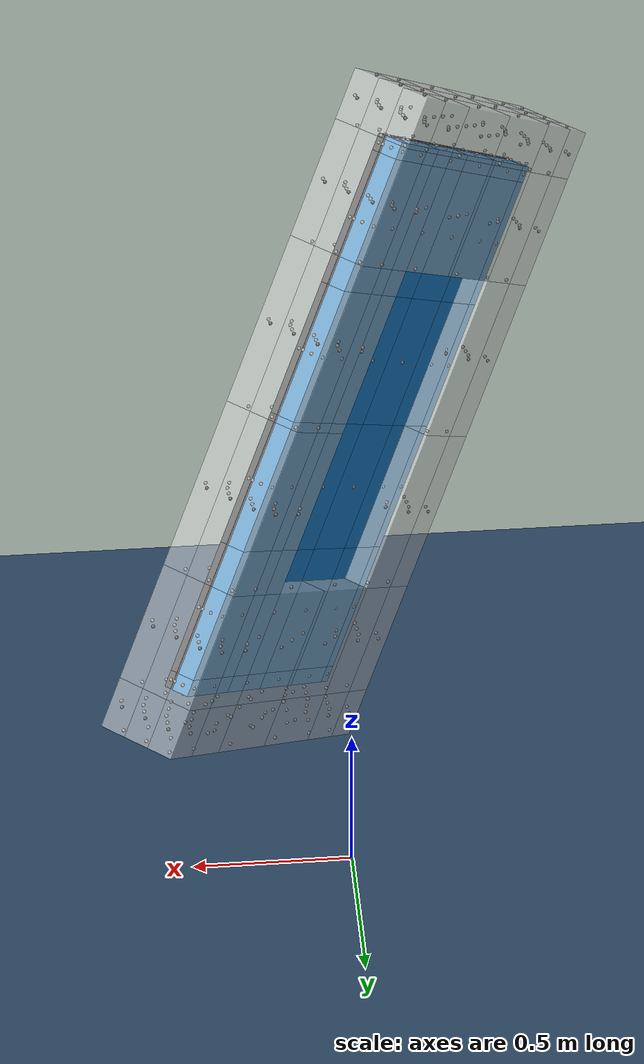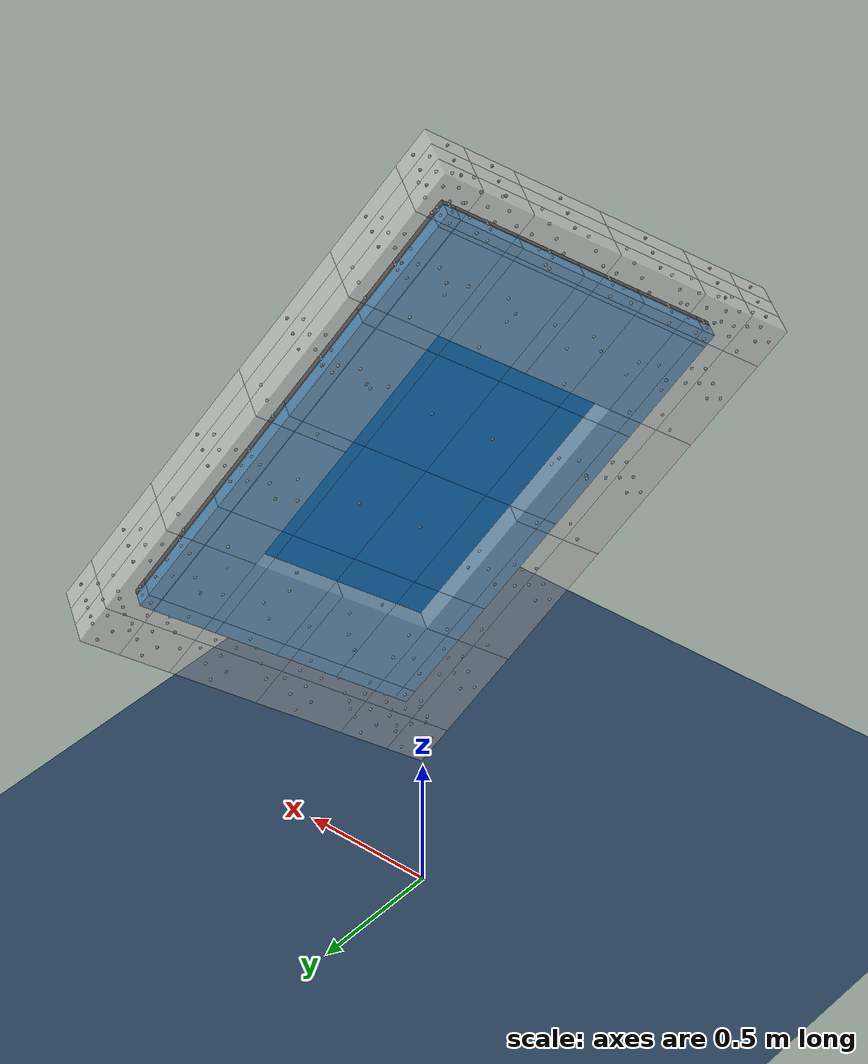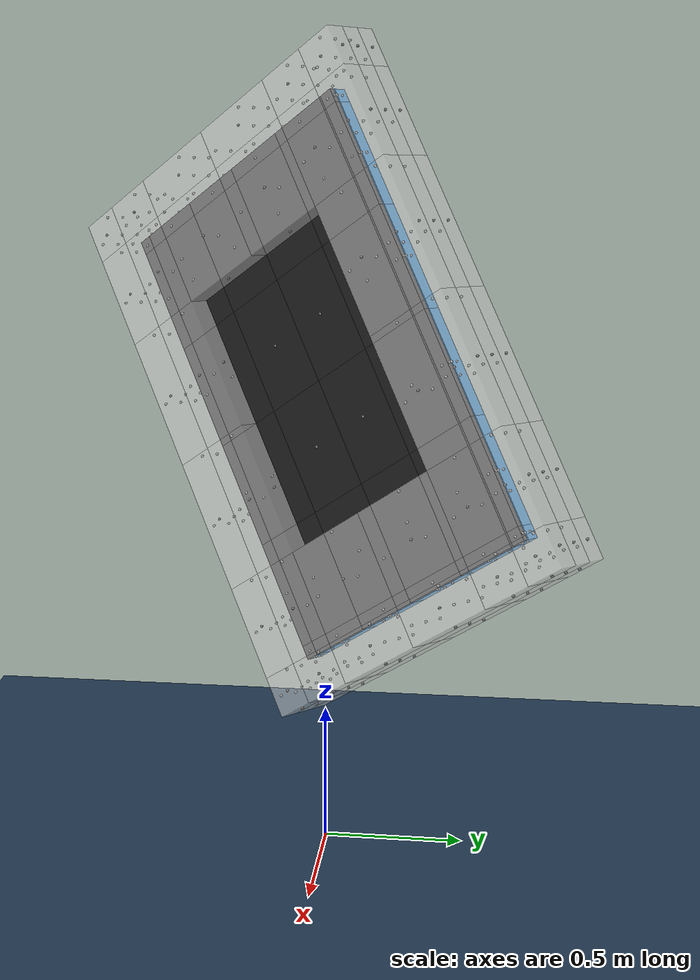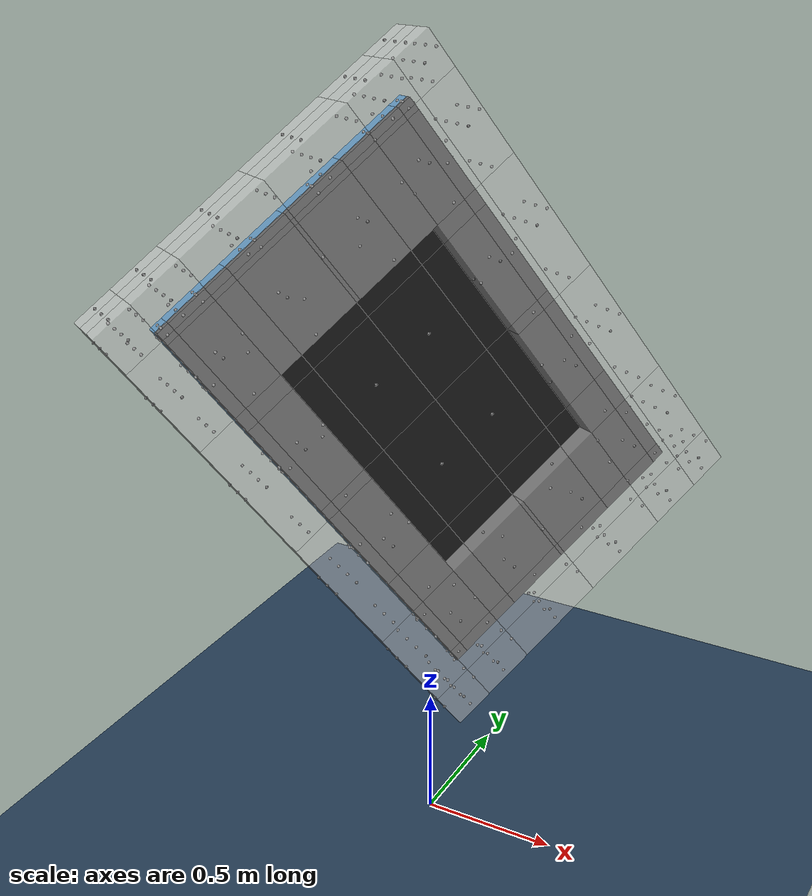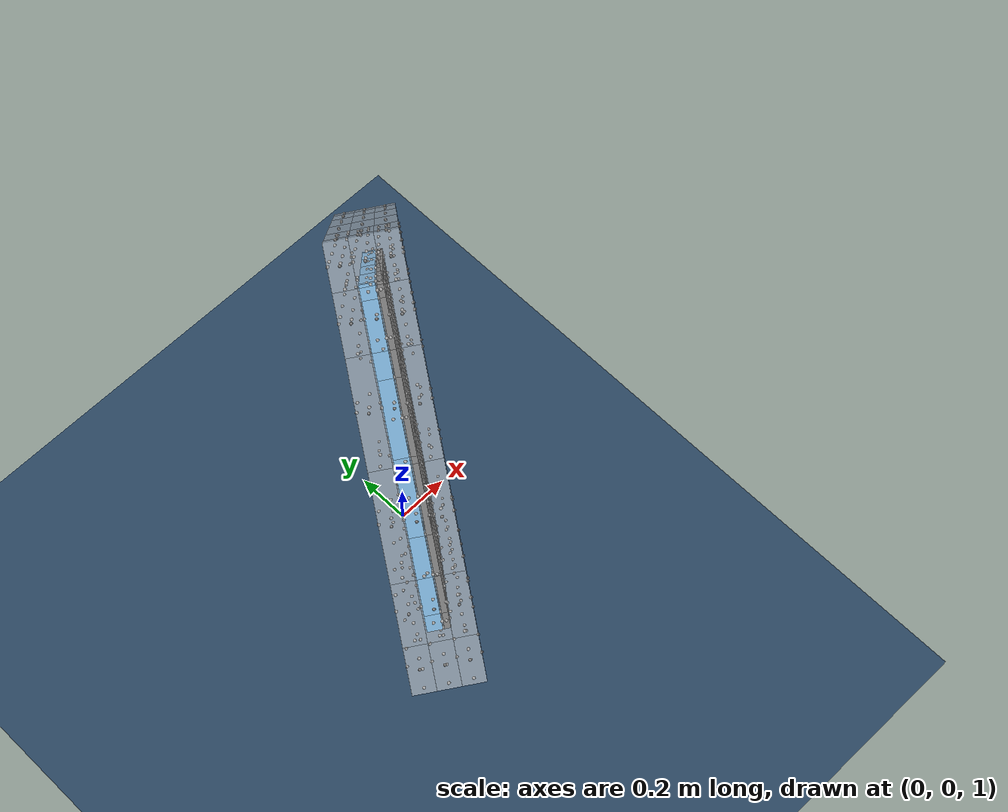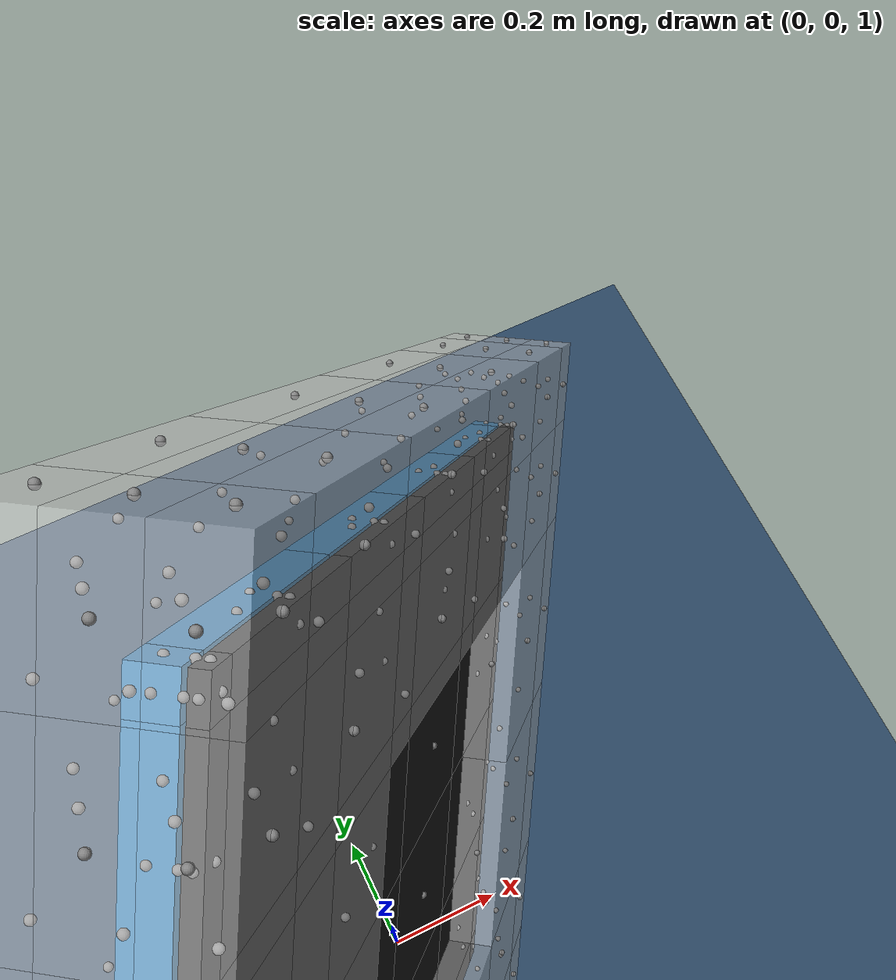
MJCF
<mujoco model="discrete_custom_box">
  <size memory="512M"/>
  <option integrator="Euler" timestep="0.0013" iterations="50" noslip_iterations="0" tolerance="1e-05" impratio="5.0" gravity="0 0 -9.81" density="1.225" viscosity="1.81e-05">
    <flag contact="enable"/>
  </option>
  <visual>
    <quality shadowsize="0"/>
    <global offwidth="0" offheight="0"/>
    <headlight ambient="0.28 0.28 0.28" diffuse="0.56 0.56 0.56" specular="0.07 0.07 0.07"/>
    <map znear="0.01"/>
  </visual>

  <asset>
    <texture type="2d" name="ground_tex" builtin="checker" mark="edge" rgb1="0.2 0.3 0.4" rgb2="0.1 0.2 0.3"
             markrgb="0.8 0.8 0.8" width="300" height="300"/>
    <material name="ground_mat" texture="ground_tex" texrepeat="5 5" texuniform="true" reflectance="0.0"/>
  </asset>

  <default>
    <joint armature="0.05" damping="1.0"/>
    <geom friction="0.8" solref="0.02 1.0" solimp="0.1 0.95 0.005"/>
    <default class="weld_bpaperbox">
      <equality solref="0.01 1.0" solimp="0.1 0.95 0.005 0.5 2"/>
    </default>
    <default class="contact_bpaperbox">
      <geom solref="0.01 1.0" solimp="0.1 0.95 0.005 0.5 2" contype="1" conaffinity="30" group="0" friction="0.8" rgba="0.7 0.6 0.4 0.9"/>
    </default>
    <default class="weld_bcushion">
      <equality solref="0.009 0.6" solimp="0.1 0.95 0.005 0.5 2.0"/>
    </default>
    <default class="contact_bcushion">
      <geom solref="0.005 0.8" solimp="0.1 0.95 0.001 0.5 2" contype="2" conaffinity="29" group="1" friction="0.8" rgba="0.9 0.9 0.9 0.5"/>
    </default>
    <default class="contact_bcushion_edge">
      <geom solref="0.07 2.0" solimp="0.1 0.95 0.001 0.5 2" contype="2" conaffinity="29" group="1" friction="0.8" rgba="0.9 0.9 0.9 0.5"/>
    </default>
    <default class="weld_bopencell">
      <equality solref="0.01 0.3" solimp="0.5 0.95 0.001 0.5 2.0"/>
    </default>
    <default class="contact_bopencell">
      <geom solref="0.01 0.3" solimp="0.5 0.95 0.001 0.5 2.0" contype="4" conaffinity="3" group="2" friction="0.8" rgba="0.1 0.1 0.1 1.0"/>
    </default>
    <default class="weld_bopencellcohesive">
      <equality solref="0.01 1.0" solimp="0.1 0.99 0.001 0.5 2.0"/>
    </default>
    <default class="contact_bopencellcohesive">
      <geom solref="0.01 1.0" solimp="0.1 0.99 0.001 0.5 2.0" contype="8" conaffinity="3" group="2" friction="0.8" rgba="1.0 0.1 0.1 0.8"/>
    </default>
    <default class="weld_bchassis">
      <equality solref="0.002 0.5" solimp="0.1 0.95 0.005 0.5 2.0"/>
    </default>
    <default class="contact_bchassis">
      <geom solref="0.002 0.5" solimp="0.1 0.95 0.005 0.5 2.0" contype="16" conaffinity="3" group="2" friction="0.8" rgba="0.1 0.5 0.8 1.0"/>
    </default>
    <default class="weld_bauxboxmass">
      <equality solref="0.002 0.5" solimp="0.1 0.95 0.005 0.5 2.0"/>
    </default>
    <default class="contact_bauxboxmass">
      <geom solref="0.002 0.5" solimp="0.1 0.95 0.005 0.5 2.0" contype="0" conaffinity="0" group="3" friction="0.8" rgba="1 0 0 0.4"/>
    </default>
    <default class="weld_aux">
      <equality solref="0.002 1.0" solimp="0.9 0.999 0.001"/>
    </default>
  </default>

  <worldbody>
    <camera name="iso_view" pos="4.5 -4.5 3.5" xyaxes="1 1 0 -0.4 0.4 1" mode="fixed"/>
    <light pos="0 0 6" dir="0 0 -1" directional="false" diffuse="0.49 0.49 0.49" ambient="0.21 0.21 0.21" castshadow="false"/>
    <light pos="3 3 5" dir="-1 -1 -1" directional="false" diffuse="0.21 0.21 0.21" castshadow="false"/>
    <geom name="ground" type="plane" size="10 10 0.1" friction="0.1" contype="1" conaffinity="1" group="0" material="ground_mat" solref="0.001 0.0001" solimp="0.1 0.95 0.001 0.5 2"/>
    <body name="BPackagingBox" pos="0.00000 0.00000 1.72704" axisangle="0.5735 0.8192 0.0000 84.1531">
      <freejoint/>
      <geom type="box" size="0.001 0.001 0.001" mass="0.000021" rgba="0 0 0 0" contype="0" conaffinity="0" friction="0.8"/>
      <body name="BCushion">
        <body name="b_bcushion_0_0_0" pos="-0.91550 -0.61550 -0.07675">
          <joint type="slide" axis="1 0 0"/>
          <joint type="slide" axis="0 1 0"/>
          <joint type="slide" axis="0 0 1"/>
          <joint type="ball"/>
          <geom name="g_bcushion_0_0_0" type="box" size="0.07450 0.07450 0.03825" mass="0.008850" class="contact_bcushion_edge"/>
          <site name="s_BCushion_0_0_0_PX" pos="0.07450 0 0"/>
          <site name="s_BCushion_0_0_0_NX" pos="-0.07450 0 0"/>
          <site name="s_BCushion_0_0_0_PY" pos="0 0.07450 0"/>
          <site name="s_BCushion_0_0_0_NY" pos="0 -0.07450 0"/>
          <site name="s_BCushion_0_0_0_PZ" pos="0 0 0.03825"/>
          <site name="s_BCushion_0_0_0_NZ" pos="0 0 -0.03825"/>
        </body>
        <body name="b_bcushion_0_0_1" pos="-0.91550 -0.61550 0.00000">
          <joint type="slide" axis="1 0 0"/>
          <joint type="slide" axis="0 1 0"/>
          <joint type="slide" axis="0 0 1"/>
          <joint type="ball"/>
          <geom name="g_bcushion_0_0_1" type="box" size="0.07450 0.07450 0.03850" mass="0.008908" class="contact_bcushion_edge"/>
          <site name="s_BCushion_0_0_1_PX" pos="0.07450 0 0"/>
          <site name="s_BCushion_0_0_1_NX" pos="-0.07450 0 0"/>
          <site name="s_BCushion_0_0_1_PY" pos="0 0.07450 0"/>
          <site name="s_BCushion_0_0_1_NY" pos="0 -0.07450 0"/>
          <site name="s_BCushion_0_0_1_PZ" pos="0 0 0.03850"/>
          <site name="s_BCushion_0_0_1_NZ" pos="0 0 -0.03850"/>
        </body>
        <body name="b_bcushion_0_0_2" pos="-0.91550 -0.61550 0.07675">
          <joint type="slide" axis="1 0 0"/>
          <joint type="slide" axis="0 1 0"/>
          <joint type="slide" axis="0 0 1"/>
          <joint type="ball"/>
          <geom name="g_bcushion_0_0_2" type="box" size="0.07450 0.07450 0.03825" mass="0.008850" class="contact_bcushion_edge"/>
          <site name="s_BCushion_0_0_2_PX" pos="0.07450 0 0"/>
          <site name="s_BCushion_0_0_2_NX" pos="-0.07450 0 0"/>
          <site name="s_BCushion_0_0_2_PY" pos="0 0.07450 0"/>
          <site name="s_BCushion_0_0_2_NY" pos="0 -0.07450 0"/>
          <site name="s_BCushion_0_0_2_PZ" pos="0 0 0.03825"/>
          <site name="s_BCushion_0_0_2_NZ" pos="0 0 -0.03825"/>
        </body>
        <body name="b_bcushion_0_1_0" pos="-0.91550 -0.44300 -0.07675">
          <joint type="slide" axis="1 0 0"/>
          <joint type="slide" axis="0 1 0"/>
          <joint type="slide" axis="0 0 1"/>
          <joint type="ball"/>
          <geom name="g_bcushion_0_1_0" type="box" size="0.07450 0.09800 0.03825" mass="0.011642" class="contact_bcushion_edge"/>
          <site name="s_BCushion_0_1_0_PX" pos="0.07450 0 0"/>
          <site name="s_BCushion_0_1_0_NX" pos="-0.07450 0 0"/>
          <site name="s_BCushion_0_1_0_PY" pos="0 0.09800 0"/>
          <site name="s_BCushion_0_1_0_NY" pos="0 -0.09800 0"/>
          <site name="s_BCushion_0_1_0_PZ" pos="0 0 0.03825"/>
          <site name="s_BCushion_0_1_0_NZ" pos="0 0 -0.03825"/>
        </body>
        <body name="b_bcushion_0_1_1" pos="-0.91550 -0.44300 0.00000">
          <joint type="slide" axis="1 0 0"/>
          <joint type="slide" axis="0 1 0"/>
          <joint type="slide" axis="0 0 1"/>
          <joint type="ball"/>
          <geom name="g_bcushion_0_1_1" type="box" size="0.07450 0.09800 0.03850" mass="0.011718" class="contact_bcushion"/>
          <site name="s_BCushion_0_1_1_PX" pos="0.07450 0 0"/>
          <site name="s_BCushion_0_1_1_NX" pos="-0.07450 0 0"/>
          <site name="s_BCushion_0_1_1_PY" pos="0 0.09800 0"/>
          <site name="s_BCushion_0_1_1_NY" pos="0 -0.09800 0"/>
          <site name="s_BCushion_0_1_1_PZ" pos="0 0 0.03850"/>
          <site name="s_BCushion_0_1_1_NZ" pos="0 0 -0.03850"/>
        </body>
        <body name="b_bcushion_0_1_2" pos="-0.91550 -0.44300 0.07675">
          <joint type="slide" axis="1 0 0"/>
          <joint type="slide" axis="0 1 0"/>
          <joint type="slide" axis="0 0 1"/>
          <joint type="ball"/>
          <geom name="g_bcushion_0_1_2" type="box" size="0.07450 0.09800 0.03825" mass="0.011642" class="contact_bcushion_edge"/>
          <site name="s_BCushion_0_1_2_PX" pos="0.07450 0 0"/>
          <site name="s_BCushion_0_1_2_NX" pos="-0.07450 0 0"/>
          <site name="s_BCushion_0_1_2_PY" pos="0 0.09800 0"/>
          <site name="s_BCushion_0_1_2_NY" pos="0 -0.09800 0"/>
          <site name="s_BCushion_0_1_2_PZ" pos="0 0 0.03825"/>
          <site name="s_BCushion_0_1_2_NZ" pos="0 0 -0.03825"/>
        </body>
        <body name="b_bcushion_0_2_0" pos="-0.91550 -0.17250 -0.07675">
          <joint type="slide" axis="1 0 0"/>
          <joint type="slide" axis="0 1 0"/>
          <joint type="slide" axis="0 0 1"/>
          <joint type="ball"/>
          <geom name="g_bcushion_0_2_0" type="box" size="0.07450 0.17250 0.03825" mass="0.020492" class="contact_bcushion_edge"/>
          <site name="s_BCushion_0_2_0_PX" pos="0.07450 0 0"/>
          <site name="s_BCushion_0_2_0_NX" pos="-0.07450 0 0"/>
          <site name="s_BCushion_0_2_0_PY" pos="0 0.17250 0"/>
          <site name="s_BCushion_0_2_0_NY" pos="0 -0.17250 0"/>
          <site name="s_BCushion_0_2_0_PZ" pos="0 0 0.03825"/>
          <site name="s_BCushion_0_2_0_NZ" pos="0 0 -0.03825"/>
        </body>
        <body name="b_bcushion_0_2_1" pos="-0.91550 -0.17250 0.00000">
          <joint type="slide" axis="1 0 0"/>
          <joint type="slide" axis="0 1 0"/>
          <joint type="slide" axis="0 0 1"/>
          <joint type="ball"/>
          <geom name="g_bcushion_0_2_1" type="box" size="0.07450 0.17250 0.03850" mass="0.020626" class="contact_bcushion"/>
          <site name="s_BCushion_0_2_1_PX" pos="0.07450 0 0"/>
          <site name="s_BCushion_0_2_1_NX" pos="-0.07450 0 0"/>
          <site name="s_BCushion_0_2_1_PY" pos="0 0.17250 0"/>
          <site name="s_BCushion_0_2_1_NY" pos="0 -0.17250 0"/>
          <site name="s_BCushion_0_2_1_PZ" pos="0 0 0.03850"/>
          <site name="s_BCushion_0_2_1_NZ" pos="0 0 -0.03850"/>
        </body>
        <body name="b_bcushion_0_2_2" pos="-0.91550 -0.17250 0.07675">
          <joint type="slide" axis="1 0 0"/>
          <joint type="slide" axis="0 1 0"/>
          <joint type="slide" axis="0 0 1"/>
          <joint type="ball"/>
          <geom name="g_bcushion_0_2_2" type="box" size="0.07450 0.17250 0.03825" mass="0.020492" class="contact_bcushion_edge"/>
          <site name="s_BCushion_0_2_2_PX" pos="0.07450 0 0"/>
          <site name="s_BCushion_0_2_2_NX" pos="-0.07450 0 0"/>
          <site name="s_BCushion_0_2_2_PY" pos="0 0.17250 0"/>
          <site name="s_BCushion_0_2_2_NY" pos="0 -0.17250 0"/>
          <site name="s_BCushion_0_2_2_PZ" pos="0 0 0.03825"/>
          <site name="s_BCushion_0_2_2_NZ" pos="0 0 -0.03825"/>
        </body>
        <body name="b_bcushion_0_3_0" pos="-0.91550 0.17250 -0.07675">
          <joint type="slide" axis="1 0 0"/>
          <joint type="slide" axis="0 1 0"/>
          <joint type="slide" axis="0 0 1"/>
          <joint type="ball"/>
          <geom name="g_bcushion_0_3_0" type="box" size="0.07450 0.17250 0.03825" mass="0.020492" class="contact_bcushion_edge"/>
          <site name="s_BCushion_0_3_0_PX" pos="0.07450 0 0"/>
          <site name="s_BCushion_0_3_0_NX" pos="-0.07450 0 0"/>
          <site name="s_BCushion_0_3_0_PY" pos="0 0.17250 0"/>
          <site name="s_BCushion_0_3_0_NY" pos="0 -0.17250 0"/>
          <site name="s_BCushion_0_3_0_PZ" pos="0 0 0.03825"/>
          <site name="s_BCushion_0_3_0_NZ" pos="0 0 -0.03825"/>
        </body>
        <body name="b_bcushion_0_3_1" pos="-0.91550 0.17250 0.00000">
          <joint type="slide" axis="1 0 0"/>
          <joint type="slide" axis="0 1 0"/>
          <joint type="slide" axis="0 0 1"/>
          <joint type="ball"/>
          <geom name="g_bcushion_0_3_1" type="box" size="0.07450 0.17250 0.03850" mass="0.020626" class="contact_bcushion"/>
          <site name="s_BCushion_0_3_1_PX" pos="0.07450 0 0"/>
          <site name="s_BCushion_0_3_1_NX" pos="-0.07450 0 0"/>
          <site name="s_BCushion_0_3_1_PY" pos="0 0.17250 0"/>
          <site name="s_BCushion_0_3_1_NY" pos="0 -0.17250 0"/>
          <site name="s_BCushion_0_3_1_PZ" pos="0 0 0.03850"/>
          <site name="s_BCushion_0_3_1_NZ" pos="0 0 -0.03850"/>
        </body>
        <body name="b_bcushion_0_3_2" pos="-0.91550 0.17250 0.07675">
          <joint type="slide" axis="1 0 0"/>
          <joint type="slide" axis="0 1 0"/>
          <joint type="slide" axis="0 0 1"/>
          <joint type="ball"/>
          <geom name="g_bcushion_0_3_2" type="box" size="0.07450 0.17250 0.03825" mass="0.020492" class="contact_bcushion_edge"/>
          <site name="s_BCushion_0_3_2_PX" pos="0.07450 0 0"/>
          <site name="s_BCushion_0_3_2_NX" pos="-0.07450 0 0"/>
          <site name="s_BCushion_0_3_2_PY" pos="0 0.17250 0"/>
          <site name="s_BCushion_0_3_2_NY" pos="0 -0.17250 0"/>
          <site name="s_BCushion_0_3_2_PZ" pos="0 0 0.03825"/>
          <site name="s_BCushion_0_3_2_NZ" pos="0 0 -0.03825"/>
        </body>
        <body name="b_bcushion_0_4_0" pos="-0.91550 0.44300 -0.07675">
          <joint type="slide" axis="1 0 0"/>
          <joint type="slide" axis="0 1 0"/>
          <joint type="slide" axis="0 0 1"/>
          <joint type="ball"/>
          <geom name="g_bcushion_0_4_0" type="box" size="0.07450 0.09800 0.03825" mass="0.011642" class="contact_bcushion_edge"/>
          <site name="s_BCushion_0_4_0_PX" pos="0.07450 0 0"/>
          <site name="s_BCushion_0_4_0_NX" pos="-0.07450 0 0"/>
          <site name="s_BCushion_0_4_0_PY" pos="0 0.09800 0"/>
          <site name="s_BCushion_0_4_0_NY" pos="0 -0.09800 0"/>
          <site name="s_BCushion_0_4_0_PZ" pos="0 0 0.03825"/>
          <site name="s_BCushion_0_4_0_NZ" pos="0 0 -0.03825"/>
        </body>
        <body name="b_bcushion_0_4_1" pos="-0.91550 0.44300 0.00000">
          <joint type="slide" axis="1 0 0"/>
          <joint type="slide" axis="0 1 0"/>
          <joint type="slide" axis="0 0 1"/>
          <joint type="ball"/>
          <geom name="g_bcushion_0_4_1" type="box" size="0.07450 0.09800 0.03850" mass="0.011718" class="contact_bcushion"/>
          <site name="s_BCushion_0_4_1_PX" pos="0.07450 0 0"/>
          <site name="s_BCushion_0_4_1_NX" pos="-0.07450 0 0"/>
          <site name="s_BCushion_0_4_1_PY" pos="0 0.09800 0"/>
          <site name="s_BCushion_0_4_1_NY" pos="0 -0.09800 0"/>
          <site name="s_BCushion_0_4_1_PZ" pos="0 0 0.03850"/>
          <site name="s_BCushion_0_4_1_NZ" pos="0 0 -0.03850"/>
        </body>
        <body name="b_bcushion_0_4_2" pos="-0.91550 0.44300 0.07675">
          <joint type="slide" axis="1 0 0"/>
          <joint type="slide" axis="0 1 0"/>
          <joint type="slide" axis="0 0 1"/>
          <joint type="ball"/>
          <geom name="g_bcushion_0_4_2" type="box" size="0.07450 0.09800 0.03825" mass="0.011642" class="contact_bcushion_edge"/>
          <site name="s_BCushion_0_4_2_PX" pos="0.07450 0 0"/>
          <site name="s_BCushion_0_4_2_NX" pos="-0.07450 0 0"/>
          <site name="s_BCushion_0_4_2_PY" pos="0 0.09800 0"/>
          <site name="s_BCushion_0_4_2_NY" pos="0 -0.09800 0"/>
          <site name="s_BCushion_0_4_2_PZ" pos="0 0 0.03825"/>
          <site name="s_BCushion_0_4_2_NZ" pos="0 0 -0.03825"/>
        </body>
        <body name="b_bcushion_0_5_0" pos="-0.91550 0.61550 -0.07675">
          <joint type="slide" axis="1 0 0"/>
          <joint type="slide" axis="0 1 0"/>
          <joint type="slide" axis="0 0 1"/>
          <joint type="ball"/>
          <geom name="g_bcushion_0_5_0" type="box" size="0.07450 0.07450 0.03825" mass="0.008850" class="contact_bcushion_edge"/>
          <site name="s_BCushion_0_5_0_PX" pos="0.07450 0 0"/>
          <site name="s_BCushion_0_5_0_NX" pos="-0.07450 0 0"/>
          <site name="s_BCushion_0_5_0_PY" pos="0 0.07450 0"/>
          <site name="s_BCushion_0_5_0_NY" pos="0 -0.07450 0"/>
          <site name="s_BCushion_0_5_0_PZ" pos="0 0 0.03825"/>
          <site name="s_BCushion_0_5_0_NZ" pos="0 0 -0.03825"/>
        </body>
        <body name="b_bcushion_0_5_1" pos="-0.91550 0.61550 0.00000">
          <joint type="slide" axis="1 0 0"/>
          <joint type="slide" axis="0 1 0"/>
          <joint type="slide" axis="0 0 1"/>
          <joint type="ball"/>
          <geom name="g_bcushion_0_5_1" type="box" size="0.07450 0.07450 0.03850" mass="0.008908" class="contact_bcushion_edge"/>
          <site name="s_BCushion_0_5_1_PX" pos="0.07450 0 0"/>
          <site name="s_BCushion_0_5_1_NX" pos="-0.07450 0 0"/>
          <site name="s_BCushion_0_5_1_PY" pos="0 0.07450 0"/>
          <site name="s_BCushion_0_5_1_NY" pos="0 -0.07450 0"/>
          <site name="s_BCushion_0_5_1_PZ" pos="0 0 0.03850"/>
          <site name="s_BCushion_0_5_1_NZ" pos="0 0 -0.03850"/>
        </body>
        <body name="b_bcushion_0_5_2" pos="-0.91550 0.61550 0.07675">
          <joint type="slide" axis="1 0 0"/>
          <joint type="slide" axis="0 1 0"/>
          <joint type="slide" axis="0 0 1"/>
          <joint type="ball"/>
          <geom name="g_bcushion_0_5_2" type="box" size="0.07450 0.07450 0.03825" mass="0.008850" class="contact_bcushion_edge"/>
          <site name="s_BCushion_0_5_2_PX" pos="0.07450 0 0"/>
          <site name="s_BCushion_0_5_2_NX" pos="-0.07450 0 0"/>
          <site name="s_BCushion_0_5_2_PY" pos="0 0.07450 0"/>
          <site name="s_BCushion_0_5_2_NY" pos="0 -0.07450 0"/>
          <site name="s_BCushion_0_5_2_PZ" pos="0 0 0.03825"/>
          <site name="s_BCushion_0_5_2_NZ" pos="0 0 -0.03825"/>
        </body>
        <body name="b_bcushion_1_0_0" pos="-0.66800 -0.61550 -0.07675">
          <joint type="slide" axis="1 0 0"/>
          <joint type="slide" axis="0 1 0"/>
          <joint type="slide" axis="0 0 1"/>
          <joint type="ball"/>
          <geom name="g_bcushion_1_0_0" type="box" size="0.17300 0.07450 0.03825" mass="0.020552" class="contact_bcushion_edge"/>
          <site name="s_BCushion_1_0_0_PX" pos="0.17300 0 0"/>
          <site name="s_BCushion_1_0_0_NX" pos="-0.17300 0 0"/>
          <site name="s_BCushion_1_0_0_PY" pos="0 0.07450 0"/>
          <site name="s_BCushion_1_0_0_NY" pos="0 -0.07450 0"/>
          <site name="s_BCushion_1_0_0_PZ" pos="0 0 0.03825"/>
          <site name="s_BCushion_1_0_0_NZ" pos="0 0 -0.03825"/>
        </body>
        <body name="b_bcushion_1_0_1" pos="-0.66800 -0.61550 0.00000">
          <joint type="slide" axis="1 0 0"/>
          <joint type="slide" axis="0 1 0"/>
          <joint type="slide" axis="0 0 1"/>
          <joint type="ball"/>
          <geom name="g_bcushion_1_0_1" type="box" size="0.17300 0.07450 0.03850" mass="0.020686" class="contact_bcushion"/>
          <site name="s_BCushion_1_0_1_PX" pos="0.17300 0 0"/>
          <site name="s_BCushion_1_0_1_NX" pos="-0.17300 0 0"/>
          <site name="s_BCushion_1_0_1_PY" pos="0 0.07450 0"/>
          <site name="s_BCushion_1_0_1_NY" pos="0 -0.07450 0"/>
          <site name="s_BCushion_1_0_1_PZ" pos="0 0 0.03850"/>
          <site name="s_BCushion_1_0_1_NZ" pos="0 0 -0.03850"/>
        </body>
        <body name="b_bcushion_1_0_2" pos="-0.66800 -0.61550 0.07675">
          <joint type="slide" axis="1 0 0"/>
          <joint type="slide" axis="0 1 0"/>
          <joint type="slide" axis="0 0 1"/>
          <joint type="ball"/>
          <geom name="g_bcushion_1_0_2" type="box" size="0.17300 0.07450 0.03825" mass="0.020552" class="contact_bcushion_edge"/>
          <site name="s_BCushion_1_0_2_PX" pos="0.17300 0 0"/>
          <site name="s_BCushion_1_0_2_NX" pos="-0.17300 0 0"/>
          <site name="s_BCushion_1_0_2_PY" pos="0 0.07450 0"/>
          <site name="s_BCushion_1_0_2_NY" pos="0 -0.07450 0"/>
          <site name="s_BCushion_1_0_2_PZ" pos="0 0 0.03825"/>
          <site name="s_BCushion_1_0_2_NZ" pos="0 0 -0.03825"/>
        </body>
        <body name="b_bcushion_1_1_0" pos="-0.66800 -0.44300 -0.07675">
          <joint type="slide" axis="1 0 0"/>
          <joint type="slide" axis="0 1 0"/>
          <joint type="slide" axis="0 0 1"/>
          <joint type="ball"/>
          <geom name="g_bcushion_1_1_0" type="box" size="0.17300 0.09800 0.03825" mass="0.027034" class="contact_bcushion"/>
          <site name="s_BCushion_1_1_0_PX" pos="0.17300 0 0"/>
          <site name="s_BCushion_1_1_0_NX" pos="-0.17300 0 0"/>
          <site name="s_BCushion_1_1_0_PY" pos="0 0.09800 0"/>
          <site name="s_BCushion_1_1_0_NY" pos="0 -0.09800 0"/>
          <site name="s_BCushion_1_1_0_PZ" pos="0 0 0.03825"/>
          <site name="s_BCushion_1_1_0_NZ" pos="0 0 -0.03825"/>
        </body>
        <body name="b_bcushion_1_1_2" pos="-0.66800 -0.44300 0.07675">
          <joint type="slide" axis="1 0 0"/>
          <joint type="slide" axis="0 1 0"/>
          <joint type="slide" axis="0 0 1"/>
          <joint type="ball"/>
          <geom name="g_bcushion_1_1_2" type="box" size="0.17300 0.09800 0.03825" mass="0.027034" class="contact_bcushion"/>
          <site name="s_BCushion_1_1_2_PX" pos="0.17300 0 0"/>
          <site name="s_BCushion_1_1_2_NX" pos="-0.17300 0 0"/>
          <site name="s_BCushion_1_1_2_PY" pos="0 0.09800 0"/>
          <site name="s_BCushion_1_1_2_NY" pos="0 -0.09800 0"/>
          <site name="s_BCushion_1_1_2_PZ" pos="0 0 0.03825"/>
          <site name="s_BCushion_1_1_2_NZ" pos="0 0 -0.03825"/>
        </body>
        <body name="b_bcushion_1_2_0" pos="-0.66800 -0.17250 -0.07675">
          <joint type="slide" axis="1 0 0"/>
          <joint type="slide" axis="0 1 0"/>
          <joint type="slide" axis="0 0 1"/>
          <joint type="ball"/>
          <geom name="g_bcushion_1_2_0" type="box" size="0.17300 0.17250 0.03825" mass="0.047586" class="contact_bcushion"/>
          <site name="s_BCushion_1_2_0_PX" pos="0.17300 0 0"/>
          <site name="s_BCushion_1_2_0_NX" pos="-0.17300 0 0"/>
          <site name="s_BCushion_1_2_0_PY" pos="0 0.17250 0"/>
          <site name="s_BCushion_1_2_0_NY" pos="0 -0.17250 0"/>
          <site name="s_BCushion_1_2_0_PZ" pos="0 0 0.03825"/>
          <site name="s_BCushion_1_2_0_NZ" pos="0 0 -0.03825"/>
        </body>
        <body name="b_bcushion_1_2_2" pos="-0.66800 -0.17250 0.07675">
          <joint type="slide" axis="1 0 0"/>
          <joint type="slide" axis="0 1 0"/>
          <joint type="slide" axis="0 0 1"/>
          <joint type="ball"/>
          <geom name="g_bcushion_1_2_2" type="box" size="0.17300 0.17250 0.03825" mass="0.047586" class="contact_bcushion"/>
          <site name="s_BCushion_1_2_2_PX" pos="0.17300 0 0"/>
          <site name="s_BCushion_1_2_2_NX" pos="-0.17300 0 0"/>
          <site name="s_BCushion_1_2_2_PY" pos="0 0.17250 0"/>
          <site name="s_BCushion_1_2_2_NY" pos="0 -0.17250 0"/>
          <site name="s_BCushion_1_2_2_PZ" pos="0 0 0.03825"/>
          <site name="s_BCushion_1_2_2_NZ" pos="0 0 -0.03825"/>
        </body>
        <body name="b_bcushion_1_3_0" pos="-0.66800 0.17250 -0.07675">
          <joint type="slide" axis="1 0 0"/>
          <joint type="slide" axis="0 1 0"/>
          <joint type="slide" axis="0 0 1"/>
          <joint type="ball"/>
          <geom name="g_bcushion_1_3_0" type="box" size="0.17300 0.17250 0.03825" mass="0.047586" class="contact_bcushion"/>
          <site name="s_BCushion_1_3_0_PX" pos="0.17300 0 0"/>
          <site name="s_BCushion_1_3_0_NX" pos="-0.17300 0 0"/>
          <site name="s_BCushion_1_3_0_PY" pos="0 0.17250 0"/>
          <site name="s_BCushion_1_3_0_NY" pos="0 -0.17250 0"/>
          <site name="s_BCushion_1_3_0_PZ" pos="0 0 0.03825"/>
          <site name="s_BCushion_1_3_0_NZ" pos="0 0 -0.03825"/>
        </body>
        <body name="b_bcushion_1_3_2" pos="-0.66800 0.17250 0.07675">
          <joint type="slide" axis="1 0 0"/>
          <joint type="slide" axis="0 1 0"/>
          <joint type="slide" axis="0 0 1"/>
          <joint type="ball"/>
          <geom name="g_bcushion_1_3_2" type="box" size="0.17300 0.17250 0.03825" mass="0.047586" class="contact_bcushion"/>
          <site name="s_BCushion_1_3_2_PX" pos="0.17300 0 0"/>
          <site name="s_BCushion_1_3_2_NX" pos="-0.17300 0 0"/>
          <site name="s_BCushion_1_3_2_PY" pos="0 0.17250 0"/>
          <site name="s_BCushion_1_3_2_NY" pos="0 -0.17250 0"/>
          <site name="s_BCushion_1_3_2_PZ" pos="0 0 0.03825"/>
          <site name="s_BCushion_1_3_2_NZ" pos="0 0 -0.03825"/>
        </body>
        <body name="b_bcushion_1_4_0" pos="-0.66800 0.44300 -0.07675">
          <joint type="slide" axis="1 0 0"/>
          <joint type="slide" axis="0 1 0"/>
          <joint type="slide" axis="0 0 1"/>
          <joint type="ball"/>
          <geom name="g_bcushion_1_4_0" type="box" size="0.17300 0.09800 0.03825" mass="0.027034" class="contact_bcushion"/>
          <site name="s_BCushion_1_4_0_PX" pos="0.17300 0 0"/>
          <site name="s_BCushion_1_4_0_NX" pos="-0.17300 0 0"/>
          <site name="s_BCushion_1_4_0_PY" pos="0 0.09800 0"/>
          <site name="s_BCushion_1_4_0_NY" pos="0 -0.09800 0"/>
          <site name="s_BCushion_1_4_0_PZ" pos="0 0 0.03825"/>
          <site name="s_BCushion_1_4_0_NZ" pos="0 0 -0.03825"/>
        </body>
        <body name="b_bcushion_1_4_2" pos="-0.66800 0.44300 0.07675">
          <joint type="slide" axis="1 0 0"/>
          <joint type="slide" axis="0 1 0"/>
          <joint type="slide" axis="0 0 1"/>
          <joint type="ball"/>
          <geom name="g_bcushion_1_4_2" type="box" size="0.17300 0.09800 0.03825" mass="0.027034" class="contact_bcushion"/>
          <site name="s_BCushion_1_4_2_PX" pos="0.17300 0 0"/>
          <site name="s_BCushion_1_4_2_NX" pos="-0.17300 0 0"/>
          <site name="s_BCushion_1_4_2_PY" pos="0 0.09800 0"/>
          <site name="s_BCushion_1_4_2_NY" pos="0 -0.09800 0"/>
          <site name="s_BCushion_1_4_2_PZ" pos="0 0 0.03825"/>
          <site name="s_BCushion_1_4_2_NZ" pos="0 0 -0.03825"/>
        </body>
        <body name="b_bcushion_1_5_0" pos="-0.66800 0.61550 -0.07675">
          <joint type="slide" axis="1 0 0"/>
          <joint type="slide" axis="0 1 0"/>
          <joint type="slide" axis="0 0 1"/>
          <joint type="ball"/>
          <geom name="g_bcushion_1_5_0" type="box" size="0.17300 0.07450 0.03825" mass="0.020552" class="contact_bcushion_edge"/>
          <site name="s_BCushion_1_5_0_PX" pos="0.17300 0 0"/>
          <site name="s_BCushion_1_5_0_NX" pos="-0.17300 0 0"/>
          <site name="s_BCushion_1_5_0_PY" pos="0 0.07450 0"/>
          <site name="s_BCushion_1_5_0_NY" pos="0 -0.07450 0"/>
          <site name="s_BCushion_1_5_0_PZ" pos="0 0 0.03825"/>
          <site name="s_BCushion_1_5_0_NZ" pos="0 0 -0.03825"/>
        </body>
        <body name="b_bcushion_1_5_1" pos="-0.66800 0.61550 0.00000">
          <joint type="slide" axis="1 0 0"/>
          <joint type="slide" axis="0 1 0"/>
          <joint type="slide" axis="0 0 1"/>
          <joint type="ball"/>
          <geom name="g_bcushion_1_5_1" type="box" size="0.17300 0.07450 0.03850" mass="0.020686" class="contact_bcushion"/>
          <site name="s_BCushion_1_5_1_PX" pos="0.17300 0 0"/>
          <site name="s_BCushion_1_5_1_NX" pos="-0.17300 0 0"/>
          <site name="s_BCushion_1_5_1_PY" pos="0 0.07450 0"/>
          <site name="s_BCushion_1_5_1_NY" pos="0 -0.07450 0"/>
          <site name="s_BCushion_1_5_1_PZ" pos="0 0 0.03850"/>
          <site name="s_BCushion_1_5_1_NZ" pos="0 0 -0.03850"/>
        </body>
        <body name="b_bcushion_1_5_2" pos="-0.66800 0.61550 0.07675">
          <joint type="slide" axis="1 0 0"/>
          <joint type="slide" axis="0 1 0"/>
          <joint type="slide" axis="0 0 1"/>
          <joint type="ball"/>
          <geom name="g_bcushion_1_5_2" type="box" size="0.17300 0.07450 0.03825" mass="0.020552" class="contact_bcushion_edge"/>
          <site name="s_BCushion_1_5_2_PX" pos="0.17300 0 0"/>
          <site name="s_BCushion_1_5_2_NX" pos="-0.17300 0 0"/>
          <site name="s_BCushion_1_5_2_PY" pos="0 0.07450 0"/>
          <site name="s_BCushion_1_5_2_NY" pos="0 -0.07450 0"/>
          <site name="s_BCushion_1_5_2_PZ" pos="0 0 0.03825"/>
          <site name="s_BCushion_1_5_2_NZ" pos="0 0 -0.03825"/>
        </body>
        <body name="b_bcushion_2_0_0" pos="-0.24750 -0.61550 -0.07675">
          <joint type="slide" axis="1 0 0"/>
          <joint type="slide" axis="0 1 0"/>
          <joint type="slide" axis="0 0 1"/>
          <joint type="ball"/>
          <geom name="g_bcushion_2_0_0" type="box" size="0.24750 0.07450 0.03825" mass="0.029402" class="contact_bcushion_edge"/>
          <site name="s_BCushion_2_0_0_PX" pos="0.24750 0 0"/>
          <site name="s_BCushion_2_0_0_NX" pos="-0.24750 0 0"/>
          <site name="s_BCushion_2_0_0_PY" pos="0 0.07450 0"/>
          <site name="s_BCushion_2_0_0_NY" pos="0 -0.07450 0"/>
          <site name="s_BCushion_2_0_0_PZ" pos="0 0 0.03825"/>
          <site name="s_BCushion_2_0_0_NZ" pos="0 0 -0.03825"/>
        </body>
        <body name="b_bcushion_2_0_1" pos="-0.24750 -0.61550 0.00000">
          <joint type="slide" axis="1 0 0"/>
          <joint type="slide" axis="0 1 0"/>
          <joint type="slide" axis="0 0 1"/>
          <joint type="ball"/>
          <geom name="g_bcushion_2_0_1" type="box" size="0.24750 0.07450 0.03850" mass="0.029594" class="contact_bcushion"/>
          <site name="s_BCushion_2_0_1_PX" pos="0.24750 0 0"/>
          <site name="s_BCushion_2_0_1_NX" pos="-0.24750 0 0"/>
          <site name="s_BCushion_2_0_1_PY" pos="0 0.07450 0"/>
          <site name="s_BCushion_2_0_1_NY" pos="0 -0.07450 0"/>
          <site name="s_BCushion_2_0_1_PZ" pos="0 0 0.03850"/>
          <site name="s_BCushion_2_0_1_NZ" pos="0 0 -0.03850"/>
        </body>
        <body name="b_bcushion_2_0_2" pos="-0.24750 -0.61550 0.07675">
          <joint type="slide" axis="1 0 0"/>
          <joint type="slide" axis="0 1 0"/>
          <joint type="slide" axis="0 0 1"/>
          <joint type="ball"/>
          <geom name="g_bcushion_2_0_2" type="box" size="0.24750 0.07450 0.03825" mass="0.029402" class="contact_bcushion_edge"/>
          <site name="s_BCushion_2_0_2_PX" pos="0.24750 0 0"/>
          <site name="s_BCushion_2_0_2_NX" pos="-0.24750 0 0"/>
          <site name="s_BCushion_2_0_2_PY" pos="0 0.07450 0"/>
          <site name="s_BCushion_2_0_2_NY" pos="0 -0.07450 0"/>
          <site name="s_BCushion_2_0_2_PZ" pos="0 0 0.03825"/>
          <site name="s_BCushion_2_0_2_NZ" pos="0 0 -0.03825"/>
        </body>
        <body name="b_bcushion_2_1_0" pos="-0.24750 -0.44300 -0.07675">
          <joint type="slide" axis="1 0 0"/>
          <joint type="slide" axis="0 1 0"/>
          <joint type="slide" axis="0 0 1"/>
          <joint type="ball"/>
          <geom name="g_bcushion_2_1_0" type="box" size="0.24750 0.09800 0.03825" mass="0.038676" class="contact_bcushion"/>
          <site name="s_BCushion_2_1_0_PX" pos="0.24750 0 0"/>
          <site name="s_BCushion_2_1_0_NX" pos="-0.24750 0 0"/>
          <site name="s_BCushion_2_1_0_PY" pos="0 0.09800 0"/>
          <site name="s_BCushion_2_1_0_NY" pos="0 -0.09800 0"/>
          <site name="s_BCushion_2_1_0_PZ" pos="0 0 0.03825"/>
          <site name="s_BCushion_2_1_0_NZ" pos="0 0 -0.03825"/>
        </body>
        <body name="b_bcushion_2_1_2" pos="-0.24750 -0.44300 0.07675">
          <joint type="slide" axis="1 0 0"/>
          <joint type="slide" axis="0 1 0"/>
          <joint type="slide" axis="0 0 1"/>
          <joint type="ball"/>
          <geom name="g_bcushion_2_1_2" type="box" size="0.24750 0.09800 0.03825" mass="0.038676" class="contact_bcushion"/>
          <site name="s_BCushion_2_1_2_PX" pos="0.24750 0 0"/>
          <site name="s_BCushion_2_1_2_NX" pos="-0.24750 0 0"/>
          <site name="s_BCushion_2_1_2_PY" pos="0 0.09800 0"/>
          <site name="s_BCushion_2_1_2_NY" pos="0 -0.09800 0"/>
          <site name="s_BCushion_2_1_2_PZ" pos="0 0 0.03825"/>
          <site name="s_BCushion_2_1_2_NZ" pos="0 0 -0.03825"/>
        </body>
        <body name="b_bcushion_2_4_0" pos="-0.24750 0.44300 -0.07675">
          <joint type="slide" axis="1 0 0"/>
          <joint type="slide" axis="0 1 0"/>
          <joint type="slide" axis="0 0 1"/>
          <joint type="ball"/>
          <geom name="g_bcushion_2_4_0" type="box" size="0.24750 0.09800 0.03825" mass="0.038676" class="contact_bcushion"/>
          <site name="s_BCushion_2_4_0_PX" pos="0.24750 0 0"/>
          <site name="s_BCushion_2_4_0_NX" pos="-0.24750 0 0"/>
          <site name="s_BCushion_2_4_0_PY" pos="0 0.09800 0"/>
          <site name="s_BCushion_2_4_0_NY" pos="0 -0.09800 0"/>
          <site name="s_BCushion_2_4_0_PZ" pos="0 0 0.03825"/>
          <site name="s_BCushion_2_4_0_NZ" pos="0 0 -0.03825"/>
        </body>
        <body name="b_bcushion_2_4_2" pos="-0.24750 0.44300 0.07675">
          <joint type="slide" axis="1 0 0"/>
          <joint type="slide" axis="0 1 0"/>
          <joint type="slide" axis="0 0 1"/>
          <joint type="ball"/>
          <geom name="g_bcushion_2_4_2" type="box" size="0.24750 0.09800 0.03825" mass="0.038676" class="contact_bcushion"/>
          <site name="s_BCushion_2_4_2_PX" pos="0.24750 0 0"/>
          <site name="s_BCushion_2_4_2_NX" pos="-0.24750 0 0"/>
          <site name="s_BCushion_2_4_2_PY" pos="0 0.09800 0"/>
          <site name="s_BCushion_2_4_2_NY" pos="0 -0.09800 0"/>
          <site name="s_BCushion_2_4_2_PZ" pos="0 0 0.03825"/>
          <site name="s_BCushion_2_4_2_NZ" pos="0 0 -0.03825"/>
        </body>
        <body name="b_bcushion_2_5_0" pos="-0.24750 0.61550 -0.07675">
          <joint type="slide" axis="1 0 0"/>
          <joint type="slide" axis="0 1 0"/>
          <joint type="slide" axis="0 0 1"/>
          <joint type="ball"/>
          <geom name="g_bcushion_2_5_0" type="box" size="0.24750 0.07450 0.03825" mass="0.029402" class="contact_bcushion_edge"/>
          <site name="s_BCushion_2_5_0_PX" pos="0.24750 0 0"/>
          <site name="s_BCushion_2_5_0_NX" pos="-0.24750 0 0"/>
          <site name="s_BCushion_2_5_0_PY" pos="0 0.07450 0"/>
          <site name="s_BCushion_2_5_0_NY" pos="0 -0.07450 0"/>
          <site name="s_BCushion_2_5_0_PZ" pos="0 0 0.03825"/>
          <site name="s_BCushion_2_5_0_NZ" pos="0 0 -0.03825"/>
        </body>
        <body name="b_bcushion_2_5_1" pos="-0.24750 0.61550 0.00000">
          <joint type="slide" axis="1 0 0"/>
          <joint type="slide" axis="0 1 0"/>
          <joint type="slide" axis="0 0 1"/>
          <joint type="ball"/>
          <geom name="g_bcushion_2_5_1" type="box" size="0.24750 0.07450 0.03850" mass="0.029594" class="contact_bcushion"/>
          <site name="s_BCushion_2_5_1_PX" pos="0.24750 0 0"/>
          <site name="s_BCushion_2_5_1_NX" pos="-0.24750 0 0"/>
          <site name="s_BCushion_2_5_1_PY" pos="0 0.07450 0"/>
          <site name="s_BCushion_2_5_1_NY" pos="0 -0.07450 0"/>
          <site name="s_BCushion_2_5_1_PZ" pos="0 0 0.03850"/>
          <site name="s_BCushion_2_5_1_NZ" pos="0 0 -0.03850"/>
        </body>
        <body name="b_bcushion_2_5_2" pos="-0.24750 0.61550 0.07675">
          <joint type="slide" axis="1 0 0"/>
          <joint type="slide" axis="0 1 0"/>
          <joint type="slide" axis="0 0 1"/>
          <joint type="ball"/>
          <geom name="g_bcushion_2_5_2" type="box" size="0.24750 0.07450 0.03825" mass="0.029402" class="contact_bcushion_edge"/>
          <site name="s_BCushion_2_5_2_PX" pos="0.24750 0 0"/>
          <site name="s_BCushion_2_5_2_NX" pos="-0.24750 0 0"/>
          <site name="s_BCushion_2_5_2_PY" pos="0 0.07450 0"/>
          <site name="s_BCushion_2_5_2_NY" pos="0 -0.07450 0"/>
          <site name="s_BCushion_2_5_2_PZ" pos="0 0 0.03825"/>
          <site name="s_BCushion_2_5_2_NZ" pos="0 0 -0.03825"/>
        </body>
        <body name="b_bcushion_3_0_0" pos="0.24750 -0.61550 -0.07675">
          <joint type="slide" axis="1 0 0"/>
          <joint type="slide" axis="0 1 0"/>
          <joint type="slide" axis="0 0 1"/>
          <joint type="ball"/>
          <geom name="g_bcushion_3_0_0" type="box" size="0.24750 0.07450 0.03825" mass="0.029402" class="contact_bcushion_edge"/>
          <site name="s_BCushion_3_0_0_PX" pos="0.24750 0 0"/>
          <site name="s_BCushion_3_0_0_NX" pos="-0.24750 0 0"/>
          <site name="s_BCushion_3_0_0_PY" pos="0 0.07450 0"/>
          <site name="s_BCushion_3_0_0_NY" pos="0 -0.07450 0"/>
          <site name="s_BCushion_3_0_0_PZ" pos="0 0 0.03825"/>
          <site name="s_BCushion_3_0_0_NZ" pos="0 0 -0.03825"/>
        </body>
        <body name="b_bcushion_3_0_1" pos="0.24750 -0.61550 0.00000">
          <joint type="slide" axis="1 0 0"/>
          <joint type="slide" axis="0 1 0"/>
          <joint type="slide" axis="0 0 1"/>
          <joint type="ball"/>
          <geom name="g_bcushion_3_0_1" type="box" size="0.24750 0.07450 0.03850" mass="0.029594" class="contact_bcushion"/>
          <site name="s_BCushion_3_0_1_PX" pos="0.24750 0 0"/>
          <site name="s_BCushion_3_0_1_NX" pos="-0.24750 0 0"/>
          <site name="s_BCushion_3_0_1_PY" pos="0 0.07450 0"/>
          <site name="s_BCushion_3_0_1_NY" pos="0 -0.07450 0"/>
          <site name="s_BCushion_3_0_1_PZ" pos="0 0 0.03850"/>
          <site name="s_BCushion_3_0_1_NZ" pos="0 0 -0.03850"/>
        </body>
        <body name="b_bcushion_3_0_2" pos="0.24750 -0.61550 0.07675">
          <joint type="slide" axis="1 0 0"/>
          <joint type="slide" axis="0 1 0"/>
          <joint type="slide" axis="0 0 1"/>
          <joint type="ball"/>
          <geom name="g_bcushion_3_0_2" type="box" size="0.24750 0.07450 0.03825" mass="0.029402" class="contact_bcushion_edge"/>
          <site name="s_BCushion_3_0_2_PX" pos="0.24750 0 0"/>
          <site name="s_BCushion_3_0_2_NX" pos="-0.24750 0 0"/>
          <site name="s_BCushion_3_0_2_PY" pos="0 0.07450 0"/>
          <site name="s_BCushion_3_0_2_NY" pos="0 -0.07450 0"/>
          <site name="s_BCushion_3_0_2_PZ" pos="0 0 0.03825"/>
          <site name="s_BCushion_3_0_2_NZ" pos="0 0 -0.03825"/>
        </body>
        <body name="b_bcushion_3_1_0" pos="0.24750 -0.44300 -0.07675">
          <joint type="slide" axis="1 0 0"/>
          <joint type="slide" axis="0 1 0"/>
          <joint type="slide" axis="0 0 1"/>
          <joint type="ball"/>
          <geom name="g_bcushion_3_1_0" type="box" size="0.24750 0.09800 0.03825" mass="0.038676" class="contact_bcushion"/>
          <site name="s_BCushion_3_1_0_PX" pos="0.24750 0 0"/>
          <site name="s_BCushion_3_1_0_NX" pos="-0.24750 0 0"/>
          <site name="s_BCushion_3_1_0_PY" pos="0 0.09800 0"/>
          <site name="s_BCushion_3_1_0_NY" pos="0 -0.09800 0"/>
          <site name="s_BCushion_3_1_0_PZ" pos="0 0 0.03825"/>
          <site name="s_BCushion_3_1_0_NZ" pos="0 0 -0.03825"/>
        </body>
        <body name="b_bcushion_3_1_2" pos="0.24750 -0.44300 0.07675">
          <joint type="slide" axis="1 0 0"/>
          <joint type="slide" axis="0 1 0"/>
          <joint type="slide" axis="0 0 1"/>
          <joint type="ball"/>
          <geom name="g_bcushion_3_1_2" type="box" size="0.24750 0.09800 0.03825" mass="0.038676" class="contact_bcushion"/>
          <site name="s_BCushion_3_1_2_PX" pos="0.24750 0 0"/>
          <site name="s_BCushion_3_1_2_NX" pos="-0.24750 0 0"/>
          <site name="s_BCushion_3_1_2_PY" pos="0 0.09800 0"/>
          <site name="s_BCushion_3_1_2_NY" pos="0 -0.09800 0"/>
          <site name="s_BCushion_3_1_2_PZ" pos="0 0 0.03825"/>
          <site name="s_BCushion_3_1_2_NZ" pos="0 0 -0.03825"/>
        </body>
        <body name="b_bcushion_3_4_0" pos="0.24750 0.44300 -0.07675">
          <joint type="slide" axis="1 0 0"/>
          <joint type="slide" axis="0 1 0"/>
          <joint type="slide" axis="0 0 1"/>
          <joint type="ball"/>
          <geom name="g_bcushion_3_4_0" type="box" size="0.24750 0.09800 0.03825" mass="0.038676" class="contact_bcushion"/>
          <site name="s_BCushion_3_4_0_PX" pos="0.24750 0 0"/>
          <site name="s_BCushion_3_4_0_NX" pos="-0.24750 0 0"/>
          <site name="s_BCushion_3_4_0_PY" pos="0 0.09800 0"/>
          <site name="s_BCushion_3_4_0_NY" pos="0 -0.09800 0"/>
          <site name="s_BCushion_3_4_0_PZ" pos="0 0 0.03825"/>
          <site name="s_BCushion_3_4_0_NZ" pos="0 0 -0.03825"/>
        </body>
        <body name="b_bcushion_3_4_2" pos="0.24750 0.44300 0.07675">
          <joint type="slide" axis="1 0 0"/>
          <joint type="slide" axis="0 1 0"/>
          <joint type="slide" axis="0 0 1"/>
          <joint type="ball"/>
          <geom name="g_bcushion_3_4_2" type="box" size="0.24750 0.09800 0.03825" mass="0.038676" class="contact_bcushion"/>
          <site name="s_BCushion_3_4_2_PX" pos="0.24750 0 0"/>
          <site name="s_BCushion_3_4_2_NX" pos="-0.24750 0 0"/>
          <site name="s_BCushion_3_4_2_PY" pos="0 0.09800 0"/>
          <site name="s_BCushion_3_4_2_NY" pos="0 -0.09800 0"/>
          <site name="s_BCushion_3_4_2_PZ" pos="0 0 0.03825"/>
          <site name="s_BCushion_3_4_2_NZ" pos="0 0 -0.03825"/>
        </body>
        <body name="b_bcushion_3_5_0" pos="0.24750 0.61550 -0.07675">
          <joint type="slide" axis="1 0 0"/>
          <joint type="slide" axis="0 1 0"/>
          <joint type="slide" axis="0 0 1"/>
          <joint type="ball"/>
          <geom name="g_bcushion_3_5_0" type="box" size="0.24750 0.07450 0.03825" mass="0.029402" class="contact_bcushion_edge"/>
          <site name="s_BCushion_3_5_0_PX" pos="0.24750 0 0"/>
          <site name="s_BCushion_3_5_0_NX" pos="-0.24750 0 0"/>
          <site name="s_BCushion_3_5_0_PY" pos="0 0.07450 0"/>
          <site name="s_BCushion_3_5_0_NY" pos="0 -0.07450 0"/>
          <site name="s_BCushion_3_5_0_PZ" pos="0 0 0.03825"/>
          <site name="s_BCushion_3_5_0_NZ" pos="0 0 -0.03825"/>
        </body>
        <body name="b_bcushion_3_5_1" pos="0.24750 0.61550 0.00000">
          <joint type="slide" axis="1 0 0"/>
          <joint type="slide" axis="0 1 0"/>
          <joint type="slide" axis="0 0 1"/>
          <joint type="ball"/>
          <geom name="g_bcushion_3_5_1" type="box" size="0.24750 0.07450 0.03850" mass="0.029594" class="contact_bcushion"/>
          <site name="s_BCushion_3_5_1_PX" pos="0.24750 0 0"/>
          <site name="s_BCushion_3_5_1_NX" pos="-0.24750 0 0"/>
          <site name="s_BCushion_3_5_1_PY" pos="0 0.07450 0"/>
          <site name="s_BCushion_3_5_1_NY" pos="0 -0.07450 0"/>
          <site name="s_BCushion_3_5_1_PZ" pos="0 0 0.03850"/>
          <site name="s_BCushion_3_5_1_NZ" pos="0 0 -0.03850"/>
        </body>
        <body name="b_bcushion_3_5_2" pos="0.24750 0.61550 0.07675">
          <joint type="slide" axis="1 0 0"/>
          <joint type="slide" axis="0 1 0"/>
          <joint type="slide" axis="0 0 1"/>
          <joint type="ball"/>
          <geom name="g_bcushion_3_5_2" type="box" size="0.24750 0.07450 0.03825" mass="0.029402" class="contact_bcushion_edge"/>
          <site name="s_BCushion_3_5_2_PX" pos="0.24750 0 0"/>
          <site name="s_BCushion_3_5_2_NX" pos="-0.24750 0 0"/>
          <site name="s_BCushion_3_5_2_PY" pos="0 0.07450 0"/>
          <site name="s_BCushion_3_5_2_NY" pos="0 -0.07450 0"/>
          <site name="s_BCushion_3_5_2_PZ" pos="0 0 0.03825"/>
          <site name="s_BCushion_3_5_2_NZ" pos="0 0 -0.03825"/>
        </body>
        <body name="b_bcushion_4_0_0" pos="0.66800 -0.61550 -0.07675">
          <joint type="slide" axis="1 0 0"/>
          <joint type="slide" axis="0 1 0"/>
          <joint type="slide" axis="0 0 1"/>
          <joint type="ball"/>
          <geom name="g_bcushion_4_0_0" type="box" size="0.17300 0.07450 0.03825" mass="0.020552" class="contact_bcushion_edge"/>
          <site name="s_BCushion_4_0_0_PX" pos="0.17300 0 0"/>
          <site name="s_BCushion_4_0_0_NX" pos="-0.17300 0 0"/>
          <site name="s_BCushion_4_0_0_PY" pos="0 0.07450 0"/>
          <site name="s_BCushion_4_0_0_NY" pos="0 -0.07450 0"/>
          <site name="s_BCushion_4_0_0_PZ" pos="0 0 0.03825"/>
          <site name="s_BCushion_4_0_0_NZ" pos="0 0 -0.03825"/>
        </body>
        <body name="b_bcushion_4_0_1" pos="0.66800 -0.61550 0.00000">
          <joint type="slide" axis="1 0 0"/>
          <joint type="slide" axis="0 1 0"/>
          <joint type="slide" axis="0 0 1"/>
          <joint type="ball"/>
          <geom name="g_bcushion_4_0_1" type="box" size="0.17300 0.07450 0.03850" mass="0.020686" class="contact_bcushion"/>
          <site name="s_BCushion_4_0_1_PX" pos="0.17300 0 0"/>
          <site name="s_BCushion_4_0_1_NX" pos="-0.17300 0 0"/>
          <site name="s_BCushion_4_0_1_PY" pos="0 0.07450 0"/>
          <site name="s_BCushion_4_0_1_NY" pos="0 -0.07450 0"/>
          <site name="s_BCushion_4_0_1_PZ" pos="0 0 0.03850"/>
          <site name="s_BCushion_4_0_1_NZ" pos="0 0 -0.03850"/>
        </body>
        <body name="b_bcushion_4_0_2" pos="0.66800 -0.61550 0.07675">
          <joint type="slide" axis="1 0 0"/>
          <joint type="slide" axis="0 1 0"/>
          <joint type="slide" axis="0 0 1"/>
          <joint type="ball"/>
          <geom name="g_bcushion_4_0_2" type="box" size="0.17300 0.07450 0.03825" mass="0.020552" class="contact_bcushion_edge"/>
          <site name="s_BCushion_4_0_2_PX" pos="0.17300 0 0"/>
          <site name="s_BCushion_4_0_2_NX" pos="-0.17300 0 0"/>
          <site name="s_BCushion_4_0_2_PY" pos="0 0.07450 0"/>
          <site name="s_BCushion_4_0_2_NY" pos="0 -0.07450 0"/>
          <site name="s_BCushion_4_0_2_PZ" pos="0 0 0.03825"/>
          <site name="s_BCushion_4_0_2_NZ" pos="0 0 -0.03825"/>
        </body>
        <body name="b_bcushion_4_1_0" pos="0.66800 -0.44300 -0.07675">
          <joint type="slide" axis="1 0 0"/>
          <joint type="slide" axis="0 1 0"/>
          <joint type="slide" axis="0 0 1"/>
          <joint type="ball"/>
          <geom name="g_bcushion_4_1_0" type="box" size="0.17300 0.09800 0.03825" mass="0.027034" class="contact_bcushion"/>
          <site name="s_BCushion_4_1_0_PX" pos="0.17300 0 0"/>
          <site name="s_BCushion_4_1_0_NX" pos="-0.17300 0 0"/>
          <site name="s_BCushion_4_1_0_PY" pos="0 0.09800 0"/>
          <site name="s_BCushion_4_1_0_NY" pos="0 -0.09800 0"/>
          <site name="s_BCushion_4_1_0_PZ" pos="0 0 0.03825"/>
          <site name="s_BCushion_4_1_0_NZ" pos="0 0 -0.03825"/>
        </body>
        <body name="b_bcushion_4_1_2" pos="0.66800 -0.44300 0.07675">
          <joint type="slide" axis="1 0 0"/>
          <joint type="slide" axis="0 1 0"/>
          <joint type="slide" axis="0 0 1"/>
          <joint type="ball"/>
          <geom name="g_bcushion_4_1_2" type="box" size="0.17300 0.09800 0.03825" mass="0.027034" class="contact_bcushion"/>
          <site name="s_BCushion_4_1_2_PX" pos="0.17300 0 0"/>
          <site name="s_BCushion_4_1_2_NX" pos="-0.17300 0 0"/>
          <site name="s_BCushion_4_1_2_PY" pos="0 0.09800 0"/>
          <site name="s_BCushion_4_1_2_NY" pos="0 -0.09800 0"/>
          <site name="s_BCushion_4_1_2_PZ" pos="0 0 0.03825"/>
          <site name="s_BCushion_4_1_2_NZ" pos="0 0 -0.03825"/>
        </body>
        <body name="b_bcushion_4_2_0" pos="0.66800 -0.17250 -0.07675">
          <joint type="slide" axis="1 0 0"/>
          <joint type="slide" axis="0 1 0"/>
          <joint type="slide" axis="0 0 1"/>
          <joint type="ball"/>
          <geom name="g_bcushion_4_2_0" type="box" size="0.17300 0.17250 0.03825" mass="0.047586" class="contact_bcushion"/>
          <site name="s_BCushion_4_2_0_PX" pos="0.17300 0 0"/>
          <site name="s_BCushion_4_2_0_NX" pos="-0.17300 0 0"/>
          <site name="s_BCushion_4_2_0_PY" pos="0 0.17250 0"/>
          <site name="s_BCushion_4_2_0_NY" pos="0 -0.17250 0"/>
          <site name="s_BCushion_4_2_0_PZ" pos="0 0 0.03825"/>
          <site name="s_BCushion_4_2_0_NZ" pos="0 0 -0.03825"/>
        </body>
        <body name="b_bcushion_4_2_2" pos="0.66800 -0.17250 0.07675">
          <joint type="slide" axis="1 0 0"/>
          <joint type="slide" axis="0 1 0"/>
          <joint type="slide" axis="0 0 1"/>
          <joint type="ball"/>
          <geom name="g_bcushion_4_2_2" type="box" size="0.17300 0.17250 0.03825" mass="0.047586" class="contact_bcushion"/>
          <site name="s_BCushion_4_2_2_PX" pos="0.17300 0 0"/>
          <site name="s_BCushion_4_2_2_NX" pos="-0.17300 0 0"/>
          <site name="s_BCushion_4_2_2_PY" pos="0 0.17250 0"/>
          <site name="s_BCushion_4_2_2_NY" pos="0 -0.17250 0"/>
          <site name="s_BCushion_4_2_2_PZ" pos="0 0 0.03825"/>
          <site name="s_BCushion_4_2_2_NZ" pos="0 0 -0.03825"/>
        </body>
        <body name="b_bcushion_4_3_0" pos="0.66800 0.17250 -0.07675">
          <joint type="slide" axis="1 0 0"/>
          <joint type="slide" axis="0 1 0"/>
          <joint type="slide" axis="0 0 1"/>
          <joint type="ball"/>
          <geom name="g_bcushion_4_3_0" type="box" size="0.17300 0.17250 0.03825" mass="0.047586" class="contact_bcushion"/>
          <site name="s_BCushion_4_3_0_PX" pos="0.17300 0 0"/>
          <site name="s_BCushion_4_3_0_NX" pos="-0.17300 0 0"/>
          <site name="s_BCushion_4_3_0_PY" pos="0 0.17250 0"/>
          <site name="s_BCushion_4_3_0_NY" pos="0 -0.17250 0"/>
          <site name="s_BCushion_4_3_0_PZ" pos="0 0 0.03825"/>
          <site name="s_BCushion_4_3_0_NZ" pos="0 0 -0.03825"/>
        </body>
        <body name="b_bcushion_4_3_2" pos="0.66800 0.17250 0.07675">
          <joint type="slide" axis="1 0 0"/>
          <joint type="slide" axis="0 1 0"/>
          <joint type="slide" axis="0 0 1"/>
          <joint type="ball"/>
          <geom name="g_bcushion_4_3_2" type="box" size="0.17300 0.17250 0.03825" mass="0.047586" class="contact_bcushion"/>
          <site name="s_BCushion_4_3_2_PX" pos="0.17300 0 0"/>
          <site name="s_BCushion_4_3_2_NX" pos="-0.17300 0 0"/>
          <site name="s_BCushion_4_3_2_PY" pos="0 0.17250 0"/>
          <site name="s_BCushion_4_3_2_NY" pos="0 -0.17250 0"/>
          <site name="s_BCushion_4_3_2_PZ" pos="0 0 0.03825"/>
          <site name="s_BCushion_4_3_2_NZ" pos="0 0 -0.03825"/>
        </body>
        <body name="b_bcushion_4_4_0" pos="0.66800 0.44300 -0.07675">
          <joint type="slide" axis="1 0 0"/>
          <joint type="slide" axis="0 1 0"/>
          <joint type="slide" axis="0 0 1"/>
          <joint type="ball"/>
          <geom name="g_bcushion_4_4_0" type="box" size="0.17300 0.09800 0.03825" mass="0.027034" class="contact_bcushion"/>
          <site name="s_BCushion_4_4_0_PX" pos="0.17300 0 0"/>
          <site name="s_BCushion_4_4_0_NX" pos="-0.17300 0 0"/>
          <site name="s_BCushion_4_4_0_PY" pos="0 0.09800 0"/>
          <site name="s_BCushion_4_4_0_NY" pos="0 -0.09800 0"/>
          <site name="s_BCushion_4_4_0_PZ" pos="0 0 0.03825"/>
          <site name="s_BCushion_4_4_0_NZ" pos="0 0 -0.03825"/>
        </body>
        <body name="b_bcushion_4_4_2" pos="0.66800 0.44300 0.07675">
          <joint type="slide" axis="1 0 0"/>
          <joint type="slide" axis="0 1 0"/>
          <joint type="slide" axis="0 0 1"/>
          <joint type="ball"/>
          <geom name="g_bcushion_4_4_2" type="box" size="0.17300 0.09800 0.03825" mass="0.027034" class="contact_bcushion"/>
          <site name="s_BCushion_4_4_2_PX" pos="0.17300 0 0"/>
          <site name="s_BCushion_4_4_2_NX" pos="-0.17300 0 0"/>
          <site name="s_BCushion_4_4_2_PY" pos="0 0.09800 0"/>
          <site name="s_BCushion_4_4_2_NY" pos="0 -0.09800 0"/>
          <site name="s_BCushion_4_4_2_PZ" pos="0 0 0.03825"/>
          <site name="s_BCushion_4_4_2_NZ" pos="0 0 -0.03825"/>
        </body>
        <body name="b_bcushion_4_5_0" pos="0.66800 0.61550 -0.07675">
          <joint type="slide" axis="1 0 0"/>
          <joint type="slide" axis="0 1 0"/>
          <joint type="slide" axis="0 0 1"/>
          <joint type="ball"/>
          <geom name="g_bcushion_4_5_0" type="box" size="0.17300 0.07450 0.03825" mass="0.020552" class="contact_bcushion_edge"/>
          <site name="s_BCushion_4_5_0_PX" pos="0.17300 0 0"/>
          <site name="s_BCushion_4_5_0_NX" pos="-0.17300 0 0"/>
          <site name="s_BCushion_4_5_0_PY" pos="0 0.07450 0"/>
          <site name="s_BCushion_4_5_0_NY" pos="0 -0.07450 0"/>
          <site name="s_BCushion_4_5_0_PZ" pos="0 0 0.03825"/>
          <site name="s_BCushion_4_5_0_NZ" pos="0 0 -0.03825"/>
        </body>
        <body name="b_bcushion_4_5_1" pos="0.66800 0.61550 0.00000">
          <joint type="slide" axis="1 0 0"/>
          <joint type="slide" axis="0 1 0"/>
          <joint type="slide" axis="0 0 1"/>
          <joint type="ball"/>
          <geom name="g_bcushion_4_5_1" type="box" size="0.17300 0.07450 0.03850" mass="0.020686" class="contact_bcushion"/>
          <site name="s_BCushion_4_5_1_PX" pos="0.17300 0 0"/>
          <site name="s_BCushion_4_5_1_NX" pos="-0.17300 0 0"/>
          <site name="s_BCushion_4_5_1_PY" pos="0 0.07450 0"/>
          <site name="s_BCushion_4_5_1_NY" pos="0 -0.07450 0"/>
          <site name="s_BCushion_4_5_1_PZ" pos="0 0 0.03850"/>
          <site name="s_BCushion_4_5_1_NZ" pos="0 0 -0.03850"/>
        </body>
        <body name="b_bcushion_4_5_2" pos="0.66800 0.61550 0.07675">
          <joint type="slide" axis="1 0 0"/>
          <joint type="slide" axis="0 1 0"/>
          <joint type="slide" axis="0 0 1"/>
          <joint type="ball"/>
          <geom name="g_bcushion_4_5_2" type="box" size="0.17300 0.07450 0.03825" mass="0.020552" class="contact_bcushion_edge"/>
          <site name="s_BCushion_4_5_2_PX" pos="0.17300 0 0"/>
          <site name="s_BCushion_4_5_2_NX" pos="-0.17300 0 0"/>
          <site name="s_BCushion_4_5_2_PY" pos="0 0.07450 0"/>
          <site name="s_BCushion_4_5_2_NY" pos="0 -0.07450 0"/>
          <site name="s_BCushion_4_5_2_PZ" pos="0 0 0.03825"/>
          <site name="s_BCushion_4_5_2_NZ" pos="0 0 -0.03825"/>
        </body>
        <body name="b_bcushion_5_0_0" pos="0.91550 -0.61550 -0.07675">
          <joint type="slide" axis="1 0 0"/>
          <joint type="slide" axis="0 1 0"/>
          <joint type="slide" axis="0 0 1"/>
          <joint type="ball"/>
          <geom name="g_bcushion_5_0_0" type="box" size="0.07450 0.07450 0.03825" mass="0.008850" class="contact_bcushion_edge"/>
          <site name="s_BCushion_5_0_0_PX" pos="0.07450 0 0"/>
          <site name="s_BCushion_5_0_0_NX" pos="-0.07450 0 0"/>
          <site name="s_BCushion_5_0_0_PY" pos="0 0.07450 0"/>
          <site name="s_BCushion_5_0_0_NY" pos="0 -0.07450 0"/>
          <site name="s_BCushion_5_0_0_PZ" pos="0 0 0.03825"/>
          <site name="s_BCushion_5_0_0_NZ" pos="0 0 -0.03825"/>
        </body>
        <body name="b_bcushion_5_0_1" pos="0.91550 -0.61550 0.00000">
          <joint type="slide" axis="1 0 0"/>
          <joint type="slide" axis="0 1 0"/>
          <joint type="slide" axis="0 0 1"/>
          <joint type="ball"/>
          <geom name="g_bcushion_5_0_1" type="box" size="0.07450 0.07450 0.03850" mass="0.008908" class="contact_bcushion_edge"/>
          <site name="s_BCushion_5_0_1_PX" pos="0.07450 0 0"/>
          <site name="s_BCushion_5_0_1_NX" pos="-0.07450 0 0"/>
          <site name="s_BCushion_5_0_1_PY" pos="0 0.07450 0"/>
          <site name="s_BCushion_5_0_1_NY" pos="0 -0.07450 0"/>
          <site name="s_BCushion_5_0_1_PZ" pos="0 0 0.03850"/>
          <site name="s_BCushion_5_0_1_NZ" pos="0 0 -0.03850"/>
        </body>
        <body name="b_bcushion_5_0_2" pos="0.91550 -0.61550 0.07675">
          <joint type="slide" axis="1 0 0"/>
          <joint type="slide" axis="0 1 0"/>
          <joint type="slide" axis="0 0 1"/>
          <joint type="ball"/>
          <geom name="g_bcushion_5_0_2" type="box" size="0.07450 0.07450 0.03825" mass="0.008850" class="contact_bcushion_edge"/>
          <site name="s_BCushion_5_0_2_PX" pos="0.07450 0 0"/>
          <site name="s_BCushion_5_0_2_NX" pos="-0.07450 0 0"/>
          <site name="s_BCushion_5_0_2_PY" pos="0 0.07450 0"/>
          <site name="s_BCushion_5_0_2_NY" pos="0 -0.07450 0"/>
          <site name="s_BCushion_5_0_2_PZ" pos="0 0 0.03825"/>
          <site name="s_BCushion_5_0_2_NZ" pos="0 0 -0.03825"/>
        </body>
        <body name="b_bcushion_5_1_0" pos="0.91550 -0.44300 -0.07675">
          <joint type="slide" axis="1 0 0"/>
          <joint type="slide" axis="0 1 0"/>
          <joint type="slide" axis="0 0 1"/>
          <joint type="ball"/>
          <geom name="g_bcushion_5_1_0" type="box" size="0.07450 0.09800 0.03825" mass="0.011642" class="contact_bcushion_edge"/>
          <site name="s_BCushion_5_1_0_PX" pos="0.07450 0 0"/>
          <site name="s_BCushion_5_1_0_NX" pos="-0.07450 0 0"/>
          <site name="s_BCushion_5_1_0_PY" pos="0 0.09800 0"/>
          <site name="s_BCushion_5_1_0_NY" pos="0 -0.09800 0"/>
          <site name="s_BCushion_5_1_0_PZ" pos="0 0 0.03825"/>
          <site name="s_BCushion_5_1_0_NZ" pos="0 0 -0.03825"/>
        </body>
        <body name="b_bcushion_5_1_1" pos="0.91550 -0.44300 0.00000">
          <joint type="slide" axis="1 0 0"/>
          <joint type="slide" axis="0 1 0"/>
          <joint type="slide" axis="0 0 1"/>
          <joint type="ball"/>
          <geom name="g_bcushion_5_1_1" type="box" size="0.07450 0.09800 0.03850" mass="0.011718" class="contact_bcushion"/>
          <site name="s_BCushion_5_1_1_PX" pos="0.07450 0 0"/>
          <site name="s_BCushion_5_1_1_NX" pos="-0.07450 0 0"/>
          <site name="s_BCushion_5_1_1_PY" pos="0 0.09800 0"/>
          <site name="s_BCushion_5_1_1_NY" pos="0 -0.09800 0"/>
          <site name="s_BCushion_5_1_1_PZ" pos="0 0 0.03850"/>
          <site name="s_BCushion_5_1_1_NZ" pos="0 0 -0.03850"/>
        </body>
        <body name="b_bcushion_5_1_2" pos="0.91550 -0.44300 0.07675">
          <joint type="slide" axis="1 0 0"/>
          <joint type="slide" axis="0 1 0"/>
          <joint type="slide" axis="0 0 1"/>
          <joint type="ball"/>
          <geom name="g_bcushion_5_1_2" type="box" size="0.07450 0.09800 0.03825" mass="0.011642" class="contact_bcushion_edge"/>
          <site name="s_BCushion_5_1_2_PX" pos="0.07450 0 0"/>
          <site name="s_BCushion_5_1_2_NX" pos="-0.07450 0 0"/>
          <site name="s_BCushion_5_1_2_PY" pos="0 0.09800 0"/>
          <site name="s_BCushion_5_1_2_NY" pos="0 -0.09800 0"/>
          <site name="s_BCushion_5_1_2_PZ" pos="0 0 0.03825"/>
          <site name="s_BCushion_5_1_2_NZ" pos="0 0 -0.03825"/>
        </body>
        <body name="b_bcushion_5_2_0" pos="0.91550 -0.17250 -0.07675">
          <joint type="slide" axis="1 0 0"/>
          <joint type="slide" axis="0 1 0"/>
          <joint type="slide" axis="0 0 1"/>
          <joint type="ball"/>
          <geom name="g_bcushion_5_2_0" type="box" size="0.07450 0.17250 0.03825" mass="0.020492" class="contact_bcushion_edge"/>
          <site name="s_BCushion_5_2_0_PX" pos="0.07450 0 0"/>
          <site name="s_BCushion_5_2_0_NX" pos="-0.07450 0 0"/>
          <site name="s_BCushion_5_2_0_PY" pos="0 0.17250 0"/>
          <site name="s_BCushion_5_2_0_NY" pos="0 -0.17250 0"/>
          <site name="s_BCushion_5_2_0_PZ" pos="0 0 0.03825"/>
          <site name="s_BCushion_5_2_0_NZ" pos="0 0 -0.03825"/>
        </body>
        <body name="b_bcushion_5_2_1" pos="0.91550 -0.17250 0.00000">
          <joint type="slide" axis="1 0 0"/>
          <joint type="slide" axis="0 1 0"/>
          <joint type="slide" axis="0 0 1"/>
          <joint type="ball"/>
          <geom name="g_bcushion_5_2_1" type="box" size="0.07450 0.17250 0.03850" mass="0.020626" class="contact_bcushion"/>
          <site name="s_BCushion_5_2_1_PX" pos="0.07450 0 0"/>
          <site name="s_BCushion_5_2_1_NX" pos="-0.07450 0 0"/>
          <site name="s_BCushion_5_2_1_PY" pos="0 0.17250 0"/>
          <site name="s_BCushion_5_2_1_NY" pos="0 -0.17250 0"/>
          <site name="s_BCushion_5_2_1_PZ" pos="0 0 0.03850"/>
          <site name="s_BCushion_5_2_1_NZ" pos="0 0 -0.03850"/>
        </body>
        <body name="b_bcushion_5_2_2" pos="0.91550 -0.17250 0.07675">
          <joint type="slide" axis="1 0 0"/>
          <joint type="slide" axis="0 1 0"/>
          <joint type="slide" axis="0 0 1"/>
          <joint type="ball"/>
          <geom name="g_bcushion_5_2_2" type="box" size="0.07450 0.17250 0.03825" mass="0.020492" class="contact_bcushion_edge"/>
          <site name="s_BCushion_5_2_2_PX" pos="0.07450 0 0"/>
          <site name="s_BCushion_5_2_2_NX" pos="-0.07450 0 0"/>
          <site name="s_BCushion_5_2_2_PY" pos="0 0.17250 0"/>
          <site name="s_BCushion_5_2_2_NY" pos="0 -0.17250 0"/>
          <site name="s_BCushion_5_2_2_PZ" pos="0 0 0.03825"/>
          <site name="s_BCushion_5_2_2_NZ" pos="0 0 -0.03825"/>
        </body>
        <body name="b_bcushion_5_3_0" pos="0.91550 0.17250 -0.07675">
          <joint type="slide" axis="1 0 0"/>
          <joint type="slide" axis="0 1 0"/>
          <joint type="slide" axis="0 0 1"/>
          <joint type="ball"/>
          <geom name="g_bcushion_5_3_0" type="box" size="0.07450 0.17250 0.03825" mass="0.020492" class="contact_bcushion_edge"/>
          <site name="s_BCushion_5_3_0_PX" pos="0.07450 0 0"/>
          <site name="s_BCushion_5_3_0_NX" pos="-0.07450 0 0"/>
          <site name="s_BCushion_5_3_0_PY" pos="0 0.17250 0"/>
          <site name="s_BCushion_5_3_0_NY" pos="0 -0.17250 0"/>
          <site name="s_BCushion_5_3_0_PZ" pos="0 0 0.03825"/>
          <site name="s_BCushion_5_3_0_NZ" pos="0 0 -0.03825"/>
        </body>
        <body name="b_bcushion_5_3_1" pos="0.91550 0.17250 0.00000">
          <joint type="slide" axis="1 0 0"/>
          <joint type="slide" axis="0 1 0"/>
          <joint type="slide" axis="0 0 1"/>
          <joint type="ball"/>
          <geom name="g_bcushion_5_3_1" type="box" size="0.07450 0.17250 0.03850" mass="0.020626" class="contact_bcushion"/>
          <site name="s_BCushion_5_3_1_PX" pos="0.07450 0 0"/>
          <site name="s_BCushion_5_3_1_NX" pos="-0.07450 0 0"/>
          <site name="s_BCushion_5_3_1_PY" pos="0 0.17250 0"/>
          <site name="s_BCushion_5_3_1_NY" pos="0 -0.17250 0"/>
          <site name="s_BCushion_5_3_1_PZ" pos="0 0 0.03850"/>
          <site name="s_BCushion_5_3_1_NZ" pos="0 0 -0.03850"/>
        </body>
        <body name="b_bcushion_5_3_2" pos="0.91550 0.17250 0.07675">
          <joint type="slide" axis="1 0 0"/>
          <joint type="slide" axis="0 1 0"/>
          <joint type="slide" axis="0 0 1"/>
          <joint type="ball"/>
          <geom name="g_bcushion_5_3_2" type="box" size="0.07450 0.17250 0.03825" mass="0.020492" class="contact_bcushion_edge"/>
          <site name="s_BCushion_5_3_2_PX" pos="0.07450 0 0"/>
          <site name="s_BCushion_5_3_2_NX" pos="-0.07450 0 0"/>
          <site name="s_BCushion_5_3_2_PY" pos="0 0.17250 0"/>
          <site name="s_BCushion_5_3_2_NY" pos="0 -0.17250 0"/>
          <site name="s_BCushion_5_3_2_PZ" pos="0 0 0.03825"/>
          <site name="s_BCushion_5_3_2_NZ" pos="0 0 -0.03825"/>
        </body>
        <body name="b_bcushion_5_4_0" pos="0.91550 0.44300 -0.07675">
          <joint type="slide" axis="1 0 0"/>
          <joint type="slide" axis="0 1 0"/>
          <joint type="slide" axis="0 0 1"/>
          <joint type="ball"/>
          <geom name="g_bcushion_5_4_0" type="box" size="0.07450 0.09800 0.03825" mass="0.011642" class="contact_bcushion_edge"/>
          <site name="s_BCushion_5_4_0_PX" pos="0.07450 0 0"/>
          <site name="s_BCushion_5_4_0_NX" pos="-0.07450 0 0"/>
          <site name="s_BCushion_5_4_0_PY" pos="0 0.09800 0"/>
          <site name="s_BCushion_5_4_0_NY" pos="0 -0.09800 0"/>
          <site name="s_BCushion_5_4_0_PZ" pos="0 0 0.03825"/>
          <site name="s_BCushion_5_4_0_NZ" pos="0 0 -0.03825"/>
        </body>
        <body name="b_bcushion_5_4_1" pos="0.91550 0.44300 0.00000">
          <joint type="slide" axis="1 0 0"/>
          <joint type="slide" axis="0 1 0"/>
          <joint type="slide" axis="0 0 1"/>
          <joint type="ball"/>
          <geom name="g_bcushion_5_4_1" type="box" size="0.07450 0.09800 0.03850" mass="0.011718" class="contact_bcushion"/>
          <site name="s_BCushion_5_4_1_PX" pos="0.07450 0 0"/>
          <site name="s_BCushion_5_4_1_NX" pos="-0.07450 0 0"/>
          <site name="s_BCushion_5_4_1_PY" pos="0 0.09800 0"/>
          <site name="s_BCushion_5_4_1_NY" pos="0 -0.09800 0"/>
          <site name="s_BCushion_5_4_1_PZ" pos="0 0 0.03850"/>
          <site name="s_BCushion_5_4_1_NZ" pos="0 0 -0.03850"/>
        </body>
        <body name="b_bcushion_5_4_2" pos="0.91550 0.44300 0.07675">
          <joint type="slide" axis="1 0 0"/>
          <joint type="slide" axis="0 1 0"/>
          <joint type="slide" axis="0 0 1"/>
          <joint type="ball"/>
          <geom name="g_bcushion_5_4_2" type="box" size="0.07450 0.09800 0.03825" mass="0.011642" class="contact_bcushion_edge"/>
          <site name="s_BCushion_5_4_2_PX" pos="0.07450 0 0"/>
          <site name="s_BCushion_5_4_2_NX" pos="-0.07450 0 0"/>
          <site name="s_BCushion_5_4_2_PY" pos="0 0.09800 0"/>
          <site name="s_BCushion_5_4_2_NY" pos="0 -0.09800 0"/>
          <site name="s_BCushion_5_4_2_PZ" pos="0 0 0.03825"/>
          <site name="s_BCushion_5_4_2_NZ" pos="0 0 -0.03825"/>
        </body>
        <body name="b_bcushion_5_5_0" pos="0.91550 0.61550 -0.07675">
          <joint type="slide" axis="1 0 0"/>
          <joint type="slide" axis="0 1 0"/>
          <joint type="slide" axis="0 0 1"/>
          <joint type="ball"/>
          <geom name="g_bcushion_5_5_0" type="box" size="0.07450 0.07450 0.03825" mass="0.008850" class="contact_bcushion_edge"/>
          <site name="s_BCushion_5_5_0_PX" pos="0.07450 0 0"/>
          <site name="s_BCushion_5_5_0_NX" pos="-0.07450 0 0"/>
          <site name="s_BCushion_5_5_0_PY" pos="0 0.07450 0"/>
          <site name="s_BCushion_5_5_0_NY" pos="0 -0.07450 0"/>
          <site name="s_BCushion_5_5_0_PZ" pos="0 0 0.03825"/>
          <site name="s_BCushion_5_5_0_NZ" pos="0 0 -0.03825"/>
        </body>
        <body name="b_bcushion_5_5_1" pos="0.91550 0.61550 0.00000">
          <joint type="slide" axis="1 0 0"/>
          <joint type="slide" axis="0 1 0"/>
          <joint type="slide" axis="0 0 1"/>
          <joint type="ball"/>
          <geom name="g_bcushion_5_5_1" type="box" size="0.07450 0.07450 0.03850" mass="0.008908" class="contact_bcushion_edge"/>
          <site name="s_BCushion_5_5_1_PX" pos="0.07450 0 0"/>
          <site name="s_BCushion_5_5_1_NX" pos="-0.07450 0 0"/>
          <site name="s_BCushion_5_5_1_PY" pos="0 0.07450 0"/>
          <site name="s_BCushion_5_5_1_NY" pos="0 -0.07450 0"/>
          <site name="s_BCushion_5_5_1_PZ" pos="0 0 0.03850"/>
          <site name="s_BCushion_5_5_1_NZ" pos="0 0 -0.03850"/>
        </body>
        <body name="b_bcushion_5_5_2" pos="0.91550 0.61550 0.07675">
          <joint type="slide" axis="1 0 0"/>
          <joint type="slide" axis="0 1 0"/>
          <joint type="slide" axis="0 0 1"/>
          <joint type="ball"/>
          <geom name="g_bcushion_5_5_2" type="box" size="0.07450 0.07450 0.03825" mass="0.008850" class="contact_bcushion_edge"/>
          <site name="s_BCushion_5_5_2_PX" pos="0.07450 0 0"/>
          <site name="s_BCushion_5_5_2_NX" pos="-0.07450 0 0"/>
          <site name="s_BCushion_5_5_2_PY" pos="0 0.07450 0"/>
          <site name="s_BCushion_5_5_2_NY" pos="0 -0.07450 0"/>
          <site name="s_BCushion_5_5_2_PZ" pos="0 0 0.03825"/>
          <site name="s_BCushion_5_5_2_NZ" pos="0 0 -0.03825"/>
        </body>
      </body>
      <body name="AssySet">
        <body name="BOpenCell">
          <joint type="slide" axis="1 0 0"/>
          <joint type="slide" axis="0 1 0"/>
          <joint type="slide" axis="0 0 1"/>
          <joint type="ball"/>
          <geom name="g_bopencell_0_0_0" type="box" pos="-0.81500 -0.51500 0.02750" size="0.02500 0.02500 0.01000" mass="0.006889" class="contact_bopencell"/>
          <site name="s_BOpenCell_0_0_0_PX" pos="-0.79000 -0.51500 0.02750"/>
          <site name="s_BOpenCell_0_0_0_NX" pos="-0.84000 -0.51500 0.02750"/>
          <site name="s_BOpenCell_0_0_0_PY" pos="-0.81500 -0.49000 0.02750"/>
          <site name="s_BOpenCell_0_0_0_NY" pos="-0.81500 -0.54000 0.02750"/>
          <site name="s_BOpenCell_0_0_0_PZ" pos="-0.81500 -0.51500 0.03750"/>
          <site name="s_BOpenCell_0_0_0_NZ" pos="-0.81500 -0.51500 0.01750"/>
          <geom name="g_bopencell_0_1_0" type="box" pos="-0.81500 -0.36750 0.02750" size="0.02500 0.12250 0.01000" mass="0.033758" class="contact_bopencell"/>
          <site name="s_BOpenCell_0_1_0_PX" pos="-0.79000 -0.36750 0.02750"/>
          <site name="s_BOpenCell_0_1_0_NX" pos="-0.84000 -0.36750 0.02750"/>
          <site name="s_BOpenCell_0_1_0_PY" pos="-0.81500 -0.24500 0.02750"/>
          <site name="s_BOpenCell_0_1_0_NY" pos="-0.81500 -0.49000 0.02750"/>
          <site name="s_BOpenCell_0_1_0_PZ" pos="-0.81500 -0.36750 0.03750"/>
          <site name="s_BOpenCell_0_1_0_NZ" pos="-0.81500 -0.36750 0.01750"/>
          <geom name="g_bopencell_0_2_0" type="box" pos="-0.81500 -0.12250 0.02750" size="0.02500 0.12250 0.01000" mass="0.033758" class="contact_bopencell"/>
          <site name="s_BOpenCell_0_2_0_PX" pos="-0.79000 -0.12250 0.02750"/>
          <site name="s_BOpenCell_0_2_0_NX" pos="-0.84000 -0.12250 0.02750"/>
          <site name="s_BOpenCell_0_2_0_PY" pos="-0.81500 0.00000 0.02750"/>
          <site name="s_BOpenCell_0_2_0_NY" pos="-0.81500 -0.24500 0.02750"/>
          <site name="s_BOpenCell_0_2_0_PZ" pos="-0.81500 -0.12250 0.03750"/>
          <site name="s_BOpenCell_0_2_0_NZ" pos="-0.81500 -0.12250 0.01750"/>
          <geom name="g_bopencell_0_3_0" type="box" pos="-0.81500 0.12250 0.02750" size="0.02500 0.12250 0.01000" mass="0.033758" class="contact_bopencell"/>
          <site name="s_BOpenCell_0_3_0_PX" pos="-0.79000 0.12250 0.02750"/>
          <site name="s_BOpenCell_0_3_0_NX" pos="-0.84000 0.12250 0.02750"/>
          <site name="s_BOpenCell_0_3_0_PY" pos="-0.81500 0.24500 0.02750"/>
          <site name="s_BOpenCell_0_3_0_NY" pos="-0.81500 0.00000 0.02750"/>
          <site name="s_BOpenCell_0_3_0_PZ" pos="-0.81500 0.12250 0.03750"/>
          <site name="s_BOpenCell_0_3_0_NZ" pos="-0.81500 0.12250 0.01750"/>
          <geom name="g_bopencell_0_4_0" type="box" pos="-0.81500 0.36750 0.02750" size="0.02500 0.12250 0.01000" mass="0.033758" class="contact_bopencell"/>
          <site name="s_BOpenCell_0_4_0_PX" pos="-0.79000 0.36750 0.02750"/>
          <site name="s_BOpenCell_0_4_0_NX" pos="-0.84000 0.36750 0.02750"/>
          <site name="s_BOpenCell_0_4_0_PY" pos="-0.81500 0.49000 0.02750"/>
          <site name="s_BOpenCell_0_4_0_NY" pos="-0.81500 0.24500 0.02750"/>
          <site name="s_BOpenCell_0_4_0_PZ" pos="-0.81500 0.36750 0.03750"/>
          <site name="s_BOpenCell_0_4_0_NZ" pos="-0.81500 0.36750 0.01750"/>
          <geom name="g_bopencell_0_5_0" type="box" pos="-0.81500 0.51500 0.02750" size="0.02500 0.02500 0.01000" mass="0.006889" class="contact_bopencell"/>
          <site name="s_BOpenCell_0_5_0_PX" pos="-0.79000 0.51500 0.02750"/>
          <site name="s_BOpenCell_0_5_0_NX" pos="-0.84000 0.51500 0.02750"/>
          <site name="s_BOpenCell_0_5_0_PY" pos="-0.81500 0.54000 0.02750"/>
          <site name="s_BOpenCell_0_5_0_NY" pos="-0.81500 0.49000 0.02750"/>
          <site name="s_BOpenCell_0_5_0_PZ" pos="-0.81500 0.51500 0.03750"/>
          <site name="s_BOpenCell_0_5_0_NZ" pos="-0.81500 0.51500 0.01750"/>
          <geom name="g_bopencell_1_0_0" type="box" pos="-0.59250 -0.51500 0.02750" size="0.19750 0.02500 0.01000" mass="0.054426" class="contact_bopencell"/>
          <site name="s_BOpenCell_1_0_0_PX" pos="-0.39500 -0.51500 0.02750"/>
          <site name="s_BOpenCell_1_0_0_NX" pos="-0.79000 -0.51500 0.02750"/>
          <site name="s_BOpenCell_1_0_0_PY" pos="-0.59250 -0.49000 0.02750"/>
          <site name="s_BOpenCell_1_0_0_NY" pos="-0.59250 -0.54000 0.02750"/>
          <site name="s_BOpenCell_1_0_0_PZ" pos="-0.59250 -0.51500 0.03750"/>
          <site name="s_BOpenCell_1_0_0_NZ" pos="-0.59250 -0.51500 0.01750"/>
          <geom name="g_bopencell_1_1_0" type="box" pos="-0.59250 -0.36750 0.02750" size="0.19750 0.12250 0.01000" mass="0.266686" class="contact_bopencell"/>
          <site name="s_BOpenCell_1_1_0_PX" pos="-0.39500 -0.36750 0.02750"/>
          <site name="s_BOpenCell_1_1_0_NX" pos="-0.79000 -0.36750 0.02750"/>
          <site name="s_BOpenCell_1_1_0_PY" pos="-0.59250 -0.24500 0.02750"/>
          <site name="s_BOpenCell_1_1_0_NY" pos="-0.59250 -0.49000 0.02750"/>
          <site name="s_BOpenCell_1_1_0_PZ" pos="-0.59250 -0.36750 0.03750"/>
          <site name="s_BOpenCell_1_1_0_NZ" pos="-0.59250 -0.36750 0.01750"/>
          <geom name="g_bopencell_1_2_0" type="box" pos="-0.59250 -0.12250 0.02750" size="0.19750 0.12250 0.01000" mass="0.266686" class="contact_bopencell"/>
          <site name="s_BOpenCell_1_2_0_PX" pos="-0.39500 -0.12250 0.02750"/>
          <site name="s_BOpenCell_1_2_0_NX" pos="-0.79000 -0.12250 0.02750"/>
          <site name="s_BOpenCell_1_2_0_PY" pos="-0.59250 0.00000 0.02750"/>
          <site name="s_BOpenCell_1_2_0_NY" pos="-0.59250 -0.24500 0.02750"/>
          <site name="s_BOpenCell_1_2_0_PZ" pos="-0.59250 -0.12250 0.03750"/>
          <site name="s_BOpenCell_1_2_0_NZ" pos="-0.59250 -0.12250 0.01750"/>
          <geom name="g_bopencell_1_3_0" type="box" pos="-0.59250 0.12250 0.02750" size="0.19750 0.12250 0.01000" mass="0.266686" class="contact_bopencell"/>
          <site name="s_BOpenCell_1_3_0_PX" pos="-0.39500 0.12250 0.02750"/>
          <site name="s_BOpenCell_1_3_0_NX" pos="-0.79000 0.12250 0.02750"/>
          <site name="s_BOpenCell_1_3_0_PY" pos="-0.59250 0.24500 0.02750"/>
          <site name="s_BOpenCell_1_3_0_NY" pos="-0.59250 0.00000 0.02750"/>
          <site name="s_BOpenCell_1_3_0_PZ" pos="-0.59250 0.12250 0.03750"/>
          <site name="s_BOpenCell_1_3_0_NZ" pos="-0.59250 0.12250 0.01750"/>
          <geom name="g_bopencell_1_4_0" type="box" pos="-0.59250 0.36750 0.02750" size="0.19750 0.12250 0.01000" mass="0.266686" class="contact_bopencell"/>
          <site name="s_BOpenCell_1_4_0_PX" pos="-0.39500 0.36750 0.02750"/>
          <site name="s_BOpenCell_1_4_0_NX" pos="-0.79000 0.36750 0.02750"/>
          <site name="s_BOpenCell_1_4_0_PY" pos="-0.59250 0.49000 0.02750"/>
          <site name="s_BOpenCell_1_4_0_NY" pos="-0.59250 0.24500 0.02750"/>
          <site name="s_BOpenCell_1_4_0_PZ" pos="-0.59250 0.36750 0.03750"/>
          <site name="s_BOpenCell_1_4_0_NZ" pos="-0.59250 0.36750 0.01750"/>
          <geom name="g_bopencell_1_5_0" type="box" pos="-0.59250 0.51500 0.02750" size="0.19750 0.02500 0.01000" mass="0.054426" class="contact_bopencell"/>
          <site name="s_BOpenCell_1_5_0_PX" pos="-0.39500 0.51500 0.02750"/>
          <site name="s_BOpenCell_1_5_0_NX" pos="-0.79000 0.51500 0.02750"/>
          <site name="s_BOpenCell_1_5_0_PY" pos="-0.59250 0.54000 0.02750"/>
          <site name="s_BOpenCell_1_5_0_NY" pos="-0.59250 0.49000 0.02750"/>
          <site name="s_BOpenCell_1_5_0_PZ" pos="-0.59250 0.51500 0.03750"/>
          <site name="s_BOpenCell_1_5_0_NZ" pos="-0.59250 0.51500 0.01750"/>
          <geom name="g_bopencell_2_0_0" type="box" pos="-0.19750 -0.51500 0.02750" size="0.19750 0.02500 0.01000" mass="0.054426" class="contact_bopencell"/>
          <site name="s_BOpenCell_2_0_0_PX" pos="0.00000 -0.51500 0.02750"/>
          <site name="s_BOpenCell_2_0_0_NX" pos="-0.39500 -0.51500 0.02750"/>
          <site name="s_BOpenCell_2_0_0_PY" pos="-0.19750 -0.49000 0.02750"/>
          <site name="s_BOpenCell_2_0_0_NY" pos="-0.19750 -0.54000 0.02750"/>
          <site name="s_BOpenCell_2_0_0_PZ" pos="-0.19750 -0.51500 0.03750"/>
          <site name="s_BOpenCell_2_0_0_NZ" pos="-0.19750 -0.51500 0.01750"/>
          <geom name="g_bopencell_2_1_0" type="box" pos="-0.19750 -0.36750 0.02750" size="0.19750 0.12250 0.01000" mass="0.266686" class="contact_bopencell"/>
          <site name="s_BOpenCell_2_1_0_PX" pos="0.00000 -0.36750 0.02750"/>
          <site name="s_BOpenCell_2_1_0_NX" pos="-0.39500 -0.36750 0.02750"/>
          <site name="s_BOpenCell_2_1_0_PY" pos="-0.19750 -0.24500 0.02750"/>
          <site name="s_BOpenCell_2_1_0_NY" pos="-0.19750 -0.49000 0.02750"/>
          <site name="s_BOpenCell_2_1_0_PZ" pos="-0.19750 -0.36750 0.03750"/>
          <site name="s_BOpenCell_2_1_0_NZ" pos="-0.19750 -0.36750 0.01750"/>
          <geom name="g_bopencell_2_2_0" type="box" pos="-0.19750 -0.12250 0.02750" size="0.19750 0.12250 0.01000" mass="0.266686" class="contact_bopencell"/>
          <site name="s_BOpenCell_2_2_0_PX" pos="0.00000 -0.12250 0.02750"/>
          <site name="s_BOpenCell_2_2_0_NX" pos="-0.39500 -0.12250 0.02750"/>
          <site name="s_BOpenCell_2_2_0_PY" pos="-0.19750 0.00000 0.02750"/>
          <site name="s_BOpenCell_2_2_0_NY" pos="-0.19750 -0.24500 0.02750"/>
          <site name="s_BOpenCell_2_2_0_PZ" pos="-0.19750 -0.12250 0.03750"/>
          <site name="s_BOpenCell_2_2_0_NZ" pos="-0.19750 -0.12250 0.01750"/>
          <geom name="g_bopencell_2_3_0" type="box" pos="-0.19750 0.12250 0.02750" size="0.19750 0.12250 0.01000" mass="0.266686" class="contact_bopencell"/>
          <site name="s_BOpenCell_2_3_0_PX" pos="0.00000 0.12250 0.02750"/>
          <site name="s_BOpenCell_2_3_0_NX" pos="-0.39500 0.12250 0.02750"/>
          <site name="s_BOpenCell_2_3_0_PY" pos="-0.19750 0.24500 0.02750"/>
          <site name="s_BOpenCell_2_3_0_NY" pos="-0.19750 0.00000 0.02750"/>
          <site name="s_BOpenCell_2_3_0_PZ" pos="-0.19750 0.12250 0.03750"/>
          <site name="s_BOpenCell_2_3_0_NZ" pos="-0.19750 0.12250 0.01750"/>
          <geom name="g_bopencell_2_4_0" type="box" pos="-0.19750 0.36750 0.02750" size="0.19750 0.12250 0.01000" mass="0.266686" class="contact_bopencell"/>
          <site name="s_BOpenCell_2_4_0_PX" pos="0.00000 0.36750 0.02750"/>
          <site name="s_BOpenCell_2_4_0_NX" pos="-0.39500 0.36750 0.02750"/>
          <site name="s_BOpenCell_2_4_0_PY" pos="-0.19750 0.49000 0.02750"/>
          <site name="s_BOpenCell_2_4_0_NY" pos="-0.19750 0.24500 0.02750"/>
          <site name="s_BOpenCell_2_4_0_PZ" pos="-0.19750 0.36750 0.03750"/>
          <site name="s_BOpenCell_2_4_0_NZ" pos="-0.19750 0.36750 0.01750"/>
          <geom name="g_bopencell_2_5_0" type="box" pos="-0.19750 0.51500 0.02750" size="0.19750 0.02500 0.01000" mass="0.054426" class="contact_bopencell"/>
          <site name="s_BOpenCell_2_5_0_PX" pos="0.00000 0.51500 0.02750"/>
          <site name="s_BOpenCell_2_5_0_NX" pos="-0.39500 0.51500 0.02750"/>
          <site name="s_BOpenCell_2_5_0_PY" pos="-0.19750 0.54000 0.02750"/>
          <site name="s_BOpenCell_2_5_0_NY" pos="-0.19750 0.49000 0.02750"/>
          <site name="s_BOpenCell_2_5_0_PZ" pos="-0.19750 0.51500 0.03750"/>
          <site name="s_BOpenCell_2_5_0_NZ" pos="-0.19750 0.51500 0.01750"/>
          <geom name="g_bopencell_3_0_0" type="box" pos="0.19750 -0.51500 0.02750" size="0.19750 0.02500 0.01000" mass="0.054426" class="contact_bopencell"/>
          <site name="s_BOpenCell_3_0_0_PX" pos="0.39500 -0.51500 0.02750"/>
          <site name="s_BOpenCell_3_0_0_NX" pos="0.00000 -0.51500 0.02750"/>
          <site name="s_BOpenCell_3_0_0_PY" pos="0.19750 -0.49000 0.02750"/>
          <site name="s_BOpenCell_3_0_0_NY" pos="0.19750 -0.54000 0.02750"/>
          <site name="s_BOpenCell_3_0_0_PZ" pos="0.19750 -0.51500 0.03750"/>
          <site name="s_BOpenCell_3_0_0_NZ" pos="0.19750 -0.51500 0.01750"/>
          <geom name="g_bopencell_3_1_0" type="box" pos="0.19750 -0.36750 0.02750" size="0.19750 0.12250 0.01000" mass="0.266686" class="contact_bopencell"/>
          <site name="s_BOpenCell_3_1_0_PX" pos="0.39500 -0.36750 0.02750"/>
          <site name="s_BOpenCell_3_1_0_NX" pos="0.00000 -0.36750 0.02750"/>
          <site name="s_BOpenCell_3_1_0_PY" pos="0.19750 -0.24500 0.02750"/>
          <site name="s_BOpenCell_3_1_0_NY" pos="0.19750 -0.49000 0.02750"/>
          <site name="s_BOpenCell_3_1_0_PZ" pos="0.19750 -0.36750 0.03750"/>
          <site name="s_BOpenCell_3_1_0_NZ" pos="0.19750 -0.36750 0.01750"/>
          <geom name="g_bopencell_3_2_0" type="box" pos="0.19750 -0.12250 0.02750" size="0.19750 0.12250 0.01000" mass="0.266686" class="contact_bopencell"/>
          <site name="s_BOpenCell_3_2_0_PX" pos="0.39500 -0.12250 0.02750"/>
          <site name="s_BOpenCell_3_2_0_NX" pos="0.00000 -0.12250 0.02750"/>
          <site name="s_BOpenCell_3_2_0_PY" pos="0.19750 0.00000 0.02750"/>
          <site name="s_BOpenCell_3_2_0_NY" pos="0.19750 -0.24500 0.02750"/>
          <site name="s_BOpenCell_3_2_0_PZ" pos="0.19750 -0.12250 0.03750"/>
          <site name="s_BOpenCell_3_2_0_NZ" pos="0.19750 -0.12250 0.01750"/>
          <geom name="g_bopencell_3_3_0" type="box" pos="0.19750 0.12250 0.02750" size="0.19750 0.12250 0.01000" mass="0.266686" class="contact_bopencell"/>
          <site name="s_BOpenCell_3_3_0_PX" pos="0.39500 0.12250 0.02750"/>
          <site name="s_BOpenCell_3_3_0_NX" pos="0.00000 0.12250 0.02750"/>
          <site name="s_BOpenCell_3_3_0_PY" pos="0.19750 0.24500 0.02750"/>
          <site name="s_BOpenCell_3_3_0_NY" pos="0.19750 0.00000 0.02750"/>
          <site name="s_BOpenCell_3_3_0_PZ" pos="0.19750 0.12250 0.03750"/>
          <site name="s_BOpenCell_3_3_0_NZ" pos="0.19750 0.12250 0.01750"/>
          <geom name="g_bopencell_3_4_0" type="box" pos="0.19750 0.36750 0.02750" size="0.19750 0.12250 0.01000" mass="0.266686" class="contact_bopencell"/>
          <site name="s_BOpenCell_3_4_0_PX" pos="0.39500 0.36750 0.02750"/>
          <site name="s_BOpenCell_3_4_0_NX" pos="0.00000 0.36750 0.02750"/>
          <site name="s_BOpenCell_3_4_0_PY" pos="0.19750 0.49000 0.02750"/>
          <site name="s_BOpenCell_3_4_0_NY" pos="0.19750 0.24500 0.02750"/>
          <site name="s_BOpenCell_3_4_0_PZ" pos="0.19750 0.36750 0.03750"/>
          <site name="s_BOpenCell_3_4_0_NZ" pos="0.19750 0.36750 0.01750"/>
          <geom name="g_bopencell_3_5_0" type="box" pos="0.19750 0.51500 0.02750" size="0.19750 0.02500 0.01000" mass="0.054426" class="contact_bopencell"/>
          <site name="s_BOpenCell_3_5_0_PX" pos="0.39500 0.51500 0.02750"/>
          <site name="s_BOpenCell_3_5_0_NX" pos="0.00000 0.51500 0.02750"/>
          <site name="s_BOpenCell_3_5_0_PY" pos="0.19750 0.54000 0.02750"/>
          <site name="s_BOpenCell_3_5_0_NY" pos="0.19750 0.49000 0.02750"/>
          <site name="s_BOpenCell_3_5_0_PZ" pos="0.19750 0.51500 0.03750"/>
          <site name="s_BOpenCell_3_5_0_NZ" pos="0.19750 0.51500 0.01750"/>
          <geom name="g_bopencell_4_0_0" type="box" pos="0.59250 -0.51500 0.02750" size="0.19750 0.02500 0.01000" mass="0.054426" class="contact_bopencell"/>
          <site name="s_BOpenCell_4_0_0_PX" pos="0.79000 -0.51500 0.02750"/>
          <site name="s_BOpenCell_4_0_0_NX" pos="0.39500 -0.51500 0.02750"/>
          <site name="s_BOpenCell_4_0_0_PY" pos="0.59250 -0.49000 0.02750"/>
          <site name="s_BOpenCell_4_0_0_NY" pos="0.59250 -0.54000 0.02750"/>
          <site name="s_BOpenCell_4_0_0_PZ" pos="0.59250 -0.51500 0.03750"/>
          <site name="s_BOpenCell_4_0_0_NZ" pos="0.59250 -0.51500 0.01750"/>
          <geom name="g_bopencell_4_1_0" type="box" pos="0.59250 -0.36750 0.02750" size="0.19750 0.12250 0.01000" mass="0.266686" class="contact_bopencell"/>
          <site name="s_BOpenCell_4_1_0_PX" pos="0.79000 -0.36750 0.02750"/>
          <site name="s_BOpenCell_4_1_0_NX" pos="0.39500 -0.36750 0.02750"/>
          <site name="s_BOpenCell_4_1_0_PY" pos="0.59250 -0.24500 0.02750"/>
          <site name="s_BOpenCell_4_1_0_NY" pos="0.59250 -0.49000 0.02750"/>
          <site name="s_BOpenCell_4_1_0_PZ" pos="0.59250 -0.36750 0.03750"/>
          <site name="s_BOpenCell_4_1_0_NZ" pos="0.59250 -0.36750 0.01750"/>
          <geom name="g_bopencell_4_2_0" type="box" pos="0.59250 -0.12250 0.02750" size="0.19750 0.12250 0.01000" mass="0.266686" class="contact_bopencell"/>
          <site name="s_BOpenCell_4_2_0_PX" pos="0.79000 -0.12250 0.02750"/>
          <site name="s_BOpenCell_4_2_0_NX" pos="0.39500 -0.12250 0.02750"/>
          <site name="s_BOpenCell_4_2_0_PY" pos="0.59250 0.00000 0.02750"/>
          <site name="s_BOpenCell_4_2_0_NY" pos="0.59250 -0.24500 0.02750"/>
          <site name="s_BOpenCell_4_2_0_PZ" pos="0.59250 -0.12250 0.03750"/>
          <site name="s_BOpenCell_4_2_0_NZ" pos="0.59250 -0.12250 0.01750"/>
          <geom name="g_bopencell_4_3_0" type="box" pos="0.59250 0.12250 0.02750" size="0.19750 0.12250 0.01000" mass="0.266686" class="contact_bopencell"/>
          <site name="s_BOpenCell_4_3_0_PX" pos="0.79000 0.12250 0.02750"/>
          <site name="s_BOpenCell_4_3_0_NX" pos="0.39500 0.12250 0.02750"/>
          <site name="s_BOpenCell_4_3_0_PY" pos="0.59250 0.24500 0.02750"/>
          <site name="s_BOpenCell_4_3_0_NY" pos="0.59250 0.00000 0.02750"/>
          <site name="s_BOpenCell_4_3_0_PZ" pos="0.59250 0.12250 0.03750"/>
          <site name="s_BOpenCell_4_3_0_NZ" pos="0.59250 0.12250 0.01750"/>
          <geom name="g_bopencell_4_4_0" type="box" pos="0.59250 0.36750 0.02750" size="0.19750 0.12250 0.01000" mass="0.266686" class="contact_bopencell"/>
          <site name="s_BOpenCell_4_4_0_PX" pos="0.79000 0.36750 0.02750"/>
          <site name="s_BOpenCell_4_4_0_NX" pos="0.39500 0.36750 0.02750"/>
          <site name="s_BOpenCell_4_4_0_PY" pos="0.59250 0.49000 0.02750"/>
          <site name="s_BOpenCell_4_4_0_NY" pos="0.59250 0.24500 0.02750"/>
          <site name="s_BOpenCell_4_4_0_PZ" pos="0.59250 0.36750 0.03750"/>
          <site name="s_BOpenCell_4_4_0_NZ" pos="0.59250 0.36750 0.01750"/>
          <geom name="g_bopencell_4_5_0" type="box" pos="0.59250 0.51500 0.02750" size="0.19750 0.02500 0.01000" mass="0.054426" class="contact_bopencell"/>
          <site name="s_BOpenCell_4_5_0_PX" pos="0.79000 0.51500 0.02750"/>
          <site name="s_BOpenCell_4_5_0_NX" pos="0.39500 0.51500 0.02750"/>
          <site name="s_BOpenCell_4_5_0_PY" pos="0.59250 0.54000 0.02750"/>
          <site name="s_BOpenCell_4_5_0_NY" pos="0.59250 0.49000 0.02750"/>
          <site name="s_BOpenCell_4_5_0_PZ" pos="0.59250 0.51500 0.03750"/>
          <site name="s_BOpenCell_4_5_0_NZ" pos="0.59250 0.51500 0.01750"/>
          <geom name="g_bopencell_5_0_0" type="box" pos="0.81500 -0.51500 0.02750" size="0.02500 0.02500 0.01000" mass="0.006889" class="contact_bopencell"/>
          <site name="s_BOpenCell_5_0_0_PX" pos="0.84000 -0.51500 0.02750"/>
          <site name="s_BOpenCell_5_0_0_NX" pos="0.79000 -0.51500 0.02750"/>
          <site name="s_BOpenCell_5_0_0_PY" pos="0.81500 -0.49000 0.02750"/>
          <site name="s_BOpenCell_5_0_0_NY" pos="0.81500 -0.54000 0.02750"/>
          <site name="s_BOpenCell_5_0_0_PZ" pos="0.81500 -0.51500 0.03750"/>
          <site name="s_BOpenCell_5_0_0_NZ" pos="0.81500 -0.51500 0.01750"/>
          <geom name="g_bopencell_5_1_0" type="box" pos="0.81500 -0.36750 0.02750" size="0.02500 0.12250 0.01000" mass="0.033758" class="contact_bopencell"/>
          <site name="s_BOpenCell_5_1_0_PX" pos="0.84000 -0.36750 0.02750"/>
          <site name="s_BOpenCell_5_1_0_NX" pos="0.79000 -0.36750 0.02750"/>
          <site name="s_BOpenCell_5_1_0_PY" pos="0.81500 -0.24500 0.02750"/>
          <site name="s_BOpenCell_5_1_0_NY" pos="0.81500 -0.49000 0.02750"/>
          <site name="s_BOpenCell_5_1_0_PZ" pos="0.81500 -0.36750 0.03750"/>
          <site name="s_BOpenCell_5_1_0_NZ" pos="0.81500 -0.36750 0.01750"/>
          <geom name="g_bopencell_5_2_0" type="box" pos="0.81500 -0.12250 0.02750" size="0.02500 0.12250 0.01000" mass="0.033758" class="contact_bopencell"/>
          <site name="s_BOpenCell_5_2_0_PX" pos="0.84000 -0.12250 0.02750"/>
          <site name="s_BOpenCell_5_2_0_NX" pos="0.79000 -0.12250 0.02750"/>
          <site name="s_BOpenCell_5_2_0_PY" pos="0.81500 0.00000 0.02750"/>
          <site name="s_BOpenCell_5_2_0_NY" pos="0.81500 -0.24500 0.02750"/>
          <site name="s_BOpenCell_5_2_0_PZ" pos="0.81500 -0.12250 0.03750"/>
          <site name="s_BOpenCell_5_2_0_NZ" pos="0.81500 -0.12250 0.01750"/>
          <geom name="g_bopencell_5_3_0" type="box" pos="0.81500 0.12250 0.02750" size="0.02500 0.12250 0.01000" mass="0.033758" class="contact_bopencell"/>
          <site name="s_BOpenCell_5_3_0_PX" pos="0.84000 0.12250 0.02750"/>
          <site name="s_BOpenCell_5_3_0_NX" pos="0.79000 0.12250 0.02750"/>
          <site name="s_BOpenCell_5_3_0_PY" pos="0.81500 0.24500 0.02750"/>
          <site name="s_BOpenCell_5_3_0_NY" pos="0.81500 0.00000 0.02750"/>
          <site name="s_BOpenCell_5_3_0_PZ" pos="0.81500 0.12250 0.03750"/>
          <site name="s_BOpenCell_5_3_0_NZ" pos="0.81500 0.12250 0.01750"/>
          <geom name="g_bopencell_5_4_0" type="box" pos="0.81500 0.36750 0.02750" size="0.02500 0.12250 0.01000" mass="0.033758" class="contact_bopencell"/>
          <site name="s_BOpenCell_5_4_0_PX" pos="0.84000 0.36750 0.02750"/>
          <site name="s_BOpenCell_5_4_0_NX" pos="0.79000 0.36750 0.02750"/>
          <site name="s_BOpenCell_5_4_0_PY" pos="0.81500 0.49000 0.02750"/>
          <site name="s_BOpenCell_5_4_0_NY" pos="0.81500 0.24500 0.02750"/>
          <site name="s_BOpenCell_5_4_0_PZ" pos="0.81500 0.36750 0.03750"/>
          <site name="s_BOpenCell_5_4_0_NZ" pos="0.81500 0.36750 0.01750"/>
          <geom name="g_bopencell_5_5_0" type="box" pos="0.81500 0.51500 0.02750" size="0.02500 0.02500 0.01000" mass="0.006889" class="contact_bopencell"/>
          <site name="s_BOpenCell_5_5_0_PX" pos="0.84000 0.51500 0.02750"/>
          <site name="s_BOpenCell_5_5_0_NX" pos="0.79000 0.51500 0.02750"/>
          <site name="s_BOpenCell_5_5_0_PY" pos="0.81500 0.54000 0.02750"/>
          <site name="s_BOpenCell_5_5_0_NY" pos="0.81500 0.49000 0.02750"/>
          <site name="s_BOpenCell_5_5_0_PZ" pos="0.81500 0.51500 0.03750"/>
          <site name="s_BOpenCell_5_5_0_NZ" pos="0.81500 0.51500 0.01750"/>
        </body>
        <body name="BOpenCellCohesive">
          <joint type="slide" axis="1 0 0"/>
          <joint type="slide" axis="0 1 0"/>
          <joint type="slide" axis="0 0 1"/>
          <joint type="ball"/>
          <geom name="g_bopencellcohesive_0_0_0" type="box" pos="-0.81500 -0.51500 0.01500" size="0.02500 0.02500 0.00250" mass="0.000940" class="contact_bopencellcohesive"/>
          <site name="s_BOpenCellCohesive_0_0_0_PX" pos="-0.79000 -0.51500 0.01500"/>
          <site name="s_BOpenCellCohesive_0_0_0_NX" pos="-0.84000 -0.51500 0.01500"/>
          <site name="s_BOpenCellCohesive_0_0_0_PY" pos="-0.81500 -0.49000 0.01500"/>
          <site name="s_BOpenCellCohesive_0_0_0_NY" pos="-0.81500 -0.54000 0.01500"/>
          <site name="s_BOpenCellCohesive_0_0_0_PZ" pos="-0.81500 -0.51500 0.01750"/>
          <site name="s_BOpenCellCohesive_0_0_0_NZ" pos="-0.81500 -0.51500 0.01250"/>
          <geom name="g_bopencellcohesive_0_1_0" type="box" pos="-0.81500 -0.36750 0.01500" size="0.02500 0.12250 0.00250" mass="0.004605" class="contact_bopencellcohesive"/>
          <site name="s_BOpenCellCohesive_0_1_0_PX" pos="-0.79000 -0.36750 0.01500"/>
          <site name="s_BOpenCellCohesive_0_1_0_NX" pos="-0.84000 -0.36750 0.01500"/>
          <site name="s_BOpenCellCohesive_0_1_0_PY" pos="-0.81500 -0.24500 0.01500"/>
          <site name="s_BOpenCellCohesive_0_1_0_NY" pos="-0.81500 -0.49000 0.01500"/>
          <site name="s_BOpenCellCohesive_0_1_0_PZ" pos="-0.81500 -0.36750 0.01750"/>
          <site name="s_BOpenCellCohesive_0_1_0_NZ" pos="-0.81500 -0.36750 0.01250"/>
          <geom name="g_bopencellcohesive_0_2_0" type="box" pos="-0.81500 -0.12250 0.01500" size="0.02500 0.12250 0.00250" mass="0.004605" class="contact_bopencellcohesive"/>
          <site name="s_BOpenCellCohesive_0_2_0_PX" pos="-0.79000 -0.12250 0.01500"/>
          <site name="s_BOpenCellCohesive_0_2_0_NX" pos="-0.84000 -0.12250 0.01500"/>
          <site name="s_BOpenCellCohesive_0_2_0_PY" pos="-0.81500 0.00000 0.01500"/>
          <site name="s_BOpenCellCohesive_0_2_0_NY" pos="-0.81500 -0.24500 0.01500"/>
          <site name="s_BOpenCellCohesive_0_2_0_PZ" pos="-0.81500 -0.12250 0.01750"/>
          <site name="s_BOpenCellCohesive_0_2_0_NZ" pos="-0.81500 -0.12250 0.01250"/>
          <geom name="g_bopencellcohesive_0_3_0" type="box" pos="-0.81500 0.12250 0.01500" size="0.02500 0.12250 0.00250" mass="0.004605" class="contact_bopencellcohesive"/>
          <site name="s_BOpenCellCohesive_0_3_0_PX" pos="-0.79000 0.12250 0.01500"/>
          <site name="s_BOpenCellCohesive_0_3_0_NX" pos="-0.84000 0.12250 0.01500"/>
          <site name="s_BOpenCellCohesive_0_3_0_PY" pos="-0.81500 0.24500 0.01500"/>
          <site name="s_BOpenCellCohesive_0_3_0_NY" pos="-0.81500 0.00000 0.01500"/>
          <site name="s_BOpenCellCohesive_0_3_0_PZ" pos="-0.81500 0.12250 0.01750"/>
          <site name="s_BOpenCellCohesive_0_3_0_NZ" pos="-0.81500 0.12250 0.01250"/>
          <geom name="g_bopencellcohesive_0_4_0" type="box" pos="-0.81500 0.36750 0.01500" size="0.02500 0.12250 0.00250" mass="0.004605" class="contact_bopencellcohesive"/>
          <site name="s_BOpenCellCohesive_0_4_0_PX" pos="-0.79000 0.36750 0.01500"/>
          <site name="s_BOpenCellCohesive_0_4_0_NX" pos="-0.84000 0.36750 0.01500"/>
          <site name="s_BOpenCellCohesive_0_4_0_PY" pos="-0.81500 0.49000 0.01500"/>
          <site name="s_BOpenCellCohesive_0_4_0_NY" pos="-0.81500 0.24500 0.01500"/>
          <site name="s_BOpenCellCohesive_0_4_0_PZ" pos="-0.81500 0.36750 0.01750"/>
          <site name="s_BOpenCellCohesive_0_4_0_NZ" pos="-0.81500 0.36750 0.01250"/>
          <geom name="g_bopencellcohesive_0_5_0" type="box" pos="-0.81500 0.51500 0.01500" size="0.02500 0.02500 0.00250" mass="0.000940" class="contact_bopencellcohesive"/>
          <site name="s_BOpenCellCohesive_0_5_0_PX" pos="-0.79000 0.51500 0.01500"/>
          <site name="s_BOpenCellCohesive_0_5_0_NX" pos="-0.84000 0.51500 0.01500"/>
          <site name="s_BOpenCellCohesive_0_5_0_PY" pos="-0.81500 0.54000 0.01500"/>
          <site name="s_BOpenCellCohesive_0_5_0_NY" pos="-0.81500 0.49000 0.01500"/>
          <site name="s_BOpenCellCohesive_0_5_0_PZ" pos="-0.81500 0.51500 0.01750"/>
          <site name="s_BOpenCellCohesive_0_5_0_NZ" pos="-0.81500 0.51500 0.01250"/>
          <geom name="g_bopencellcohesive_1_0_0" type="box" pos="-0.59250 -0.51500 0.01500" size="0.19750 0.02500 0.00250" mass="0.007425" class="contact_bopencellcohesive"/>
          <site name="s_BOpenCellCohesive_1_0_0_PX" pos="-0.39500 -0.51500 0.01500"/>
          <site name="s_BOpenCellCohesive_1_0_0_NX" pos="-0.79000 -0.51500 0.01500"/>
          <site name="s_BOpenCellCohesive_1_0_0_PY" pos="-0.59250 -0.49000 0.01500"/>
          <site name="s_BOpenCellCohesive_1_0_0_NY" pos="-0.59250 -0.54000 0.01500"/>
          <site name="s_BOpenCellCohesive_1_0_0_PZ" pos="-0.59250 -0.51500 0.01750"/>
          <site name="s_BOpenCellCohesive_1_0_0_NZ" pos="-0.59250 -0.51500 0.01250"/>
          <geom name="g_bopencellcohesive_1_5_0" type="box" pos="-0.59250 0.51500 0.01500" size="0.19750 0.02500 0.00250" mass="0.007425" class="contact_bopencellcohesive"/>
          <site name="s_BOpenCellCohesive_1_5_0_PX" pos="-0.39500 0.51500 0.01500"/>
          <site name="s_BOpenCellCohesive_1_5_0_NX" pos="-0.79000 0.51500 0.01500"/>
          <site name="s_BOpenCellCohesive_1_5_0_PY" pos="-0.59250 0.54000 0.01500"/>
          <site name="s_BOpenCellCohesive_1_5_0_NY" pos="-0.59250 0.49000 0.01500"/>
          <site name="s_BOpenCellCohesive_1_5_0_PZ" pos="-0.59250 0.51500 0.01750"/>
          <site name="s_BOpenCellCohesive_1_5_0_NZ" pos="-0.59250 0.51500 0.01250"/>
          <geom name="g_bopencellcohesive_2_0_0" type="box" pos="-0.19750 -0.51500 0.01500" size="0.19750 0.02500 0.00250" mass="0.007425" class="contact_bopencellcohesive"/>
          <site name="s_BOpenCellCohesive_2_0_0_PX" pos="0.00000 -0.51500 0.01500"/>
          <site name="s_BOpenCellCohesive_2_0_0_NX" pos="-0.39500 -0.51500 0.01500"/>
          <site name="s_BOpenCellCohesive_2_0_0_PY" pos="-0.19750 -0.49000 0.01500"/>
          <site name="s_BOpenCellCohesive_2_0_0_NY" pos="-0.19750 -0.54000 0.01500"/>
          <site name="s_BOpenCellCohesive_2_0_0_PZ" pos="-0.19750 -0.51500 0.01750"/>
          <site name="s_BOpenCellCohesive_2_0_0_NZ" pos="-0.19750 -0.51500 0.01250"/>
          <geom name="g_bopencellcohesive_2_5_0" type="box" pos="-0.19750 0.51500 0.01500" size="0.19750 0.02500 0.00250" mass="0.007425" class="contact_bopencellcohesive"/>
          <site name="s_BOpenCellCohesive_2_5_0_PX" pos="0.00000 0.51500 0.01500"/>
          <site name="s_BOpenCellCohesive_2_5_0_NX" pos="-0.39500 0.51500 0.01500"/>
          <site name="s_BOpenCellCohesive_2_5_0_PY" pos="-0.19750 0.54000 0.01500"/>
          <site name="s_BOpenCellCohesive_2_5_0_NY" pos="-0.19750 0.49000 0.01500"/>
          <site name="s_BOpenCellCohesive_2_5_0_PZ" pos="-0.19750 0.51500 0.01750"/>
          <site name="s_BOpenCellCohesive_2_5_0_NZ" pos="-0.19750 0.51500 0.01250"/>
          <geom name="g_bopencellcohesive_3_0_0" type="box" pos="0.19750 -0.51500 0.01500" size="0.19750 0.02500 0.00250" mass="0.007425" class="contact_bopencellcohesive"/>
          <site name="s_BOpenCellCohesive_3_0_0_PX" pos="0.39500 -0.51500 0.01500"/>
          <site name="s_BOpenCellCohesive_3_0_0_NX" pos="0.00000 -0.51500 0.01500"/>
          <site name="s_BOpenCellCohesive_3_0_0_PY" pos="0.19750 -0.49000 0.01500"/>
          <site name="s_BOpenCellCohesive_3_0_0_NY" pos="0.19750 -0.54000 0.01500"/>
          <site name="s_BOpenCellCohesive_3_0_0_PZ" pos="0.19750 -0.51500 0.01750"/>
          <site name="s_BOpenCellCohesive_3_0_0_NZ" pos="0.19750 -0.51500 0.01250"/>
          <geom name="g_bopencellcohesive_3_5_0" type="box" pos="0.19750 0.51500 0.01500" size="0.19750 0.02500 0.00250" mass="0.007425" class="contact_bopencellcohesive"/>
          <site name="s_BOpenCellCohesive_3_5_0_PX" pos="0.39500 0.51500 0.01500"/>
          <site name="s_BOpenCellCohesive_3_5_0_NX" pos="0.00000 0.51500 0.01500"/>
          <site name="s_BOpenCellCohesive_3_5_0_PY" pos="0.19750 0.54000 0.01500"/>
          <site name="s_BOpenCellCohesive_3_5_0_NY" pos="0.19750 0.49000 0.01500"/>
          <site name="s_BOpenCellCohesive_3_5_0_PZ" pos="0.19750 0.51500 0.01750"/>
          <site name="s_BOpenCellCohesive_3_5_0_NZ" pos="0.19750 0.51500 0.01250"/>
          <geom name="g_bopencellcohesive_4_0_0" type="box" pos="0.59250 -0.51500 0.01500" size="0.19750 0.02500 0.00250" mass="0.007425" class="contact_bopencellcohesive"/>
          <site name="s_BOpenCellCohesive_4_0_0_PX" pos="0.79000 -0.51500 0.01500"/>
          <site name="s_BOpenCellCohesive_4_0_0_NX" pos="0.39500 -0.51500 0.01500"/>
          <site name="s_BOpenCellCohesive_4_0_0_PY" pos="0.59250 -0.49000 0.01500"/>
          <site name="s_BOpenCellCohesive_4_0_0_NY" pos="0.59250 -0.54000 0.01500"/>
          <site name="s_BOpenCellCohesive_4_0_0_PZ" pos="0.59250 -0.51500 0.01750"/>
          <site name="s_BOpenCellCohesive_4_0_0_NZ" pos="0.59250 -0.51500 0.01250"/>
          <geom name="g_bopencellcohesive_4_5_0" type="box" pos="0.59250 0.51500 0.01500" size="0.19750 0.02500 0.00250" mass="0.007425" class="contact_bopencellcohesive"/>
          <site name="s_BOpenCellCohesive_4_5_0_PX" pos="0.79000 0.51500 0.01500"/>
          <site name="s_BOpenCellCohesive_4_5_0_NX" pos="0.39500 0.51500 0.01500"/>
          <site name="s_BOpenCellCohesive_4_5_0_PY" pos="0.59250 0.54000 0.01500"/>
          <site name="s_BOpenCellCohesive_4_5_0_NY" pos="0.59250 0.49000 0.01500"/>
          <site name="s_BOpenCellCohesive_4_5_0_PZ" pos="0.59250 0.51500 0.01750"/>
          <site name="s_BOpenCellCohesive_4_5_0_NZ" pos="0.59250 0.51500 0.01250"/>
          <geom name="g_bopencellcohesive_5_0_0" type="box" pos="0.81500 -0.51500 0.01500" size="0.02500 0.02500 0.00250" mass="0.000940" class="contact_bopencellcohesive"/>
          <site name="s_BOpenCellCohesive_5_0_0_PX" pos="0.84000 -0.51500 0.01500"/>
          <site name="s_BOpenCellCohesive_5_0_0_NX" pos="0.79000 -0.51500 0.01500"/>
          <site name="s_BOpenCellCohesive_5_0_0_PY" pos="0.81500 -0.49000 0.01500"/>
          <site name="s_BOpenCellCohesive_5_0_0_NY" pos="0.81500 -0.54000 0.01500"/>
          <site name="s_BOpenCellCohesive_5_0_0_PZ" pos="0.81500 -0.51500 0.01750"/>
          <site name="s_BOpenCellCohesive_5_0_0_NZ" pos="0.81500 -0.51500 0.01250"/>
          <geom name="g_bopencellcohesive_5_1_0" type="box" pos="0.81500 -0.36750 0.01500" size="0.02500 0.12250 0.00250" mass="0.004605" class="contact_bopencellcohesive"/>
          <site name="s_BOpenCellCohesive_5_1_0_PX" pos="0.84000 -0.36750 0.01500"/>
          <site name="s_BOpenCellCohesive_5_1_0_NX" pos="0.79000 -0.36750 0.01500"/>
          <site name="s_BOpenCellCohesive_5_1_0_PY" pos="0.81500 -0.24500 0.01500"/>
          <site name="s_BOpenCellCohesive_5_1_0_NY" pos="0.81500 -0.49000 0.01500"/>
          <site name="s_BOpenCellCohesive_5_1_0_PZ" pos="0.81500 -0.36750 0.01750"/>
          <site name="s_BOpenCellCohesive_5_1_0_NZ" pos="0.81500 -0.36750 0.01250"/>
          <geom name="g_bopencellcohesive_5_2_0" type="box" pos="0.81500 -0.12250 0.01500" size="0.02500 0.12250 0.00250" mass="0.004605" class="contact_bopencellcohesive"/>
          <site name="s_BOpenCellCohesive_5_2_0_PX" pos="0.84000 -0.12250 0.01500"/>
          <site name="s_BOpenCellCohesive_5_2_0_NX" pos="0.79000 -0.12250 0.01500"/>
          <site name="s_BOpenCellCohesive_5_2_0_PY" pos="0.81500 0.00000 0.01500"/>
          <site name="s_BOpenCellCohesive_5_2_0_NY" pos="0.81500 -0.24500 0.01500"/>
          <site name="s_BOpenCellCohesive_5_2_0_PZ" pos="0.81500 -0.12250 0.01750"/>
          <site name="s_BOpenCellCohesive_5_2_0_NZ" pos="0.81500 -0.12250 0.01250"/>
          <geom name="g_bopencellcohesive_5_3_0" type="box" pos="0.81500 0.12250 0.01500" size="0.02500 0.12250 0.00250" mass="0.004605" class="contact_bopencellcohesive"/>
          <site name="s_BOpenCellCohesive_5_3_0_PX" pos="0.84000 0.12250 0.01500"/>
          <site name="s_BOpenCellCohesive_5_3_0_NX" pos="0.79000 0.12250 0.01500"/>
          <site name="s_BOpenCellCohesive_5_3_0_PY" pos="0.81500 0.24500 0.01500"/>
          <site name="s_BOpenCellCohesive_5_3_0_NY" pos="0.81500 0.00000 0.01500"/>
          <site name="s_BOpenCellCohesive_5_3_0_PZ" pos="0.81500 0.12250 0.01750"/>
          <site name="s_BOpenCellCohesive_5_3_0_NZ" pos="0.81500 0.12250 0.01250"/>
          <geom name="g_bopencellcohesive_5_4_0" type="box" pos="0.81500 0.36750 0.01500" size="0.02500 0.12250 0.00250" mass="0.004605" class="contact_bopencellcohesive"/>
          <site name="s_BOpenCellCohesive_5_4_0_PX" pos="0.84000 0.36750 0.01500"/>
          <site name="s_BOpenCellCohesive_5_4_0_NX" pos="0.79000 0.36750 0.01500"/>
          <site name="s_BOpenCellCohesive_5_4_0_PY" pos="0.81500 0.49000 0.01500"/>
          <site name="s_BOpenCellCohesive_5_4_0_NY" pos="0.81500 0.24500 0.01500"/>
          <site name="s_BOpenCellCohesive_5_4_0_PZ" pos="0.81500 0.36750 0.01750"/>
          <site name="s_BOpenCellCohesive_5_4_0_NZ" pos="0.81500 0.36750 0.01250"/>
          <geom name="g_bopencellcohesive_5_5_0" type="box" pos="0.81500 0.51500 0.01500" size="0.02500 0.02500 0.00250" mass="0.000940" class="contact_bopencellcohesive"/>
          <site name="s_BOpenCellCohesive_5_5_0_PX" pos="0.84000 0.51500 0.01500"/>
          <site name="s_BOpenCellCohesive_5_5_0_NX" pos="0.79000 0.51500 0.01500"/>
          <site name="s_BOpenCellCohesive_5_5_0_PY" pos="0.81500 0.54000 0.01500"/>
          <site name="s_BOpenCellCohesive_5_5_0_NY" pos="0.81500 0.49000 0.01500"/>
          <site name="s_BOpenCellCohesive_5_5_0_PZ" pos="0.81500 0.51500 0.01750"/>
          <site name="s_BOpenCellCohesive_5_5_0_NZ" pos="0.81500 0.51500 0.01250"/>
        </body>
        <body name="BChassis">
          <joint type="slide" axis="1 0 0"/>
          <joint type="slide" axis="0 1 0"/>
          <joint type="slide" axis="0 0 1"/>
          <joint type="ball"/>
          <geom name="g_bchassis_0_0_0" type="box" pos="-0.81500 -0.51500 -0.01250" size="0.02500 0.02500 0.02500" mass="0.013779" class="contact_bchassis"/>
          <site name="s_BChassis_0_0_0_PX" pos="-0.79000 -0.51500 -0.01250"/>
          <site name="s_BChassis_0_0_0_NX" pos="-0.84000 -0.51500 -0.01250"/>
          <site name="s_BChassis_0_0_0_PY" pos="-0.81500 -0.49000 -0.01250"/>
          <site name="s_BChassis_0_0_0_NY" pos="-0.81500 -0.54000 -0.01250"/>
          <site name="s_BChassis_0_0_0_PZ" pos="-0.81500 -0.51500 0.01250"/>
          <site name="s_BChassis_0_0_0_NZ" pos="-0.81500 -0.51500 -0.03750"/>
          <geom name="g_bchassis_0_1_0" type="box" pos="-0.81500 -0.36750 -0.01250" size="0.02500 0.12250 0.02500" mass="0.067515" class="contact_bchassis"/>
          <site name="s_BChassis_0_1_0_PX" pos="-0.79000 -0.36750 -0.01250"/>
          <site name="s_BChassis_0_1_0_NX" pos="-0.84000 -0.36750 -0.01250"/>
          <site name="s_BChassis_0_1_0_PY" pos="-0.81500 -0.24500 -0.01250"/>
          <site name="s_BChassis_0_1_0_NY" pos="-0.81500 -0.49000 -0.01250"/>
          <site name="s_BChassis_0_1_0_PZ" pos="-0.81500 -0.36750 0.01250"/>
          <site name="s_BChassis_0_1_0_NZ" pos="-0.81500 -0.36750 -0.03750"/>
          <geom name="g_bchassis_0_2_0" type="box" pos="-0.81500 -0.12250 -0.01250" size="0.02500 0.12250 0.02500" mass="0.067515" class="contact_bchassis"/>
          <site name="s_BChassis_0_2_0_PX" pos="-0.79000 -0.12250 -0.01250"/>
          <site name="s_BChassis_0_2_0_NX" pos="-0.84000 -0.12250 -0.01250"/>
          <site name="s_BChassis_0_2_0_PY" pos="-0.81500 0.00000 -0.01250"/>
          <site name="s_BChassis_0_2_0_NY" pos="-0.81500 -0.24500 -0.01250"/>
          <site name="s_BChassis_0_2_0_PZ" pos="-0.81500 -0.12250 0.01250"/>
          <site name="s_BChassis_0_2_0_NZ" pos="-0.81500 -0.12250 -0.03750"/>
          <geom name="g_bchassis_0_3_0" type="box" pos="-0.81500 0.12250 -0.01250" size="0.02500 0.12250 0.02500" mass="0.067515" class="contact_bchassis"/>
          <site name="s_BChassis_0_3_0_PX" pos="-0.79000 0.12250 -0.01250"/>
          <site name="s_BChassis_0_3_0_NX" pos="-0.84000 0.12250 -0.01250"/>
          <site name="s_BChassis_0_3_0_PY" pos="-0.81500 0.24500 -0.01250"/>
          <site name="s_BChassis_0_3_0_NY" pos="-0.81500 0.00000 -0.01250"/>
          <site name="s_BChassis_0_3_0_PZ" pos="-0.81500 0.12250 0.01250"/>
          <site name="s_BChassis_0_3_0_NZ" pos="-0.81500 0.12250 -0.03750"/>
          <geom name="g_bchassis_0_4_0" type="box" pos="-0.81500 0.36750 -0.01250" size="0.02500 0.12250 0.02500" mass="0.067515" class="contact_bchassis"/>
          <site name="s_BChassis_0_4_0_PX" pos="-0.79000 0.36750 -0.01250"/>
          <site name="s_BChassis_0_4_0_NX" pos="-0.84000 0.36750 -0.01250"/>
          <site name="s_BChassis_0_4_0_PY" pos="-0.81500 0.49000 -0.01250"/>
          <site name="s_BChassis_0_4_0_NY" pos="-0.81500 0.24500 -0.01250"/>
          <site name="s_BChassis_0_4_0_PZ" pos="-0.81500 0.36750 0.01250"/>
          <site name="s_BChassis_0_4_0_NZ" pos="-0.81500 0.36750 -0.03750"/>
          <geom name="g_bchassis_0_5_0" type="box" pos="-0.81500 0.51500 -0.01250" size="0.02500 0.02500 0.02500" mass="0.013779" class="contact_bchassis"/>
          <site name="s_BChassis_0_5_0_PX" pos="-0.79000 0.51500 -0.01250"/>
          <site name="s_BChassis_0_5_0_NX" pos="-0.84000 0.51500 -0.01250"/>
          <site name="s_BChassis_0_5_0_PY" pos="-0.81500 0.54000 -0.01250"/>
          <site name="s_BChassis_0_5_0_NY" pos="-0.81500 0.49000 -0.01250"/>
          <site name="s_BChassis_0_5_0_PZ" pos="-0.81500 0.51500 0.01250"/>
          <site name="s_BChassis_0_5_0_NZ" pos="-0.81500 0.51500 -0.03750"/>
          <geom name="g_bchassis_1_0_0" type="box" pos="-0.59250 -0.51500 -0.01250" size="0.19750 0.02500 0.02500" mass="0.108851" class="contact_bchassis"/>
          <site name="s_BChassis_1_0_0_PX" pos="-0.39500 -0.51500 -0.01250"/>
          <site name="s_BChassis_1_0_0_NX" pos="-0.79000 -0.51500 -0.01250"/>
          <site name="s_BChassis_1_0_0_PY" pos="-0.59250 -0.49000 -0.01250"/>
          <site name="s_BChassis_1_0_0_NY" pos="-0.59250 -0.54000 -0.01250"/>
          <site name="s_BChassis_1_0_0_PZ" pos="-0.59250 -0.51500 0.01250"/>
          <site name="s_BChassis_1_0_0_NZ" pos="-0.59250 -0.51500 -0.03750"/>
          <geom name="g_bchassis_1_1_0" type="box" pos="-0.59250 -0.36750 -0.01250" size="0.19750 0.12250 0.02500" mass="0.533372" class="contact_bchassis"/>
          <site name="s_BChassis_1_1_0_PX" pos="-0.39500 -0.36750 -0.01250"/>
          <site name="s_BChassis_1_1_0_NX" pos="-0.79000 -0.36750 -0.01250"/>
          <site name="s_BChassis_1_1_0_PY" pos="-0.59250 -0.24500 -0.01250"/>
          <site name="s_BChassis_1_1_0_NY" pos="-0.59250 -0.49000 -0.01250"/>
          <site name="s_BChassis_1_1_0_PZ" pos="-0.59250 -0.36750 0.01250"/>
          <site name="s_BChassis_1_1_0_NZ" pos="-0.59250 -0.36750 -0.03750"/>
          <geom name="g_bchassis_1_2_0" type="box" pos="-0.59250 -0.12250 -0.01250" size="0.19750 0.12250 0.02500" mass="0.533372" class="contact_bchassis"/>
          <site name="s_BChassis_1_2_0_PX" pos="-0.39500 -0.12250 -0.01250"/>
          <site name="s_BChassis_1_2_0_NX" pos="-0.79000 -0.12250 -0.01250"/>
          <site name="s_BChassis_1_2_0_PY" pos="-0.59250 0.00000 -0.01250"/>
          <site name="s_BChassis_1_2_0_NY" pos="-0.59250 -0.24500 -0.01250"/>
          <site name="s_BChassis_1_2_0_PZ" pos="-0.59250 -0.12250 0.01250"/>
          <site name="s_BChassis_1_2_0_NZ" pos="-0.59250 -0.12250 -0.03750"/>
          <geom name="g_bchassis_1_3_0" type="box" pos="-0.59250 0.12250 -0.01250" size="0.19750 0.12250 0.02500" mass="0.533372" class="contact_bchassis"/>
          <site name="s_BChassis_1_3_0_PX" pos="-0.39500 0.12250 -0.01250"/>
          <site name="s_BChassis_1_3_0_NX" pos="-0.79000 0.12250 -0.01250"/>
          <site name="s_BChassis_1_3_0_PY" pos="-0.59250 0.24500 -0.01250"/>
          <site name="s_BChassis_1_3_0_NY" pos="-0.59250 0.00000 -0.01250"/>
          <site name="s_BChassis_1_3_0_PZ" pos="-0.59250 0.12250 0.01250"/>
          <site name="s_BChassis_1_3_0_NZ" pos="-0.59250 0.12250 -0.03750"/>
          <geom name="g_bchassis_1_4_0" type="box" pos="-0.59250 0.36750 -0.01250" size="0.19750 0.12250 0.02500" mass="0.533372" class="contact_bchassis"/>
          <site name="s_BChassis_1_4_0_PX" pos="-0.39500 0.36750 -0.01250"/>
          <site name="s_BChassis_1_4_0_NX" pos="-0.79000 0.36750 -0.01250"/>
          <site name="s_BChassis_1_4_0_PY" pos="-0.59250 0.49000 -0.01250"/>
          <site name="s_BChassis_1_4_0_NY" pos="-0.59250 0.24500 -0.01250"/>
          <site name="s_BChassis_1_4_0_PZ" pos="-0.59250 0.36750 0.01250"/>
          <site name="s_BChassis_1_4_0_NZ" pos="-0.59250 0.36750 -0.03750"/>
          <geom name="g_bchassis_1_5_0" type="box" pos="-0.59250 0.51500 -0.01250" size="0.19750 0.02500 0.02500" mass="0.108851" class="contact_bchassis"/>
          <site name="s_BChassis_1_5_0_PX" pos="-0.39500 0.51500 -0.01250"/>
          <site name="s_BChassis_1_5_0_NX" pos="-0.79000 0.51500 -0.01250"/>
          <site name="s_BChassis_1_5_0_PY" pos="-0.59250 0.54000 -0.01250"/>
          <site name="s_BChassis_1_5_0_NY" pos="-0.59250 0.49000 -0.01250"/>
          <site name="s_BChassis_1_5_0_PZ" pos="-0.59250 0.51500 0.01250"/>
          <site name="s_BChassis_1_5_0_NZ" pos="-0.59250 0.51500 -0.03750"/>
          <geom name="g_bchassis_2_0_0" type="box" pos="-0.19750 -0.51500 -0.01250" size="0.19750 0.02500 0.02500" mass="0.108851" class="contact_bchassis"/>
          <site name="s_BChassis_2_0_0_PX" pos="0.00000 -0.51500 -0.01250"/>
          <site name="s_BChassis_2_0_0_NX" pos="-0.39500 -0.51500 -0.01250"/>
          <site name="s_BChassis_2_0_0_PY" pos="-0.19750 -0.49000 -0.01250"/>
          <site name="s_BChassis_2_0_0_NY" pos="-0.19750 -0.54000 -0.01250"/>
          <site name="s_BChassis_2_0_0_PZ" pos="-0.19750 -0.51500 0.01250"/>
          <site name="s_BChassis_2_0_0_NZ" pos="-0.19750 -0.51500 -0.03750"/>
          <geom name="g_bchassis_2_1_0" type="box" pos="-0.19750 -0.36750 -0.01250" size="0.19750 0.12250 0.02500" mass="0.533372" class="contact_bchassis"/>
          <site name="s_BChassis_2_1_0_PX" pos="0.00000 -0.36750 -0.01250"/>
          <site name="s_BChassis_2_1_0_NX" pos="-0.39500 -0.36750 -0.01250"/>
          <site name="s_BChassis_2_1_0_PY" pos="-0.19750 -0.24500 -0.01250"/>
          <site name="s_BChassis_2_1_0_NY" pos="-0.19750 -0.49000 -0.01250"/>
          <site name="s_BChassis_2_1_0_PZ" pos="-0.19750 -0.36750 0.01250"/>
          <site name="s_BChassis_2_1_0_NZ" pos="-0.19750 -0.36750 -0.03750"/>
          <geom name="g_bchassis_2_2_0" type="box" pos="-0.19750 -0.12250 -0.01250" size="0.19750 0.12250 0.02500" mass="0.533372" class="contact_bchassis"/>
          <site name="s_BChassis_2_2_0_PX" pos="0.00000 -0.12250 -0.01250"/>
          <site name="s_BChassis_2_2_0_NX" pos="-0.39500 -0.12250 -0.01250"/>
          <site name="s_BChassis_2_2_0_PY" pos="-0.19750 0.00000 -0.01250"/>
          <site name="s_BChassis_2_2_0_NY" pos="-0.19750 -0.24500 -0.01250"/>
          <site name="s_BChassis_2_2_0_PZ" pos="-0.19750 -0.12250 0.01250"/>
          <site name="s_BChassis_2_2_0_NZ" pos="-0.19750 -0.12250 -0.03750"/>
          <geom name="g_bchassis_2_3_0" type="box" pos="-0.19750 0.12250 -0.01250" size="0.19750 0.12250 0.02500" mass="0.533372" class="contact_bchassis"/>
          <site name="s_BChassis_2_3_0_PX" pos="0.00000 0.12250 -0.01250"/>
          <site name="s_BChassis_2_3_0_NX" pos="-0.39500 0.12250 -0.01250"/>
          <site name="s_BChassis_2_3_0_PY" pos="-0.19750 0.24500 -0.01250"/>
          <site name="s_BChassis_2_3_0_NY" pos="-0.19750 0.00000 -0.01250"/>
          <site name="s_BChassis_2_3_0_PZ" pos="-0.19750 0.12250 0.01250"/>
          <site name="s_BChassis_2_3_0_NZ" pos="-0.19750 0.12250 -0.03750"/>
          <geom name="g_bchassis_2_4_0" type="box" pos="-0.19750 0.36750 -0.01250" size="0.19750 0.12250 0.02500" mass="0.533372" class="contact_bchassis"/>
          <site name="s_BChassis_2_4_0_PX" pos="0.00000 0.36750 -0.01250"/>
          <site name="s_BChassis_2_4_0_NX" pos="-0.39500 0.36750 -0.01250"/>
          <site name="s_BChassis_2_4_0_PY" pos="-0.19750 0.49000 -0.01250"/>
          <site name="s_BChassis_2_4_0_NY" pos="-0.19750 0.24500 -0.01250"/>
          <site name="s_BChassis_2_4_0_PZ" pos="-0.19750 0.36750 0.01250"/>
          <site name="s_BChassis_2_4_0_NZ" pos="-0.19750 0.36750 -0.03750"/>
          <geom name="g_bchassis_2_5_0" type="box" pos="-0.19750 0.51500 -0.01250" size="0.19750 0.02500 0.02500" mass="0.108851" class="contact_bchassis"/>
          <site name="s_BChassis_2_5_0_PX" pos="0.00000 0.51500 -0.01250"/>
          <site name="s_BChassis_2_5_0_NX" pos="-0.39500 0.51500 -0.01250"/>
          <site name="s_BChassis_2_5_0_PY" pos="-0.19750 0.54000 -0.01250"/>
          <site name="s_BChassis_2_5_0_NY" pos="-0.19750 0.49000 -0.01250"/>
          <site name="s_BChassis_2_5_0_PZ" pos="-0.19750 0.51500 0.01250"/>
          <site name="s_BChassis_2_5_0_NZ" pos="-0.19750 0.51500 -0.03750"/>
          <geom name="g_bchassis_3_0_0" type="box" pos="0.19750 -0.51500 -0.01250" size="0.19750 0.02500 0.02500" mass="0.108851" class="contact_bchassis"/>
          <site name="s_BChassis_3_0_0_PX" pos="0.39500 -0.51500 -0.01250"/>
          <site name="s_BChassis_3_0_0_NX" pos="0.00000 -0.51500 -0.01250"/>
          <site name="s_BChassis_3_0_0_PY" pos="0.19750 -0.49000 -0.01250"/>
          <site name="s_BChassis_3_0_0_NY" pos="0.19750 -0.54000 -0.01250"/>
          <site name="s_BChassis_3_0_0_PZ" pos="0.19750 -0.51500 0.01250"/>
          <site name="s_BChassis_3_0_0_NZ" pos="0.19750 -0.51500 -0.03750"/>
          <geom name="g_bchassis_3_1_0" type="box" pos="0.19750 -0.36750 -0.01250" size="0.19750 0.12250 0.02500" mass="0.533372" class="contact_bchassis"/>
          <site name="s_BChassis_3_1_0_PX" pos="0.39500 -0.36750 -0.01250"/>
          <site name="s_BChassis_3_1_0_NX" pos="0.00000 -0.36750 -0.01250"/>
          <site name="s_BChassis_3_1_0_PY" pos="0.19750 -0.24500 -0.01250"/>
          <site name="s_BChassis_3_1_0_NY" pos="0.19750 -0.49000 -0.01250"/>
          <site name="s_BChassis_3_1_0_PZ" pos="0.19750 -0.36750 0.01250"/>
          <site name="s_BChassis_3_1_0_NZ" pos="0.19750 -0.36750 -0.03750"/>
          <geom name="g_bchassis_3_2_0" type="box" pos="0.19750 -0.12250 -0.01250" size="0.19750 0.12250 0.02500" mass="0.533372" class="contact_bchassis"/>
          <site name="s_BChassis_3_2_0_PX" pos="0.39500 -0.12250 -0.01250"/>
          <site name="s_BChassis_3_2_0_NX" pos="0.00000 -0.12250 -0.01250"/>
          <site name="s_BChassis_3_2_0_PY" pos="0.19750 0.00000 -0.01250"/>
          <site name="s_BChassis_3_2_0_NY" pos="0.19750 -0.24500 -0.01250"/>
          <site name="s_BChassis_3_2_0_PZ" pos="0.19750 -0.12250 0.01250"/>
          <site name="s_BChassis_3_2_0_NZ" pos="0.19750 -0.12250 -0.03750"/>
          <geom name="g_bchassis_3_3_0" type="box" pos="0.19750 0.12250 -0.01250" size="0.19750 0.12250 0.02500" mass="0.533372" class="contact_bchassis"/>
          <site name="s_BChassis_3_3_0_PX" pos="0.39500 0.12250 -0.01250"/>
          <site name="s_BChassis_3_3_0_NX" pos="0.00000 0.12250 -0.01250"/>
          <site name="s_BChassis_3_3_0_PY" pos="0.19750 0.24500 -0.01250"/>
          <site name="s_BChassis_3_3_0_NY" pos="0.19750 0.00000 -0.01250"/>
          <site name="s_BChassis_3_3_0_PZ" pos="0.19750 0.12250 0.01250"/>
          <site name="s_BChassis_3_3_0_NZ" pos="0.19750 0.12250 -0.03750"/>
          <geom name="g_bchassis_3_4_0" type="box" pos="0.19750 0.36750 -0.01250" size="0.19750 0.12250 0.02500" mass="0.533372" class="contact_bchassis"/>
          <site name="s_BChassis_3_4_0_PX" pos="0.39500 0.36750 -0.01250"/>
          <site name="s_BChassis_3_4_0_NX" pos="0.00000 0.36750 -0.01250"/>
          <site name="s_BChassis_3_4_0_PY" pos="0.19750 0.49000 -0.01250"/>
          <site name="s_BChassis_3_4_0_NY" pos="0.19750 0.24500 -0.01250"/>
          <site name="s_BChassis_3_4_0_PZ" pos="0.19750 0.36750 0.01250"/>
          <site name="s_BChassis_3_4_0_NZ" pos="0.19750 0.36750 -0.03750"/>
          <geom name="g_bchassis_3_5_0" type="box" pos="0.19750 0.51500 -0.01250" size="0.19750 0.02500 0.02500" mass="0.108851" class="contact_bchassis"/>
          <site name="s_BChassis_3_5_0_PX" pos="0.39500 0.51500 -0.01250"/>
          <site name="s_BChassis_3_5_0_NX" pos="0.00000 0.51500 -0.01250"/>
          <site name="s_BChassis_3_5_0_PY" pos="0.19750 0.54000 -0.01250"/>
          <site name="s_BChassis_3_5_0_NY" pos="0.19750 0.49000 -0.01250"/>
          <site name="s_BChassis_3_5_0_PZ" pos="0.19750 0.51500 0.01250"/>
          <site name="s_BChassis_3_5_0_NZ" pos="0.19750 0.51500 -0.03750"/>
          <geom name="g_bchassis_4_0_0" type="box" pos="0.59250 -0.51500 -0.01250" size="0.19750 0.02500 0.02500" mass="0.108851" class="contact_bchassis"/>
          <site name="s_BChassis_4_0_0_PX" pos="0.79000 -0.51500 -0.01250"/>
          <site name="s_BChassis_4_0_0_NX" pos="0.39500 -0.51500 -0.01250"/>
          <site name="s_BChassis_4_0_0_PY" pos="0.59250 -0.49000 -0.01250"/>
          <site name="s_BChassis_4_0_0_NY" pos="0.59250 -0.54000 -0.01250"/>
          <site name="s_BChassis_4_0_0_PZ" pos="0.59250 -0.51500 0.01250"/>
          <site name="s_BChassis_4_0_0_NZ" pos="0.59250 -0.51500 -0.03750"/>
          <geom name="g_bchassis_4_1_0" type="box" pos="0.59250 -0.36750 -0.01250" size="0.19750 0.12250 0.02500" mass="0.533372" class="contact_bchassis"/>
          <site name="s_BChassis_4_1_0_PX" pos="0.79000 -0.36750 -0.01250"/>
          <site name="s_BChassis_4_1_0_NX" pos="0.39500 -0.36750 -0.01250"/>
          <site name="s_BChassis_4_1_0_PY" pos="0.59250 -0.24500 -0.01250"/>
          <site name="s_BChassis_4_1_0_NY" pos="0.59250 -0.49000 -0.01250"/>
          <site name="s_BChassis_4_1_0_PZ" pos="0.59250 -0.36750 0.01250"/>
          <site name="s_BChassis_4_1_0_NZ" pos="0.59250 -0.36750 -0.03750"/>
          <geom name="g_bchassis_4_2_0" type="box" pos="0.59250 -0.12250 -0.01250" size="0.19750 0.12250 0.02500" mass="0.533372" class="contact_bchassis"/>
          <site name="s_BChassis_4_2_0_PX" pos="0.79000 -0.12250 -0.01250"/>
          <site name="s_BChassis_4_2_0_NX" pos="0.39500 -0.12250 -0.01250"/>
          <site name="s_BChassis_4_2_0_PY" pos="0.59250 0.00000 -0.01250"/>
          <site name="s_BChassis_4_2_0_NY" pos="0.59250 -0.24500 -0.01250"/>
          <site name="s_BChassis_4_2_0_PZ" pos="0.59250 -0.12250 0.01250"/>
          <site name="s_BChassis_4_2_0_NZ" pos="0.59250 -0.12250 -0.03750"/>
          <geom name="g_bchassis_4_3_0" type="box" pos="0.59250 0.12250 -0.01250" size="0.19750 0.12250 0.02500" mass="0.533372" class="contact_bchassis"/>
          <site name="s_BChassis_4_3_0_PX" pos="0.79000 0.12250 -0.01250"/>
          <site name="s_BChassis_4_3_0_NX" pos="0.39500 0.12250 -0.01250"/>
          <site name="s_BChassis_4_3_0_PY" pos="0.59250 0.24500 -0.01250"/>
          <site name="s_BChassis_4_3_0_NY" pos="0.59250 0.00000 -0.01250"/>
          <site name="s_BChassis_4_3_0_PZ" pos="0.59250 0.12250 0.01250"/>
          <site name="s_BChassis_4_3_0_NZ" pos="0.59250 0.12250 -0.03750"/>
          <geom name="g_bchassis_4_4_0" type="box" pos="0.59250 0.36750 -0.01250" size="0.19750 0.12250 0.02500" mass="0.533372" class="contact_bchassis"/>
          <site name="s_BChassis_4_4_0_PX" pos="0.79000 0.36750 -0.01250"/>
          <site name="s_BChassis_4_4_0_NX" pos="0.39500 0.36750 -0.01250"/>
          <site name="s_BChassis_4_4_0_PY" pos="0.59250 0.49000 -0.01250"/>
          <site name="s_BChassis_4_4_0_NY" pos="0.59250 0.24500 -0.01250"/>
          <site name="s_BChassis_4_4_0_PZ" pos="0.59250 0.36750 0.01250"/>
          <site name="s_BChassis_4_4_0_NZ" pos="0.59250 0.36750 -0.03750"/>
          <geom name="g_bchassis_4_5_0" type="box" pos="0.59250 0.51500 -0.01250" size="0.19750 0.02500 0.02500" mass="0.108851" class="contact_bchassis"/>
          <site name="s_BChassis_4_5_0_PX" pos="0.79000 0.51500 -0.01250"/>
          <site name="s_BChassis_4_5_0_NX" pos="0.39500 0.51500 -0.01250"/>
          <site name="s_BChassis_4_5_0_PY" pos="0.59250 0.54000 -0.01250"/>
          <site name="s_BChassis_4_5_0_NY" pos="0.59250 0.49000 -0.01250"/>
          <site name="s_BChassis_4_5_0_PZ" pos="0.59250 0.51500 0.01250"/>
          <site name="s_BChassis_4_5_0_NZ" pos="0.59250 0.51500 -0.03750"/>
          <geom name="g_bchassis_5_0_0" type="box" pos="0.81500 -0.51500 -0.01250" size="0.02500 0.02500 0.02500" mass="0.013779" class="contact_bchassis"/>
          <site name="s_BChassis_5_0_0_PX" pos="0.84000 -0.51500 -0.01250"/>
          <site name="s_BChassis_5_0_0_NX" pos="0.79000 -0.51500 -0.01250"/>
          <site name="s_BChassis_5_0_0_PY" pos="0.81500 -0.49000 -0.01250"/>
          <site name="s_BChassis_5_0_0_NY" pos="0.81500 -0.54000 -0.01250"/>
          <site name="s_BChassis_5_0_0_PZ" pos="0.81500 -0.51500 0.01250"/>
          <site name="s_BChassis_5_0_0_NZ" pos="0.81500 -0.51500 -0.03750"/>
          <geom name="g_bchassis_5_1_0" type="box" pos="0.81500 -0.36750 -0.01250" size="0.02500 0.12250 0.02500" mass="0.067515" class="contact_bchassis"/>
          <site name="s_BChassis_5_1_0_PX" pos="0.84000 -0.36750 -0.01250"/>
          <site name="s_BChassis_5_1_0_NX" pos="0.79000 -0.36750 -0.01250"/>
          <site name="s_BChassis_5_1_0_PY" pos="0.81500 -0.24500 -0.01250"/>
          <site name="s_BChassis_5_1_0_NY" pos="0.81500 -0.49000 -0.01250"/>
          <site name="s_BChassis_5_1_0_PZ" pos="0.81500 -0.36750 0.01250"/>
          <site name="s_BChassis_5_1_0_NZ" pos="0.81500 -0.36750 -0.03750"/>
          <geom name="g_bchassis_5_2_0" type="box" pos="0.81500 -0.12250 -0.01250" size="0.02500 0.12250 0.02500" mass="0.067515" class="contact_bchassis"/>
          <site name="s_BChassis_5_2_0_PX" pos="0.84000 -0.12250 -0.01250"/>
          <site name="s_BChassis_5_2_0_NX" pos="0.79000 -0.12250 -0.01250"/>
          <site name="s_BChassis_5_2_0_PY" pos="0.81500 0.00000 -0.01250"/>
          <site name="s_BChassis_5_2_0_NY" pos="0.81500 -0.24500 -0.01250"/>
          <site name="s_BChassis_5_2_0_PZ" pos="0.81500 -0.12250 0.01250"/>
          <site name="s_BChassis_5_2_0_NZ" pos="0.81500 -0.12250 -0.03750"/>
          <geom name="g_bchassis_5_3_0" type="box" pos="0.81500 0.12250 -0.01250" size="0.02500 0.12250 0.02500" mass="0.067515" class="contact_bchassis"/>
          <site name="s_BChassis_5_3_0_PX" pos="0.84000 0.12250 -0.01250"/>
          <site name="s_BChassis_5_3_0_NX" pos="0.79000 0.12250 -0.01250"/>
          <site name="s_BChassis_5_3_0_PY" pos="0.81500 0.24500 -0.01250"/>
          <site name="s_BChassis_5_3_0_NY" pos="0.81500 0.00000 -0.01250"/>
          <site name="s_BChassis_5_3_0_PZ" pos="0.81500 0.12250 0.01250"/>
          <site name="s_BChassis_5_3_0_NZ" pos="0.81500 0.12250 -0.03750"/>
          <geom name="g_bchassis_5_4_0" type="box" pos="0.81500 0.36750 -0.01250" size="0.02500 0.12250 0.02500" mass="0.067515" class="contact_bchassis"/>
          <site name="s_BChassis_5_4_0_PX" pos="0.84000 0.36750 -0.01250"/>
          <site name="s_BChassis_5_4_0_NX" pos="0.79000 0.36750 -0.01250"/>
          <site name="s_BChassis_5_4_0_PY" pos="0.81500 0.49000 -0.01250"/>
          <site name="s_BChassis_5_4_0_NY" pos="0.81500 0.24500 -0.01250"/>
          <site name="s_BChassis_5_4_0_PZ" pos="0.81500 0.36750 0.01250"/>
          <site name="s_BChassis_5_4_0_NZ" pos="0.81500 0.36750 -0.03750"/>
          <geom name="g_bchassis_5_5_0" type="box" pos="0.81500 0.51500 -0.01250" size="0.02500 0.02500 0.02500" mass="0.013779" class="contact_bchassis"/>
          <site name="s_BChassis_5_5_0_PX" pos="0.84000 0.51500 -0.01250"/>
          <site name="s_BChassis_5_5_0_NX" pos="0.79000 0.51500 -0.01250"/>
          <site name="s_BChassis_5_5_0_PY" pos="0.81500 0.54000 -0.01250"/>
          <site name="s_BChassis_5_5_0_NY" pos="0.81500 0.49000 -0.01250"/>
          <site name="s_BChassis_5_5_0_PZ" pos="0.81500 0.51500 0.01250"/>
          <site name="s_BChassis_5_5_0_NZ" pos="0.81500 0.51500 -0.03750"/>
          <body name="AutoB_1">
            <body name="b_autob_1_0_0_0" pos="-0.00001 -0.00001 -0.01169">
              <joint type="slide" axis="1 0 0"/>
              <joint type="slide" axis="0 1 0"/>
              <joint type="slide" axis="0 0 1"/>
              <joint type="ball"/>
              <geom name="g_autob_1_0_0_0" type="box" size="0.00500 0.00500 0.00500" mass="0.987500" class="contact_bauxboxmass"/>
              <site name="s_AutoB_1_0_0_0_PX" pos="0.00500 0 0"/>
              <site name="s_AutoB_1_0_0_0_NX" pos="-0.00500 0 0"/>
              <site name="s_AutoB_1_0_0_0_PY" pos="0 0.00500 0"/>
              <site name="s_AutoB_1_0_0_0_NY" pos="0 -0.00500 0"/>
              <site name="s_AutoB_1_0_0_0_PZ" pos="0 0 0.00500"/>
              <site name="s_AutoB_1_0_0_0_NZ" pos="0 0 -0.00500"/>
            </body>
          </body>
          <body name="AutoB_2">
            <body name="b_autob_2_0_0_0" pos="-0.00001 -0.00001 -0.01167">
              <joint type="slide" axis="1 0 0"/>
              <joint type="slide" axis="0 1 0"/>
              <joint type="slide" axis="0 0 1"/>
              <joint type="ball"/>
              <geom name="g_autob_2_0_0_0" type="box" size="0.00500 0.00500 0.00500" mass="0.987500" class="contact_bauxboxmass"/>
              <site name="s_AutoB_2_0_0_0_PX" pos="0.00500 0 0"/>
              <site name="s_AutoB_2_0_0_0_NX" pos="-0.00500 0 0"/>
              <site name="s_AutoB_2_0_0_0_PY" pos="0 0.00500 0"/>
              <site name="s_AutoB_2_0_0_0_NY" pos="0 -0.00500 0"/>
              <site name="s_AutoB_2_0_0_0_PZ" pos="0 0 0.00500"/>
              <site name="s_AutoB_2_0_0_0_NZ" pos="0 0 -0.00500"/>
            </body>
          </body>
          <body name="AutoB_3">
            <body name="b_autob_3_0_0_0" pos="-0.00001 0.00001 -0.01169">
              <joint type="slide" axis="1 0 0"/>
              <joint type="slide" axis="0 1 0"/>
              <joint type="slide" axis="0 0 1"/>
              <joint type="ball"/>
              <geom name="g_autob_3_0_0_0" type="box" size="0.00500 0.00500 0.00500" mass="0.987500" class="contact_bauxboxmass"/>
              <site name="s_AutoB_3_0_0_0_PX" pos="0.00500 0 0"/>
              <site name="s_AutoB_3_0_0_0_NX" pos="-0.00500 0 0"/>
              <site name="s_AutoB_3_0_0_0_PY" pos="0 0.00500 0"/>
              <site name="s_AutoB_3_0_0_0_NY" pos="0 -0.00500 0"/>
              <site name="s_AutoB_3_0_0_0_PZ" pos="0 0 0.00500"/>
              <site name="s_AutoB_3_0_0_0_NZ" pos="0 0 -0.00500"/>
            </body>
          </body>
          <body name="AutoB_4">
            <body name="b_autob_4_0_0_0" pos="-0.00001 0.00001 -0.01167">
              <joint type="slide" axis="1 0 0"/>
              <joint type="slide" axis="0 1 0"/>
              <joint type="slide" axis="0 0 1"/>
              <joint type="ball"/>
              <geom name="g_autob_4_0_0_0" type="box" size="0.00500 0.00500 0.00500" mass="0.987500" class="contact_bauxboxmass"/>
              <site name="s_AutoB_4_0_0_0_PX" pos="0.00500 0 0"/>
              <site name="s_AutoB_4_0_0_0_NX" pos="-0.00500 0 0"/>
              <site name="s_AutoB_4_0_0_0_PY" pos="0 0.00500 0"/>
              <site name="s_AutoB_4_0_0_0_NY" pos="0 -0.00500 0"/>
              <site name="s_AutoB_4_0_0_0_PZ" pos="0 0 0.00500"/>
              <site name="s_AutoB_4_0_0_0_NZ" pos="0 0 -0.00500"/>
            </body>
          </body>
          <body name="AutoB_5">
            <body name="b_autob_5_0_0_0" pos="0.00001 -0.00001 -0.01169">
              <joint type="slide" axis="1 0 0"/>
              <joint type="slide" axis="0 1 0"/>
              <joint type="slide" axis="0 0 1"/>
              <joint type="ball"/>
              <geom name="g_autob_5_0_0_0" type="box" size="0.00500 0.00500 0.00500" mass="0.987500" class="contact_bauxboxmass"/>
              <site name="s_AutoB_5_0_0_0_PX" pos="0.00500 0 0"/>
              <site name="s_AutoB_5_0_0_0_NX" pos="-0.00500 0 0"/>
              <site name="s_AutoB_5_0_0_0_PY" pos="0 0.00500 0"/>
              <site name="s_AutoB_5_0_0_0_NY" pos="0 -0.00500 0"/>
              <site name="s_AutoB_5_0_0_0_PZ" pos="0 0 0.00500"/>
              <site name="s_AutoB_5_0_0_0_NZ" pos="0 0 -0.00500"/>
            </body>
          </body>
          <body name="AutoB_6">
            <body name="b_autob_6_0_0_0" pos="0.00001 -0.00001 -0.01167">
              <joint type="slide" axis="1 0 0"/>
              <joint type="slide" axis="0 1 0"/>
              <joint type="slide" axis="0 0 1"/>
              <joint type="ball"/>
              <geom name="g_autob_6_0_0_0" type="box" size="0.00500 0.00500 0.00500" mass="0.987500" class="contact_bauxboxmass"/>
              <site name="s_AutoB_6_0_0_0_PX" pos="0.00500 0 0"/>
              <site name="s_AutoB_6_0_0_0_NX" pos="-0.00500 0 0"/>
              <site name="s_AutoB_6_0_0_0_PY" pos="0 0.00500 0"/>
              <site name="s_AutoB_6_0_0_0_NY" pos="0 -0.00500 0"/>
              <site name="s_AutoB_6_0_0_0_PZ" pos="0 0 0.00500"/>
              <site name="s_AutoB_6_0_0_0_NZ" pos="0 0 -0.00500"/>
            </body>
          </body>
          <body name="AutoB_7">
            <body name="b_autob_7_0_0_0" pos="0.00001 0.00001 -0.01169">
              <joint type="slide" axis="1 0 0"/>
              <joint type="slide" axis="0 1 0"/>
              <joint type="slide" axis="0 0 1"/>
              <joint type="ball"/>
              <geom name="g_autob_7_0_0_0" type="box" size="0.00500 0.00500 0.00500" mass="0.987500" class="contact_bauxboxmass"/>
              <site name="s_AutoB_7_0_0_0_PX" pos="0.00500 0 0"/>
              <site name="s_AutoB_7_0_0_0_NX" pos="-0.00500 0 0"/>
              <site name="s_AutoB_7_0_0_0_PY" pos="0 0.00500 0"/>
              <site name="s_AutoB_7_0_0_0_NY" pos="0 -0.00500 0"/>
              <site name="s_AutoB_7_0_0_0_PZ" pos="0 0 0.00500"/>
              <site name="s_AutoB_7_0_0_0_NZ" pos="0 0 -0.00500"/>
            </body>
          </body>
          <body name="AutoB_8">
            <body name="b_autob_8_0_0_0" pos="0.00001 0.00001 -0.01167">
              <joint type="slide" axis="1 0 0"/>
              <joint type="slide" axis="0 1 0"/>
              <joint type="slide" axis="0 0 1"/>
              <joint type="ball"/>
              <geom name="g_autob_8_0_0_0" type="box" size="0.00500 0.00500 0.00500" mass="0.987500" class="contact_bauxboxmass"/>
              <site name="s_AutoB_8_0_0_0_PX" pos="0.00500 0 0"/>
              <site name="s_AutoB_8_0_0_0_NX" pos="-0.00500 0 0"/>
              <site name="s_AutoB_8_0_0_0_PY" pos="0 0.00500 0"/>
              <site name="s_AutoB_8_0_0_0_NY" pos="0 -0.00500 0"/>
              <site name="s_AutoB_8_0_0_0_PZ" pos="0 0 0.00500"/>
              <site name="s_AutoB_8_0_0_0_NZ" pos="0 0 -0.00500"/>
            </body>
          </body>
        </body>
      </body>
    </body>
  </worldbody>
  <equality>
        <weld class="weld_bcushion" site1="s_BCushion_0_0_0_PX" site2="s_BCushion_1_0_0_NX"/>
        <weld class="weld_bcushion" site1="s_BCushion_0_0_0_PY" site2="s_BCushion_0_1_0_NY"/>
        <weld class="weld_bcushion" site1="s_BCushion_0_0_0_PZ" site2="s_BCushion_0_0_1_NZ"/>
        <weld class="weld_bcushion" site1="s_BCushion_0_0_1_PX" site2="s_BCushion_1_0_1_NX"/>
        <weld class="weld_bcushion" site1="s_BCushion_0_0_1_PY" site2="s_BCushion_0_1_1_NY"/>
        <weld class="weld_bcushion" site1="s_BCushion_0_0_1_PZ" site2="s_BCushion_0_0_2_NZ"/>
        <weld class="weld_bcushion" site1="s_BCushion_0_0_2_PX" site2="s_BCushion_1_0_2_NX"/>
        <weld class="weld_bcushion" site1="s_BCushion_0_0_2_PY" site2="s_BCushion_0_1_2_NY"/>
        <weld class="weld_bcushion" site1="s_BCushion_0_1_0_PX" site2="s_BCushion_1_1_0_NX"/>
        <weld class="weld_bcushion" site1="s_BCushion_0_1_0_PY" site2="s_BCushion_0_2_0_NY"/>
        <weld class="weld_bcushion" site1="s_BCushion_0_1_0_PZ" site2="s_BCushion_0_1_1_NZ"/>
        <weld class="weld_bcushion" site1="s_BCushion_0_1_1_PY" site2="s_BCushion_0_2_1_NY"/>
        <weld class="weld_bcushion" site1="s_BCushion_0_1_1_PZ" site2="s_BCushion_0_1_2_NZ"/>
        <weld class="weld_bcushion" site1="s_BCushion_0_1_2_PX" site2="s_BCushion_1_1_2_NX"/>
        <weld class="weld_bcushion" site1="s_BCushion_0_1_2_PY" site2="s_BCushion_0_2_2_NY"/>
        <weld class="weld_bcushion" site1="s_BCushion_0_2_0_PX" site2="s_BCushion_1_2_0_NX"/>
        <weld class="weld_bcushion" site1="s_BCushion_0_2_0_PY" site2="s_BCushion_0_3_0_NY"/>
        <weld class="weld_bcushion" site1="s_BCushion_0_2_0_PZ" site2="s_BCushion_0_2_1_NZ"/>
        <weld class="weld_bcushion" site1="s_BCushion_0_2_1_PY" site2="s_BCushion_0_3_1_NY"/>
        <weld class="weld_bcushion" site1="s_BCushion_0_2_1_PZ" site2="s_BCushion_0_2_2_NZ"/>
        <weld class="weld_bcushion" site1="s_BCushion_0_2_2_PX" site2="s_BCushion_1_2_2_NX"/>
        <weld class="weld_bcushion" site1="s_BCushion_0_2_2_PY" site2="s_BCushion_0_3_2_NY"/>
        <weld class="weld_bcushion" site1="s_BCushion_0_3_0_PX" site2="s_BCushion_1_3_0_NX"/>
        <weld class="weld_bcushion" site1="s_BCushion_0_3_0_PY" site2="s_BCushion_0_4_0_NY"/>
        <weld class="weld_bcushion" site1="s_BCushion_0_3_0_PZ" site2="s_BCushion_0_3_1_NZ"/>
        <weld class="weld_bcushion" site1="s_BCushion_0_3_1_PY" site2="s_BCushion_0_4_1_NY"/>
        <weld class="weld_bcushion" site1="s_BCushion_0_3_1_PZ" site2="s_BCushion_0_3_2_NZ"/>
        <weld class="weld_bcushion" site1="s_BCushion_0_3_2_PX" site2="s_BCushion_1_3_2_NX"/>
        <weld class="weld_bcushion" site1="s_BCushion_0_3_2_PY" site2="s_BCushion_0_4_2_NY"/>
        <weld class="weld_bcushion" site1="s_BCushion_0_4_0_PX" site2="s_BCushion_1_4_0_NX"/>
        <weld class="weld_bcushion" site1="s_BCushion_0_4_0_PY" site2="s_BCushion_0_5_0_NY"/>
        <weld class="weld_bcushion" site1="s_BCushion_0_4_0_PZ" site2="s_BCushion_0_4_1_NZ"/>
        <weld class="weld_bcushion" site1="s_BCushion_0_4_1_PY" site2="s_BCushion_0_5_1_NY"/>
        <weld class="weld_bcushion" site1="s_BCushion_0_4_1_PZ" site2="s_BCushion_0_4_2_NZ"/>
        <weld class="weld_bcushion" site1="s_BCushion_0_4_2_PX" site2="s_BCushion_1_4_2_NX"/>
        <weld class="weld_bcushion" site1="s_BCushion_0_4_2_PY" site2="s_BCushion_0_5_2_NY"/>
        <weld class="weld_bcushion" site1="s_BCushion_0_5_0_PX" site2="s_BCushion_1_5_0_NX"/>
        <weld class="weld_bcushion" site1="s_BCushion_0_5_0_PZ" site2="s_BCushion_0_5_1_NZ"/>
        <weld class="weld_bcushion" site1="s_BCushion_0_5_1_PX" site2="s_BCushion_1_5_1_NX"/>
        <weld class="weld_bcushion" site1="s_BCushion_0_5_1_PZ" site2="s_BCushion_0_5_2_NZ"/>
        <weld class="weld_bcushion" site1="s_BCushion_0_5_2_PX" site2="s_BCushion_1_5_2_NX"/>
        <weld class="weld_bcushion" site1="s_BCushion_1_0_0_PX" site2="s_BCushion_2_0_0_NX"/>
        <weld class="weld_bcushion" site1="s_BCushion_1_0_0_PY" site2="s_BCushion_1_1_0_NY"/>
        <weld class="weld_bcushion" site1="s_BCushion_1_0_0_PZ" site2="s_BCushion_1_0_1_NZ"/>
        <weld class="weld_bcushion" site1="s_BCushion_1_0_1_PX" site2="s_BCushion_2_0_1_NX"/>
        <weld class="weld_bcushion" site1="s_BCushion_1_0_1_PZ" site2="s_BCushion_1_0_2_NZ"/>
        <weld class="weld_bcushion" site1="s_BCushion_1_0_2_PX" site2="s_BCushion_2_0_2_NX"/>
        <weld class="weld_bcushion" site1="s_BCushion_1_0_2_PY" site2="s_BCushion_1_1_2_NY"/>
        <weld class="weld_bcushion" site1="s_BCushion_1_1_0_PX" site2="s_BCushion_2_1_0_NX"/>
        <weld class="weld_bcushion" site1="s_BCushion_1_1_0_PY" site2="s_BCushion_1_2_0_NY"/>
        <weld class="weld_bcushion" site1="s_BCushion_1_1_2_PX" site2="s_BCushion_2_1_2_NX"/>
        <weld class="weld_bcushion" site1="s_BCushion_1_1_2_PY" site2="s_BCushion_1_2_2_NY"/>
        <weld class="weld_bcushion" site1="s_BCushion_1_2_0_PY" site2="s_BCushion_1_3_0_NY"/>
        <weld class="weld_bcushion" site1="s_BCushion_1_2_2_PY" site2="s_BCushion_1_3_2_NY"/>
        <weld class="weld_bcushion" site1="s_BCushion_1_3_0_PY" site2="s_BCushion_1_4_0_NY"/>
        <weld class="weld_bcushion" site1="s_BCushion_1_3_2_PY" site2="s_BCushion_1_4_2_NY"/>
        <weld class="weld_bcushion" site1="s_BCushion_1_4_0_PX" site2="s_BCushion_2_4_0_NX"/>
        <weld class="weld_bcushion" site1="s_BCushion_1_4_0_PY" site2="s_BCushion_1_5_0_NY"/>
        <weld class="weld_bcushion" site1="s_BCushion_1_4_2_PX" site2="s_BCushion_2_4_2_NX"/>
        <weld class="weld_bcushion" site1="s_BCushion_1_4_2_PY" site2="s_BCushion_1_5_2_NY"/>
        <weld class="weld_bcushion" site1="s_BCushion_1_5_0_PX" site2="s_BCushion_2_5_0_NX"/>
        <weld class="weld_bcushion" site1="s_BCushion_1_5_0_PZ" site2="s_BCushion_1_5_1_NZ"/>
        <weld class="weld_bcushion" site1="s_BCushion_1_5_1_PX" site2="s_BCushion_2_5_1_NX"/>
        <weld class="weld_bcushion" site1="s_BCushion_1_5_1_PZ" site2="s_BCushion_1_5_2_NZ"/>
        <weld class="weld_bcushion" site1="s_BCushion_1_5_2_PX" site2="s_BCushion_2_5_2_NX"/>
        <weld class="weld_bcushion" site1="s_BCushion_2_0_0_PX" site2="s_BCushion_3_0_0_NX"/>
        <weld class="weld_bcushion" site1="s_BCushion_2_0_0_PY" site2="s_BCushion_2_1_0_NY"/>
        <weld class="weld_bcushion" site1="s_BCushion_2_0_0_PZ" site2="s_BCushion_2_0_1_NZ"/>
        <weld class="weld_bcushion" site1="s_BCushion_2_0_1_PX" site2="s_BCushion_3_0_1_NX"/>
        <weld class="weld_bcushion" site1="s_BCushion_2_0_1_PZ" site2="s_BCushion_2_0_2_NZ"/>
        <weld class="weld_bcushion" site1="s_BCushion_2_0_2_PX" site2="s_BCushion_3_0_2_NX"/>
        <weld class="weld_bcushion" site1="s_BCushion_2_0_2_PY" site2="s_BCushion_2_1_2_NY"/>
        <weld class="weld_bcushion" site1="s_BCushion_2_1_0_PX" site2="s_BCushion_3_1_0_NX"/>
        <weld class="weld_bcushion" site1="s_BCushion_2_1_2_PX" site2="s_BCushion_3_1_2_NX"/>
        <weld class="weld_bcushion" site1="s_BCushion_2_4_0_PX" site2="s_BCushion_3_4_0_NX"/>
        <weld class="weld_bcushion" site1="s_BCushion_2_4_0_PY" site2="s_BCushion_2_5_0_NY"/>
        <weld class="weld_bcushion" site1="s_BCushion_2_4_2_PX" site2="s_BCushion_3_4_2_NX"/>
        <weld class="weld_bcushion" site1="s_BCushion_2_4_2_PY" site2="s_BCushion_2_5_2_NY"/>
        <weld class="weld_bcushion" site1="s_BCushion_2_5_0_PX" site2="s_BCushion_3_5_0_NX"/>
        <weld class="weld_bcushion" site1="s_BCushion_2_5_0_PZ" site2="s_BCushion_2_5_1_NZ"/>
        <weld class="weld_bcushion" site1="s_BCushion_2_5_1_PX" site2="s_BCushion_3_5_1_NX"/>
        <weld class="weld_bcushion" site1="s_BCushion_2_5_1_PZ" site2="s_BCushion_2_5_2_NZ"/>
        <weld class="weld_bcushion" site1="s_BCushion_2_5_2_PX" site2="s_BCushion_3_5_2_NX"/>
        <weld class="weld_bcushion" site1="s_BCushion_3_0_0_PX" site2="s_BCushion_4_0_0_NX"/>
        <weld class="weld_bcushion" site1="s_BCushion_3_0_0_PY" site2="s_BCushion_3_1_0_NY"/>
        <weld class="weld_bcushion" site1="s_BCushion_3_0_0_PZ" site2="s_BCushion_3_0_1_NZ"/>
        <weld class="weld_bcushion" site1="s_BCushion_3_0_1_PX" site2="s_BCushion_4_0_1_NX"/>
        <weld class="weld_bcushion" site1="s_BCushion_3_0_1_PZ" site2="s_BCushion_3_0_2_NZ"/>
        <weld class="weld_bcushion" site1="s_BCushion_3_0_2_PX" site2="s_BCushion_4_0_2_NX"/>
        <weld class="weld_bcushion" site1="s_BCushion_3_0_2_PY" site2="s_BCushion_3_1_2_NY"/>
        <weld class="weld_bcushion" site1="s_BCushion_3_1_0_PX" site2="s_BCushion_4_1_0_NX"/>
        <weld class="weld_bcushion" site1="s_BCushion_3_1_2_PX" site2="s_BCushion_4_1_2_NX"/>
        <weld class="weld_bcushion" site1="s_BCushion_3_4_0_PX" site2="s_BCushion_4_4_0_NX"/>
        <weld class="weld_bcushion" site1="s_BCushion_3_4_0_PY" site2="s_BCushion_3_5_0_NY"/>
        <weld class="weld_bcushion" site1="s_BCushion_3_4_2_PX" site2="s_BCushion_4_4_2_NX"/>
        <weld class="weld_bcushion" site1="s_BCushion_3_4_2_PY" site2="s_BCushion_3_5_2_NY"/>
        <weld class="weld_bcushion" site1="s_BCushion_3_5_0_PX" site2="s_BCushion_4_5_0_NX"/>
        <weld class="weld_bcushion" site1="s_BCushion_3_5_0_PZ" site2="s_BCushion_3_5_1_NZ"/>
        <weld class="weld_bcushion" site1="s_BCushion_3_5_1_PX" site2="s_BCushion_4_5_1_NX"/>
        <weld class="weld_bcushion" site1="s_BCushion_3_5_1_PZ" site2="s_BCushion_3_5_2_NZ"/>
        <weld class="weld_bcushion" site1="s_BCushion_3_5_2_PX" site2="s_BCushion_4_5_2_NX"/>
        <weld class="weld_bcushion" site1="s_BCushion_4_0_0_PX" site2="s_BCushion_5_0_0_NX"/>
        <weld class="weld_bcushion" site1="s_BCushion_4_0_0_PY" site2="s_BCushion_4_1_0_NY"/>
        <weld class="weld_bcushion" site1="s_BCushion_4_0_0_PZ" site2="s_BCushion_4_0_1_NZ"/>
        <weld class="weld_bcushion" site1="s_BCushion_4_0_1_PX" site2="s_BCushion_5_0_1_NX"/>
        <weld class="weld_bcushion" site1="s_BCushion_4_0_1_PZ" site2="s_BCushion_4_0_2_NZ"/>
        <weld class="weld_bcushion" site1="s_BCushion_4_0_2_PX" site2="s_BCushion_5_0_2_NX"/>
        <weld class="weld_bcushion" site1="s_BCushion_4_0_2_PY" site2="s_BCushion_4_1_2_NY"/>
        <weld class="weld_bcushion" site1="s_BCushion_4_1_0_PX" site2="s_BCushion_5_1_0_NX"/>
        <weld class="weld_bcushion" site1="s_BCushion_4_1_0_PY" site2="s_BCushion_4_2_0_NY"/>
        <weld class="weld_bcushion" site1="s_BCushion_4_1_2_PX" site2="s_BCushion_5_1_2_NX"/>
        <weld class="weld_bcushion" site1="s_BCushion_4_1_2_PY" site2="s_BCushion_4_2_2_NY"/>
        <weld class="weld_bcushion" site1="s_BCushion_4_2_0_PX" site2="s_BCushion_5_2_0_NX"/>
        <weld class="weld_bcushion" site1="s_BCushion_4_2_0_PY" site2="s_BCushion_4_3_0_NY"/>
        <weld class="weld_bcushion" site1="s_BCushion_4_2_2_PX" site2="s_BCushion_5_2_2_NX"/>
        <weld class="weld_bcushion" site1="s_BCushion_4_2_2_PY" site2="s_BCushion_4_3_2_NY"/>
        <weld class="weld_bcushion" site1="s_BCushion_4_3_0_PX" site2="s_BCushion_5_3_0_NX"/>
        <weld class="weld_bcushion" site1="s_BCushion_4_3_0_PY" site2="s_BCushion_4_4_0_NY"/>
        <weld class="weld_bcushion" site1="s_BCushion_4_3_2_PX" site2="s_BCushion_5_3_2_NX"/>
        <weld class="weld_bcushion" site1="s_BCushion_4_3_2_PY" site2="s_BCushion_4_4_2_NY"/>
        <weld class="weld_bcushion" site1="s_BCushion_4_4_0_PX" site2="s_BCushion_5_4_0_NX"/>
        <weld class="weld_bcushion" site1="s_BCushion_4_4_0_PY" site2="s_BCushion_4_5_0_NY"/>
        <weld class="weld_bcushion" site1="s_BCushion_4_4_2_PX" site2="s_BCushion_5_4_2_NX"/>
        <weld class="weld_bcushion" site1="s_BCushion_4_4_2_PY" site2="s_BCushion_4_5_2_NY"/>
        <weld class="weld_bcushion" site1="s_BCushion_4_5_0_PX" site2="s_BCushion_5_5_0_NX"/>
        <weld class="weld_bcushion" site1="s_BCushion_4_5_0_PZ" site2="s_BCushion_4_5_1_NZ"/>
        <weld class="weld_bcushion" site1="s_BCushion_4_5_1_PX" site2="s_BCushion_5_5_1_NX"/>
        <weld class="weld_bcushion" site1="s_BCushion_4_5_1_PZ" site2="s_BCushion_4_5_2_NZ"/>
        <weld class="weld_bcushion" site1="s_BCushion_4_5_2_PX" site2="s_BCushion_5_5_2_NX"/>
        <weld class="weld_bcushion" site1="s_BCushion_5_0_0_PY" site2="s_BCushion_5_1_0_NY"/>
        <weld class="weld_bcushion" site1="s_BCushion_5_0_0_PZ" site2="s_BCushion_5_0_1_NZ"/>
        <weld class="weld_bcushion" site1="s_BCushion_5_0_1_PY" site2="s_BCushion_5_1_1_NY"/>
        <weld class="weld_bcushion" site1="s_BCushion_5_0_1_PZ" site2="s_BCushion_5_0_2_NZ"/>
        <weld class="weld_bcushion" site1="s_BCushion_5_0_2_PY" site2="s_BCushion_5_1_2_NY"/>
        <weld class="weld_bcushion" site1="s_BCushion_5_1_0_PY" site2="s_BCushion_5_2_0_NY"/>
        <weld class="weld_bcushion" site1="s_BCushion_5_1_0_PZ" site2="s_BCushion_5_1_1_NZ"/>
        <weld class="weld_bcushion" site1="s_BCushion_5_1_1_PY" site2="s_BCushion_5_2_1_NY"/>
        <weld class="weld_bcushion" site1="s_BCushion_5_1_1_PZ" site2="s_BCushion_5_1_2_NZ"/>
        <weld class="weld_bcushion" site1="s_BCushion_5_1_2_PY" site2="s_BCushion_5_2_2_NY"/>
        <weld class="weld_bcushion" site1="s_BCushion_5_2_0_PY" site2="s_BCushion_5_3_0_NY"/>
        <weld class="weld_bcushion" site1="s_BCushion_5_2_0_PZ" site2="s_BCushion_5_2_1_NZ"/>
        <weld class="weld_bcushion" site1="s_BCushion_5_2_1_PY" site2="s_BCushion_5_3_1_NY"/>
        <weld class="weld_bcushion" site1="s_BCushion_5_2_1_PZ" site2="s_BCushion_5_2_2_NZ"/>
        <weld class="weld_bcushion" site1="s_BCushion_5_2_2_PY" site2="s_BCushion_5_3_2_NY"/>
        <weld class="weld_bcushion" site1="s_BCushion_5_3_0_PY" site2="s_BCushion_5_4_0_NY"/>
        <weld class="weld_bcushion" site1="s_BCushion_5_3_0_PZ" site2="s_BCushion_5_3_1_NZ"/>
        <weld class="weld_bcushion" site1="s_BCushion_5_3_1_PY" site2="s_BCushion_5_4_1_NY"/>
        <weld class="weld_bcushion" site1="s_BCushion_5_3_1_PZ" site2="s_BCushion_5_3_2_NZ"/>
        <weld class="weld_bcushion" site1="s_BCushion_5_3_2_PY" site2="s_BCushion_5_4_2_NY"/>
        <weld class="weld_bcushion" site1="s_BCushion_5_4_0_PY" site2="s_BCushion_5_5_0_NY"/>
        <weld class="weld_bcushion" site1="s_BCushion_5_4_0_PZ" site2="s_BCushion_5_4_1_NZ"/>
        <weld class="weld_bcushion" site1="s_BCushion_5_4_1_PY" site2="s_BCushion_5_5_1_NY"/>
        <weld class="weld_bcushion" site1="s_BCushion_5_4_1_PZ" site2="s_BCushion_5_4_2_NZ"/>
        <weld class="weld_bcushion" site1="s_BCushion_5_4_2_PY" site2="s_BCushion_5_5_2_NY"/>
        <weld class="weld_bcushion" site1="s_BCushion_5_5_0_PZ" site2="s_BCushion_5_5_1_NZ"/>
        <weld class="weld_bcushion" site1="s_BCushion_5_5_1_PZ" site2="s_BCushion_5_5_2_NZ"/>
        <weld class="weld_bopencellcohesive" site1="s_BOpenCellCohesive_0_0_0_PZ" site2="s_BOpenCell_0_0_0_NZ"/>
        <weld class="weld_bopencellcohesive" site1="s_BOpenCellCohesive_0_0_0_NZ" site2="s_BChassis_0_0_0_PZ"/>
        <weld class="weld_bopencellcohesive" site1="s_BOpenCellCohesive_0_1_0_PZ" site2="s_BOpenCell_0_1_0_NZ"/>
        <weld class="weld_bopencellcohesive" site1="s_BOpenCellCohesive_0_1_0_NZ" site2="s_BChassis_0_1_0_PZ"/>
        <weld class="weld_bopencellcohesive" site1="s_BOpenCellCohesive_0_2_0_PZ" site2="s_BOpenCell_0_2_0_NZ"/>
        <weld class="weld_bopencellcohesive" site1="s_BOpenCellCohesive_0_2_0_NZ" site2="s_BChassis_0_2_0_PZ"/>
        <weld class="weld_bopencellcohesive" site1="s_BOpenCellCohesive_0_3_0_PZ" site2="s_BOpenCell_0_3_0_NZ"/>
        <weld class="weld_bopencellcohesive" site1="s_BOpenCellCohesive_0_3_0_NZ" site2="s_BChassis_0_3_0_PZ"/>
        <weld class="weld_bopencellcohesive" site1="s_BOpenCellCohesive_0_4_0_PZ" site2="s_BOpenCell_0_4_0_NZ"/>
        <weld class="weld_bopencellcohesive" site1="s_BOpenCellCohesive_0_4_0_NZ" site2="s_BChassis_0_4_0_PZ"/>
        <weld class="weld_bopencellcohesive" site1="s_BOpenCellCohesive_0_5_0_PZ" site2="s_BOpenCell_0_5_0_NZ"/>
        <weld class="weld_bopencellcohesive" site1="s_BOpenCellCohesive_0_5_0_NZ" site2="s_BChassis_0_5_0_PZ"/>
        <weld class="weld_bopencellcohesive" site1="s_BOpenCellCohesive_1_0_0_PZ" site2="s_BOpenCell_1_0_0_NZ"/>
        <weld class="weld_bopencellcohesive" site1="s_BOpenCellCohesive_1_0_0_NZ" site2="s_BChassis_1_0_0_PZ"/>
        <weld class="weld_bopencellcohesive" site1="s_BOpenCellCohesive_1_5_0_PZ" site2="s_BOpenCell_1_5_0_NZ"/>
        <weld class="weld_bopencellcohesive" site1="s_BOpenCellCohesive_1_5_0_NZ" site2="s_BChassis_1_5_0_PZ"/>
        <weld class="weld_bopencellcohesive" site1="s_BOpenCellCohesive_2_0_0_PZ" site2="s_BOpenCell_2_0_0_NZ"/>
        <weld class="weld_bopencellcohesive" site1="s_BOpenCellCohesive_2_0_0_NZ" site2="s_BChassis_2_0_0_PZ"/>
        <weld class="weld_bopencellcohesive" site1="s_BOpenCellCohesive_2_5_0_PZ" site2="s_BOpenCell_2_5_0_NZ"/>
        <weld class="weld_bopencellcohesive" site1="s_BOpenCellCohesive_2_5_0_NZ" site2="s_BChassis_2_5_0_PZ"/>
        <weld class="weld_bopencellcohesive" site1="s_BOpenCellCohesive_3_0_0_PZ" site2="s_BOpenCell_3_0_0_NZ"/>
        <weld class="weld_bopencellcohesive" site1="s_BOpenCellCohesive_3_0_0_NZ" site2="s_BChassis_3_0_0_PZ"/>
        <weld class="weld_bopencellcohesive" site1="s_BOpenCellCohesive_3_5_0_PZ" site2="s_BOpenCell_3_5_0_NZ"/>
        <weld class="weld_bopencellcohesive" site1="s_BOpenCellCohesive_3_5_0_NZ" site2="s_BChassis_3_5_0_PZ"/>
        <weld class="weld_bopencellcohesive" site1="s_BOpenCellCohesive_4_0_0_PZ" site2="s_BOpenCell_4_0_0_NZ"/>
        <weld class="weld_bopencellcohesive" site1="s_BOpenCellCohesive_4_0_0_NZ" site2="s_BChassis_4_0_0_PZ"/>
        <weld class="weld_bopencellcohesive" site1="s_BOpenCellCohesive_4_5_0_PZ" site2="s_BOpenCell_4_5_0_NZ"/>
        <weld class="weld_bopencellcohesive" site1="s_BOpenCellCohesive_4_5_0_NZ" site2="s_BChassis_4_5_0_PZ"/>
        <weld class="weld_bopencellcohesive" site1="s_BOpenCellCohesive_5_0_0_PZ" site2="s_BOpenCell_5_0_0_NZ"/>
        <weld class="weld_bopencellcohesive" site1="s_BOpenCellCohesive_5_0_0_NZ" site2="s_BChassis_5_0_0_PZ"/>
        <weld class="weld_bopencellcohesive" site1="s_BOpenCellCohesive_5_1_0_PZ" site2="s_BOpenCell_5_1_0_NZ"/>
        <weld class="weld_bopencellcohesive" site1="s_BOpenCellCohesive_5_1_0_NZ" site2="s_BChassis_5_1_0_PZ"/>
        <weld class="weld_bopencellcohesive" site1="s_BOpenCellCohesive_5_2_0_PZ" site2="s_BOpenCell_5_2_0_NZ"/>
        <weld class="weld_bopencellcohesive" site1="s_BOpenCellCohesive_5_2_0_NZ" site2="s_BChassis_5_2_0_PZ"/>
        <weld class="weld_bopencellcohesive" site1="s_BOpenCellCohesive_5_3_0_PZ" site2="s_BOpenCell_5_3_0_NZ"/>
        <weld class="weld_bopencellcohesive" site1="s_BOpenCellCohesive_5_3_0_NZ" site2="s_BChassis_5_3_0_PZ"/>
        <weld class="weld_bopencellcohesive" site1="s_BOpenCellCohesive_5_4_0_PZ" site2="s_BOpenCell_5_4_0_NZ"/>
        <weld class="weld_bopencellcohesive" site1="s_BOpenCellCohesive_5_4_0_NZ" site2="s_BChassis_5_4_0_PZ"/>
        <weld class="weld_bopencellcohesive" site1="s_BOpenCellCohesive_5_5_0_PZ" site2="s_BOpenCell_5_5_0_NZ"/>
        <weld class="weld_bopencellcohesive" site1="s_BOpenCellCohesive_5_5_0_NZ" site2="s_BChassis_5_5_0_PZ"/>
        <weld class="weld_aux" body1="b_autob_1_0_0_0" body2="BChassis"/>
        <weld class="weld_aux" body1="b_autob_2_0_0_0" body2="BChassis"/>
        <weld class="weld_aux" body1="b_autob_3_0_0_0" body2="BChassis"/>
        <weld class="weld_aux" body1="b_autob_4_0_0_0" body2="BChassis"/>
        <weld class="weld_aux" body1="b_autob_5_0_0_0" body2="BChassis"/>
        <weld class="weld_aux" body1="b_autob_6_0_0_0" body2="BChassis"/>
        <weld class="weld_aux" body1="b_autob_7_0_0_0" body2="BChassis"/>
        <weld class="weld_aux" body1="b_autob_8_0_0_0" body2="BChassis"/>
  </equality>
</mujoco>
